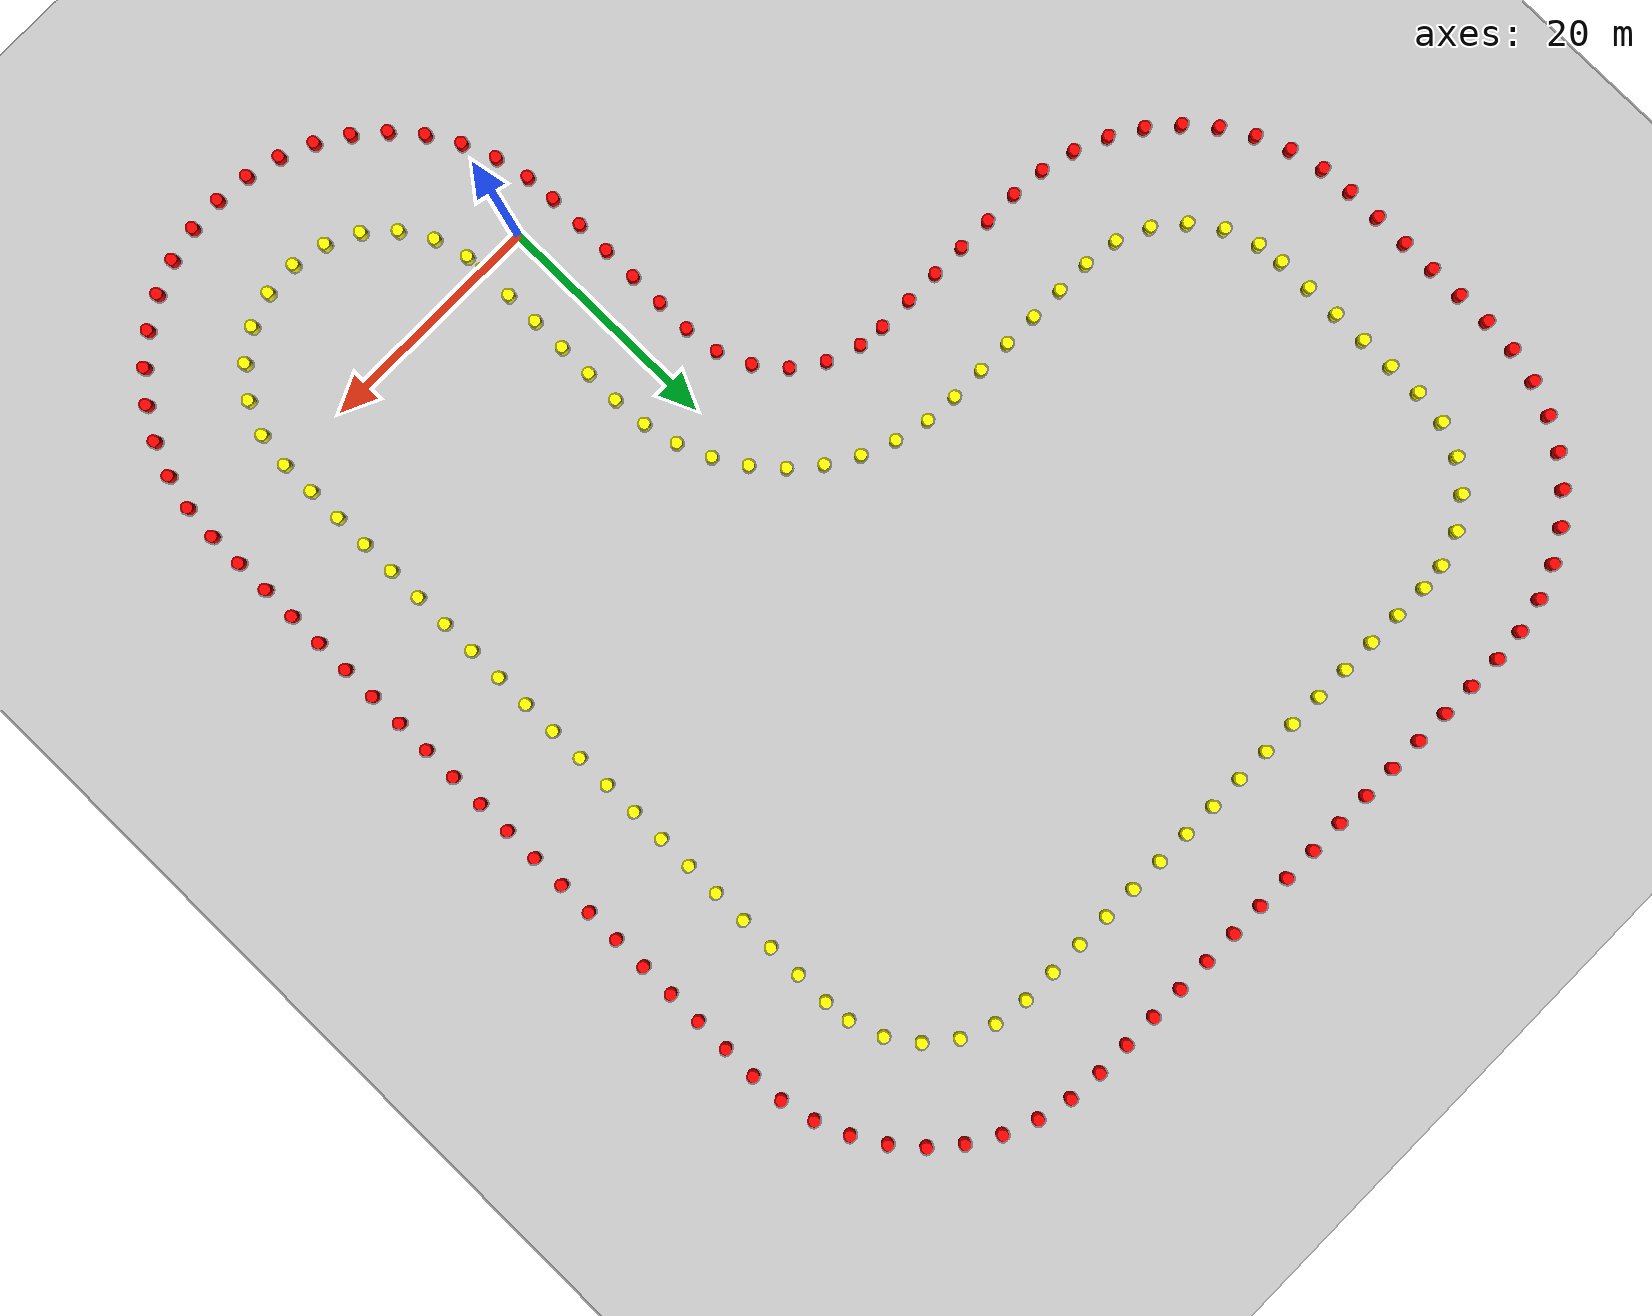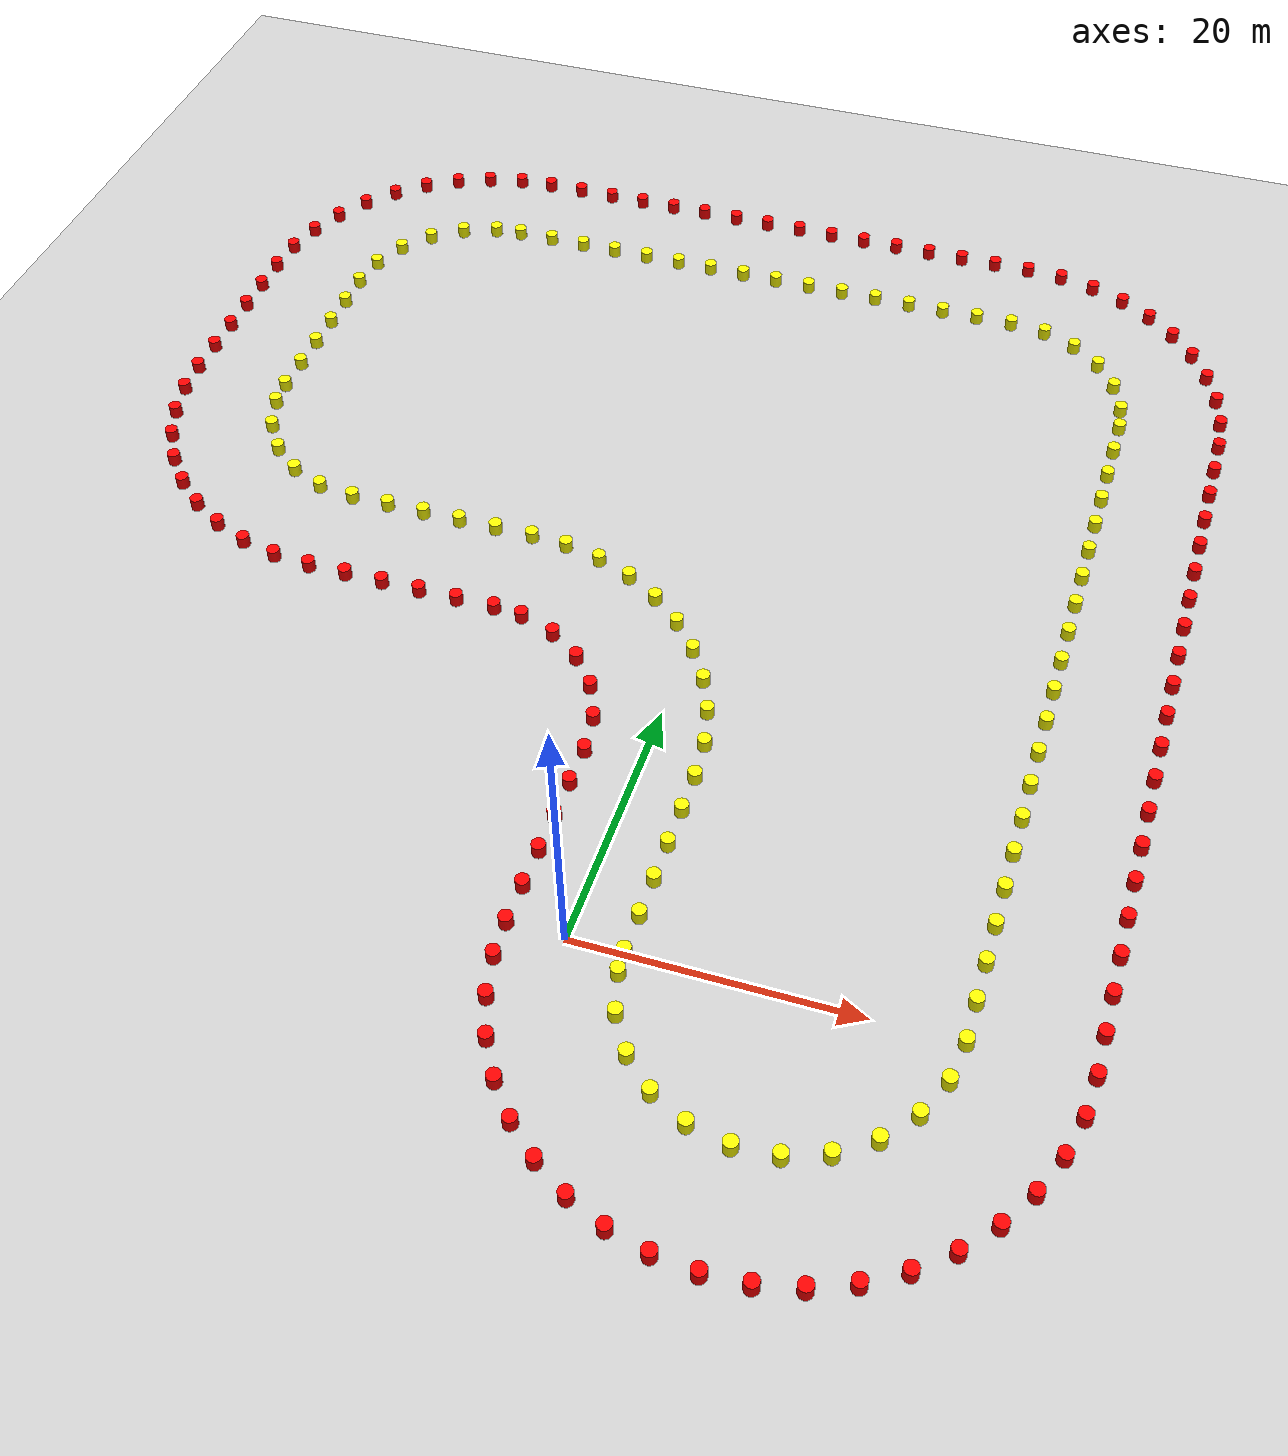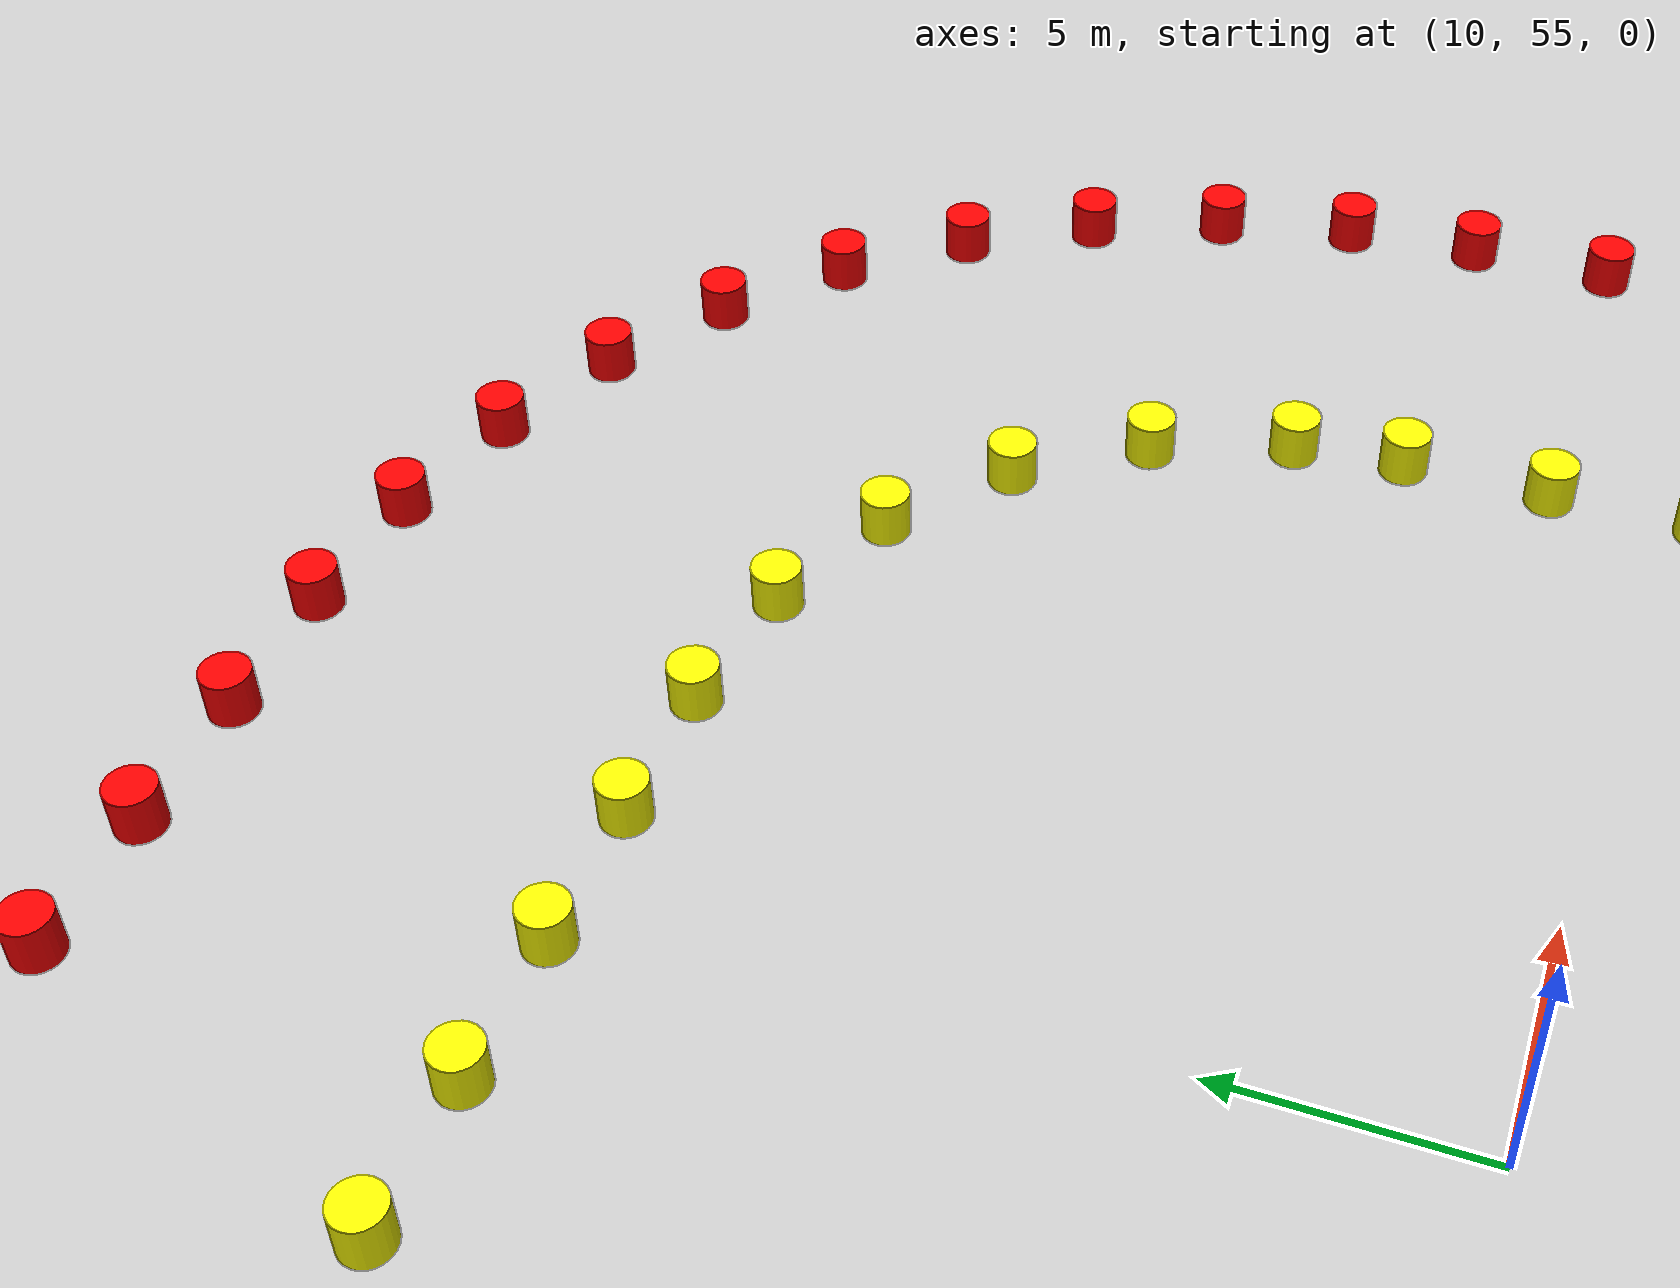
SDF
<sdf version='1.9'>
  <world name='empty'>
    <physics name='1ms' type='ignored'>
      <max_step_size>0.02</max_step_size>
      <real_time_factor>1</real_time_factor>
      <real_time_update_rate>100</real_time_update_rate>
    </physics>
    <plugin name='gz::sim::systems::Physics' filename='ignition-gazebo-physics-system'/>
    <plugin name='gz::sim::systems::UserCommands' filename='ignition-gazebo-user-commands-system'/>
    <plugin name='gz::sim::systems::SceneBroadcaster' filename='ignition-gazebo-scene-broadcaster-system'/>
    <plugin name='gz::sim::systems::Contact' filename='ignition-gazebo-contact-system'/>
    <gravity>0 0 -9.8</gravity>
    <magnetic_field>6e-06 2.3e-05 -4.2e-05</magnetic_field>
    <atmosphere type='adiabatic'/>
    <scene>
      <ambient>1 1 1 1</ambient>
      <background>1 1 1 1</background>
      <shadows>false</shadows>
    </scene>
    <model name='ground_plane'>
      <static>true</static>
      <link name='link'>
        <collision name='collision'>
          <geometry>
            <plane>
              <normal>0 0 1</normal>
              <size>1000 1000</size>
            </plane>
          </geometry>
          <surface>
            <friction>
              <ode/>
            </friction>
            <bounce/>
            <contact/>
          </surface>
        </collision>
        <visual name='visual'>
          <geometry>
            <plane>
              <normal>0 0 1</normal>
              <size>1000 1000</size>
            </plane>
          </geometry>
          <material>
            <ambient>0.8 0.8 0.8 1</ambient>
            <diffuse>0.8 0.8 0.8 1</diffuse>
            <specular>0.8 0.8 0.8 1</specular>
          </material>
        </visual>
        <pose>0 0 0 0 -0 0</pose>
        <inertial>
          <pose>0 0 0 0 -0 0</pose>
          <mass>1</mass>
          <inertia>
            <ixx>1</ixx>
            <ixy>0</ixy>
            <ixz>0</ixz>
            <iyy>1</iyy>
            <iyz>0</iyz>
            <izz>1</izz>
          </inertia>
        </inertial>
        <enable_wind>false</enable_wind>
      </link>
      <pose>0 0 0 0 -0 0</pose>
      <self_collide>false</self_collide>
    </model>
    <light name='sun' type='directional'>
      <pose>0 0 10 0 -0 0</pose>
      <cast_shadows>true</cast_shadows>
      <intensity>1</intensity>
      <direction>-0.5 0.1 -0.9</direction>
      <diffuse>0.8 0.8 0.8 1</diffuse>
      <specular>0.2 0.2 0.2 1</specular>
      <attenuation>
        <range>1000</range>
        <linear>0.01</linear>
        <constant>0.90000000000000002</constant>
        <quadratic>0.001</quadratic>
      </attenuation>
      <spot>
        <inner_angle>0</inner_angle>
        <outer_angle>0</outer_angle>
        <falloff>0</falloff>
      </spot>
    </light>

    <model name='red_cone_0'>
       <pose>-4.0 0.0 0.5 0 -0 0</pose>
       <link name='cylinder_link'>
         <inertial>
           <inertia>
             <ixx>0.14580000000000001</ixx>
             <ixy>0</ixy>
             <ixz>0</ixz>
             <iyy>0.14580000000000001</iyy>
             <iyz>0</iyz>
             <izz>0.125</izz>
           </inertia>
           <mass>1</mass>
           <pose>0 0 0 0 -0 0</pose>
         </inertial>
         <collision name='cylinder_collision'>
           <geometry>
             <cylinder>
               <radius>0.5</radius>
               <length>1</length>
             </cylinder>
           </geometry>
           <surface>
             <friction>
               <ode/>
             </friction>
             <bounce/>
             <contact/>
           </surface>
         </collision>
         <visual name='cylinder_visual'>
           <geometry>
             <cylinder>
               <radius>0.5</radius>
               <length>1</length>
             </cylinder>
           </geometry>
           <material>
             <ambient>1 0 0 1</ambient>
             <diffuse>1 0 0 1</diffuse>
             <specular>1 1 1 1</specular>
           </material>
         </visual>
         <pose>0 0 0 0 -0 0</pose>
         <enable_wind>false</enable_wind>
       </link>
       <static>false</static>
       <self_collide>false</self_collide>
     </model>

    <model name='red_cone_1'>
       <pose>-4.0 3.0 0.5 0 -0 0</pose>
       <link name='cylinder_link'>
         <inertial>
           <inertia>
             <ixx>0.14580000000000001</ixx>
             <ixy>0</ixy>
             <ixz>0</ixz>
             <iyy>0.14580000000000001</iyy>
             <iyz>0</iyz>
             <izz>0.125</izz>
           </inertia>
           <mass>1</mass>
           <pose>0 0 0 0 -0 0</pose>
         </inertial>
         <collision name='cylinder_collision'>
           <geometry>
             <cylinder>
               <radius>0.5</radius>
               <length>1</length>
             </cylinder>
           </geometry>
           <surface>
             <friction>
               <ode/>
             </friction>
             <bounce/>
             <contact/>
           </surface>
         </collision>
         <visual name='cylinder_visual'>
           <geometry>
             <cylinder>
               <radius>0.5</radius>
               <length>1</length>
             </cylinder>
           </geometry>
           <material>
             <ambient>1 0 0 1</ambient>
             <diffuse>1 0 0 1</diffuse>
             <specular>1 1 1 1</specular>
           </material>
         </visual>
         <pose>0 0 0 0 -0 0</pose>
         <enable_wind>false</enable_wind>
       </link>
       <static>false</static>
       <self_collide>false</self_collide>
     </model>

    <model name='red_cone_2'>
       <pose>-4.0 6.0 0.5 0 -0 0</pose>
       <link name='cylinder_link'>
         <inertial>
           <inertia>
             <ixx>0.14580000000000001</ixx>
             <ixy>0</ixy>
             <ixz>0</ixz>
             <iyy>0.14580000000000001</iyy>
             <iyz>0</iyz>
             <izz>0.125</izz>
           </inertia>
           <mass>1</mass>
           <pose>0 0 0 0 -0 0</pose>
         </inertial>
         <collision name='cylinder_collision'>
           <geometry>
             <cylinder>
               <radius>0.5</radius>
               <length>1</length>
             </cylinder>
           </geometry>
           <surface>
             <friction>
               <ode/>
             </friction>
             <bounce/>
             <contact/>
           </surface>
         </collision>
         <visual name='cylinder_visual'>
           <geometry>
             <cylinder>
               <radius>0.5</radius>
               <length>1</length>
             </cylinder>
           </geometry>
           <material>
             <ambient>1 0 0 1</ambient>
             <diffuse>1 0 0 1</diffuse>
             <specular>1 1 1 1</specular>
           </material>
         </visual>
         <pose>0 0 0 0 -0 0</pose>
         <enable_wind>false</enable_wind>
       </link>
       <static>false</static>
       <self_collide>false</self_collide>
     </model>

    <model name='red_cone_3'>
       <pose>-4.0 9.0 0.5 0 -0 0</pose>
       <link name='cylinder_link'>
         <inertial>
           <inertia>
             <ixx>0.14580000000000001</ixx>
             <ixy>0</ixy>
             <ixz>0</ixz>
             <iyy>0.14580000000000001</iyy>
             <iyz>0</iyz>
             <izz>0.125</izz>
           </inertia>
           <mass>1</mass>
           <pose>0 0 0 0 -0 0</pose>
         </inertial>
         <collision name='cylinder_collision'>
           <geometry>
             <cylinder>
               <radius>0.5</radius>
               <length>1</length>
             </cylinder>
           </geometry>
           <surface>
             <friction>
               <ode/>
             </friction>
             <bounce/>
             <contact/>
           </surface>
         </collision>
         <visual name='cylinder_visual'>
           <geometry>
             <cylinder>
               <radius>0.5</radius>
               <length>1</length>
             </cylinder>
           </geometry>
           <material>
             <ambient>1 0 0 1</ambient>
             <diffuse>1 0 0 1</diffuse>
             <specular>1 1 1 1</specular>
           </material>
         </visual>
         <pose>0 0 0 0 -0 0</pose>
         <enable_wind>false</enable_wind>
       </link>
       <static>false</static>
       <self_collide>false</self_collide>
     </model>

    <model name='red_cone_4'>
       <pose>-4.0 12.0 0.5 0 -0 0</pose>
       <link name='cylinder_link'>
         <inertial>
           <inertia>
             <ixx>0.14580000000000001</ixx>
             <ixy>0</ixy>
             <ixz>0</ixz>
             <iyy>0.14580000000000001</iyy>
             <iyz>0</iyz>
             <izz>0.125</izz>
           </inertia>
           <mass>1</mass>
           <pose>0 0 0 0 -0 0</pose>
         </inertial>
         <collision name='cylinder_collision'>
           <geometry>
             <cylinder>
               <radius>0.5</radius>
               <length>1</length>
             </cylinder>
           </geometry>
           <surface>
             <friction>
               <ode/>
             </friction>
             <bounce/>
             <contact/>
           </surface>
         </collision>
         <visual name='cylinder_visual'>
           <geometry>
             <cylinder>
               <radius>0.5</radius>
               <length>1</length>
             </cylinder>
           </geometry>
           <material>
             <ambient>1 0 0 1</ambient>
             <diffuse>1 0 0 1</diffuse>
             <specular>1 1 1 1</specular>
           </material>
         </visual>
         <pose>0 0 0 0 -0 0</pose>
         <enable_wind>false</enable_wind>
       </link>
       <static>false</static>
       <self_collide>false</self_collide>
     </model>

    <model name='red_cone_5'>
       <pose>-4.0 15.0 0.5 0 -0 0</pose>
       <link name='cylinder_link'>
         <inertial>
           <inertia>
             <ixx>0.14580000000000001</ixx>
             <ixy>0</ixy>
             <ixz>0</ixz>
             <iyy>0.14580000000000001</iyy>
             <iyz>0</iyz>
             <izz>0.125</izz>
           </inertia>
           <mass>1</mass>
           <pose>0 0 0 0 -0 0</pose>
         </inertial>
         <collision name='cylinder_collision'>
           <geometry>
             <cylinder>
               <radius>0.5</radius>
               <length>1</length>
             </cylinder>
           </geometry>
           <surface>
             <friction>
               <ode/>
             </friction>
             <bounce/>
             <contact/>
           </surface>
         </collision>
         <visual name='cylinder_visual'>
           <geometry>
             <cylinder>
               <radius>0.5</radius>
               <length>1</length>
             </cylinder>
           </geometry>
           <material>
             <ambient>1 0 0 1</ambient>
             <diffuse>1 0 0 1</diffuse>
             <specular>1 1 1 1</specular>
           </material>
         </visual>
         <pose>0 0 0 0 -0 0</pose>
         <enable_wind>false</enable_wind>
       </link>
       <static>false</static>
       <self_collide>false</self_collide>
     </model>

    <model name='red_cone_6'>
       <pose>-4.0 15.0 0.5 0 -0 0</pose>
       <link name='cylinder_link'>
         <inertial>
           <inertia>
             <ixx>0.14580000000000001</ixx>
             <ixy>0</ixy>
             <ixz>0</ixz>
             <iyy>0.14580000000000001</iyy>
             <iyz>0</iyz>
             <izz>0.125</izz>
           </inertia>
           <mass>1</mass>
           <pose>0 0 0 0 -0 0</pose>
         </inertial>
         <collision name='cylinder_collision'>
           <geometry>
             <cylinder>
               <radius>0.5</radius>
               <length>1</length>
             </cylinder>
           </geometry>
           <surface>
             <friction>
               <ode/>
             </friction>
             <bounce/>
             <contact/>
           </surface>
         </collision>
         <visual name='cylinder_visual'>
           <geometry>
             <cylinder>
               <radius>0.5</radius>
               <length>1</length>
             </cylinder>
           </geometry>
           <material>
             <ambient>1 0 0 1</ambient>
             <diffuse>1 0 0 1</diffuse>
             <specular>1 1 1 1</specular>
           </material>
         </visual>
         <pose>0 0 0 0 -0 0</pose>
         <enable_wind>false</enable_wind>
       </link>
       <static>false</static>
       <self_collide>false</self_collide>
     </model>

    <model name='red_cone_7'>
       <pose>-4.406561500122885 17.962947982891585 0.5 0 -0 0</pose>
       <link name='cylinder_link'>
         <inertial>
           <inertia>
             <ixx>0.14580000000000001</ixx>
             <ixy>0</ixy>
             <ixz>0</ixz>
             <iyy>0.14580000000000001</iyy>
             <iyz>0</iyz>
             <izz>0.125</izz>
           </inertia>
           <mass>1</mass>
           <pose>0 0 0 0 -0 0</pose>
         </inertial>
         <collision name='cylinder_collision'>
           <geometry>
             <cylinder>
               <radius>0.5</radius>
               <length>1</length>
             </cylinder>
           </geometry>
           <surface>
             <friction>
               <ode/>
             </friction>
             <bounce/>
             <contact/>
           </surface>
         </collision>
         <visual name='cylinder_visual'>
           <geometry>
             <cylinder>
               <radius>0.5</radius>
               <length>1</length>
             </cylinder>
           </geometry>
           <material>
             <ambient>1 0 0 1</ambient>
             <diffuse>1 0 0 1</diffuse>
             <specular>1 1 1 1</specular>
           </material>
         </visual>
         <pose>0 0 0 0 -0 0</pose>
         <enable_wind>false</enable_wind>
       </link>
       <static>false</static>
       <self_collide>false</self_collide>
     </model>

    <model name='red_cone_8'>
       <pose>-5.5961928635129645 20.7068740427449 0.5 0 -0 0</pose>
       <link name='cylinder_link'>
         <inertial>
           <inertia>
             <ixx>0.14580000000000001</ixx>
             <ixy>0</ixy>
             <ixz>0</ixz>
             <iyy>0.14580000000000001</iyy>
             <iyz>0</iyz>
             <izz>0.125</izz>
           </inertia>
           <mass>1</mass>
           <pose>0 0 0 0 -0 0</pose>
         </inertial>
         <collision name='cylinder_collision'>
           <geometry>
             <cylinder>
               <radius>0.5</radius>
               <length>1</length>
             </cylinder>
           </geometry>
           <surface>
             <friction>
               <ode/>
             </friction>
             <bounce/>
             <contact/>
           </surface>
         </collision>
         <visual name='cylinder_visual'>
           <geometry>
             <cylinder>
               <radius>0.5</radius>
               <length>1</length>
             </cylinder>
           </geometry>
           <material>
             <ambient>1 0 0 1</ambient>
             <diffuse>1 0 0 1</diffuse>
             <specular>1 1 1 1</specular>
           </material>
         </visual>
         <pose>0 0 0 0 -0 0</pose>
         <enable_wind>false</enable_wind>
       </link>
       <static>false</static>
       <self_collide>false</self_collide>
     </model>

    <model name='red_cone_9'>
       <pose>-7.480956215316949 23.02894641681081 0.5 0 -0 0</pose>
       <link name='cylinder_link'>
         <inertial>
           <inertia>
             <ixx>0.14580000000000001</ixx>
             <ixy>0</ixy>
             <ixz>0</ixz>
             <iyy>0.14580000000000001</iyy>
             <iyz>0</iyz>
             <izz>0.125</izz>
           </inertia>
           <mass>1</mass>
           <pose>0 0 0 0 -0 0</pose>
         </inertial>
         <collision name='cylinder_collision'>
           <geometry>
             <cylinder>
               <radius>0.5</radius>
               <length>1</length>
             </cylinder>
           </geometry>
           <surface>
             <friction>
               <ode/>
             </friction>
             <bounce/>
             <contact/>
           </surface>
         </collision>
         <visual name='cylinder_visual'>
           <geometry>
             <cylinder>
               <radius>0.5</radius>
               <length>1</length>
             </cylinder>
           </geometry>
           <material>
             <ambient>1 0 0 1</ambient>
             <diffuse>1 0 0 1</diffuse>
             <specular>1 1 1 1</specular>
           </material>
         </visual>
         <pose>0 0 0 0 -0 0</pose>
         <enable_wind>false</enable_wind>
       </link>
       <static>false</static>
       <self_collide>false</self_collide>
     </model>

    <model name='red_cone_10'>
       <pose>-9.921529334501002 24.757516881854016 0.5 0 -0 0</pose>
       <link name='cylinder_link'>
         <inertial>
           <inertia>
             <ixx>0.14580000000000001</ixx>
             <ixy>0</ixy>
             <ixz>0</ixz>
             <iyy>0.14580000000000001</iyy>
             <iyz>0</iyz>
             <izz>0.125</izz>
           </inertia>
           <mass>1</mass>
           <pose>0 0 0 0 -0 0</pose>
         </inertial>
         <collision name='cylinder_collision'>
           <geometry>
             <cylinder>
               <radius>0.5</radius>
               <length>1</length>
             </cylinder>
           </geometry>
           <surface>
             <friction>
               <ode/>
             </friction>
             <bounce/>
             <contact/>
           </surface>
         </collision>
         <visual name='cylinder_visual'>
           <geometry>
             <cylinder>
               <radius>0.5</radius>
               <length>1</length>
             </cylinder>
           </geometry>
           <material>
             <ambient>1 0 0 1</ambient>
             <diffuse>1 0 0 1</diffuse>
             <specular>1 1 1 1</specular>
           </material>
         </visual>
         <pose>0 0 0 0 -0 0</pose>
         <enable_wind>false</enable_wind>
       </link>
       <static>false</static>
       <self_collide>false</self_collide>
     </model>

    <model name='red_cone_11'>
       <pose>-12.737504390429667 25.7648090376316 0.5 0 -0 0</pose>
       <link name='cylinder_link'>
         <inertial>
           <inertia>
             <ixx>0.14580000000000001</ixx>
             <ixy>0</ixy>
             <ixz>0</ixz>
             <iyy>0.14580000000000001</iyy>
             <iyz>0</iyz>
             <izz>0.125</izz>
           </inertia>
           <mass>1</mass>
           <pose>0 0 0 0 -0 0</pose>
         </inertial>
         <collision name='cylinder_collision'>
           <geometry>
             <cylinder>
               <radius>0.5</radius>
               <length>1</length>
             </cylinder>
           </geometry>
           <surface>
             <friction>
               <ode/>
             </friction>
             <bounce/>
             <contact/>
           </surface>
         </collision>
         <visual name='cylinder_visual'>
           <geometry>
             <cylinder>
               <radius>0.5</radius>
               <length>1</length>
             </cylinder>
           </geometry>
           <material>
             <ambient>1 0 0 1</ambient>
             <diffuse>1 0 0 1</diffuse>
             <specular>1 1 1 1</specular>
           </material>
         </visual>
         <pose>0 0 0 0 -0 0</pose>
         <enable_wind>false</enable_wind>
       </link>
       <static>false</static>
       <self_collide>false</self_collide>
     </model>

    <model name='red_cone_12'>
       <pose>-15.0 26.0 0.5 0 -0 0</pose>
       <link name='cylinder_link'>
         <inertial>
           <inertia>
             <ixx>0.14580000000000001</ixx>
             <ixy>0</ixy>
             <ixz>0</ixz>
             <iyy>0.14580000000000001</iyy>
             <iyz>0</iyz>
             <izz>0.125</izz>
           </inertia>
           <mass>1</mass>
           <pose>0 0 0 0 -0 0</pose>
         </inertial>
         <collision name='cylinder_collision'>
           <geometry>
             <cylinder>
               <radius>0.5</radius>
               <length>1</length>
             </cylinder>
           </geometry>
           <surface>
             <friction>
               <ode/>
             </friction>
             <bounce/>
             <contact/>
           </surface>
         </collision>
         <visual name='cylinder_visual'>
           <geometry>
             <cylinder>
               <radius>0.5</radius>
               <length>1</length>
             </cylinder>
           </geometry>
           <material>
             <ambient>1 0 0 1</ambient>
             <diffuse>1 0 0 1</diffuse>
             <specular>1 1 1 1</specular>
           </material>
         </visual>
         <pose>0 0 0 0 -0 0</pose>
         <enable_wind>false</enable_wind>
       </link>
       <static>false</static>
       <self_collide>false</self_collide>
     </model>

    <model name='red_cone_13'>
       <pose>-18.0 26.0 0.5 0 -0 0</pose>
       <link name='cylinder_link'>
         <inertial>
           <inertia>
             <ixx>0.14580000000000001</ixx>
             <ixy>0</ixy>
             <ixz>0</ixz>
             <iyy>0.14580000000000001</iyy>
             <iyz>0</iyz>
             <izz>0.125</izz>
           </inertia>
           <mass>1</mass>
           <pose>0 0 0 0 -0 0</pose>
         </inertial>
         <collision name='cylinder_collision'>
           <geometry>
             <cylinder>
               <radius>0.5</radius>
               <length>1</length>
             </cylinder>
           </geometry>
           <surface>
             <friction>
               <ode/>
             </friction>
             <bounce/>
             <contact/>
           </surface>
         </collision>
         <visual name='cylinder_visual'>
           <geometry>
             <cylinder>
               <radius>0.5</radius>
               <length>1</length>
             </cylinder>
           </geometry>
           <material>
             <ambient>1 0 0 1</ambient>
             <diffuse>1 0 0 1</diffuse>
             <specular>1 1 1 1</specular>
           </material>
         </visual>
         <pose>0 0 0 0 -0 0</pose>
         <enable_wind>false</enable_wind>
       </link>
       <static>false</static>
       <self_collide>false</self_collide>
     </model>

    <model name='red_cone_14'>
       <pose>-21.0 26.0 0.5 0 -0 0</pose>
       <link name='cylinder_link'>
         <inertial>
           <inertia>
             <ixx>0.14580000000000001</ixx>
             <ixy>0</ixy>
             <ixz>0</ixz>
             <iyy>0.14580000000000001</iyy>
             <iyz>0</iyz>
             <izz>0.125</izz>
           </inertia>
           <mass>1</mass>
           <pose>0 0 0 0 -0 0</pose>
         </inertial>
         <collision name='cylinder_collision'>
           <geometry>
             <cylinder>
               <radius>0.5</radius>
               <length>1</length>
             </cylinder>
           </geometry>
           <surface>
             <friction>
               <ode/>
             </friction>
             <bounce/>
             <contact/>
           </surface>
         </collision>
         <visual name='cylinder_visual'>
           <geometry>
             <cylinder>
               <radius>0.5</radius>
               <length>1</length>
             </cylinder>
           </geometry>
           <material>
             <ambient>1 0 0 1</ambient>
             <diffuse>1 0 0 1</diffuse>
             <specular>1 1 1 1</specular>
           </material>
         </visual>
         <pose>0 0 0 0 -0 0</pose>
         <enable_wind>false</enable_wind>
       </link>
       <static>false</static>
       <self_collide>false</self_collide>
     </model>

    <model name='red_cone_15'>
       <pose>-24.0 26.0 0.5 0 -0 0</pose>
       <link name='cylinder_link'>
         <inertial>
           <inertia>
             <ixx>0.14580000000000001</ixx>
             <ixy>0</ixy>
             <ixz>0</ixz>
             <iyy>0.14580000000000001</iyy>
             <iyz>0</iyz>
             <izz>0.125</izz>
           </inertia>
           <mass>1</mass>
           <pose>0 0 0 0 -0 0</pose>
         </inertial>
         <collision name='cylinder_collision'>
           <geometry>
             <cylinder>
               <radius>0.5</radius>
               <length>1</length>
             </cylinder>
           </geometry>
           <surface>
             <friction>
               <ode/>
             </friction>
             <bounce/>
             <contact/>
           </surface>
         </collision>
         <visual name='cylinder_visual'>
           <geometry>
             <cylinder>
               <radius>0.5</radius>
               <length>1</length>
             </cylinder>
           </geometry>
           <material>
             <ambient>1 0 0 1</ambient>
             <diffuse>1 0 0 1</diffuse>
             <specular>1 1 1 1</specular>
           </material>
         </visual>
         <pose>0 0 0 0 -0 0</pose>
         <enable_wind>false</enable_wind>
       </link>
       <static>false</static>
       <self_collide>false</self_collide>
     </model>

    <model name='red_cone_16'>
       <pose>-27.0 26.0 0.5 0 -0 0</pose>
       <link name='cylinder_link'>
         <inertial>
           <inertia>
             <ixx>0.14580000000000001</ixx>
             <ixy>0</ixy>
             <ixz>0</ixz>
             <iyy>0.14580000000000001</iyy>
             <iyz>0</iyz>
             <izz>0.125</izz>
           </inertia>
           <mass>1</mass>
           <pose>0 0 0 0 -0 0</pose>
         </inertial>
         <collision name='cylinder_collision'>
           <geometry>
             <cylinder>
               <radius>0.5</radius>
               <length>1</length>
             </cylinder>
           </geometry>
           <surface>
             <friction>
               <ode/>
             </friction>
             <bounce/>
             <contact/>
           </surface>
         </collision>
         <visual name='cylinder_visual'>
           <geometry>
             <cylinder>
               <radius>0.5</radius>
               <length>1</length>
             </cylinder>
           </geometry>
           <material>
             <ambient>1 0 0 1</ambient>
             <diffuse>1 0 0 1</diffuse>
             <specular>1 1 1 1</specular>
           </material>
         </visual>
         <pose>0 0 0 0 -0 0</pose>
         <enable_wind>false</enable_wind>
       </link>
       <static>false</static>
       <self_collide>false</self_collide>
     </model>

    <model name='red_cone_17'>
       <pose>-30.0 26.0 0.5 0 -0 0</pose>
       <link name='cylinder_link'>
         <inertial>
           <inertia>
             <ixx>0.14580000000000001</ixx>
             <ixy>0</ixy>
             <ixz>0</ixz>
             <iyy>0.14580000000000001</iyy>
             <iyz>0</iyz>
             <izz>0.125</izz>
           </inertia>
           <mass>1</mass>
           <pose>0 0 0 0 -0 0</pose>
         </inertial>
         <collision name='cylinder_collision'>
           <geometry>
             <cylinder>
               <radius>0.5</radius>
               <length>1</length>
             </cylinder>
           </geometry>
           <surface>
             <friction>
               <ode/>
             </friction>
             <bounce/>
             <contact/>
           </surface>
         </collision>
         <visual name='cylinder_visual'>
           <geometry>
             <cylinder>
               <radius>0.5</radius>
               <length>1</length>
             </cylinder>
           </geometry>
           <material>
             <ambient>1 0 0 1</ambient>
             <diffuse>1 0 0 1</diffuse>
             <specular>1 1 1 1</specular>
           </material>
         </visual>
         <pose>0 0 0 0 -0 0</pose>
         <enable_wind>false</enable_wind>
       </link>
       <static>false</static>
       <self_collide>false</self_collide>
     </model>

    <model name='red_cone_18'>
       <pose>-29.999999999999996 26.0 0.5 0 -0 0</pose>
       <link name='cylinder_link'>
         <inertial>
           <inertia>
             <ixx>0.14580000000000001</ixx>
             <ixy>0</ixy>
             <ixz>0</ixz>
             <iyy>0.14580000000000001</iyy>
             <iyz>0</iyz>
             <izz>0.125</izz>
           </inertia>
           <mass>1</mass>
           <pose>0 0 0 0 -0 0</pose>
         </inertial>
         <collision name='cylinder_collision'>
           <geometry>
             <cylinder>
               <radius>0.5</radius>
               <length>1</length>
             </cylinder>
           </geometry>
           <surface>
             <friction>
               <ode/>
             </friction>
             <bounce/>
             <contact/>
           </surface>
         </collision>
         <visual name='cylinder_visual'>
           <geometry>
             <cylinder>
               <radius>0.5</radius>
               <length>1</length>
             </cylinder>
           </geometry>
           <material>
             <ambient>1 0 0 1</ambient>
             <diffuse>1 0 0 1</diffuse>
             <specular>1 1 1 1</specular>
           </material>
         </visual>
         <pose>0 0 0 0 -0 0</pose>
         <enable_wind>false</enable_wind>
       </link>
       <static>false</static>
       <self_collide>false</self_collide>
     </model>

    <model name='red_cone_19'>
       <pose>-32.98755015537325 26.23635045975519 0.5 0 -0 0</pose>
       <link name='cylinder_link'>
         <inertial>
           <inertia>
             <ixx>0.14580000000000001</ixx>
             <ixy>0</ixy>
             <ixz>0</ixz>
             <iyy>0.14580000000000001</iyy>
             <iyz>0</iyz>
             <izz>0.125</izz>
           </inertia>
           <mass>1</mass>
           <pose>0 0 0 0 -0 0</pose>
         </inertial>
         <collision name='cylinder_collision'>
           <geometry>
             <cylinder>
               <radius>0.5</radius>
               <length>1</length>
             </cylinder>
           </geometry>
           <surface>
             <friction>
               <ode/>
             </friction>
             <bounce/>
             <contact/>
           </surface>
         </collision>
         <visual name='cylinder_visual'>
           <geometry>
             <cylinder>
               <radius>0.5</radius>
               <length>1</length>
             </cylinder>
           </geometry>
           <material>
             <ambient>1 0 0 1</ambient>
             <diffuse>1 0 0 1</diffuse>
             <specular>1 1 1 1</specular>
           </material>
         </visual>
         <pose>0 0 0 0 -0 0</pose>
         <enable_wind>false</enable_wind>
       </link>
       <static>false</static>
       <self_collide>false</self_collide>
     </model>

    <model name='red_cone_20'>
       <pose>-35.90077306308712 26.939521676933765 0.5 0 -0 0</pose>
       <link name='cylinder_link'>
         <inertial>
           <inertia>
             <ixx>0.14580000000000001</ixx>
             <ixy>0</ixy>
             <ixz>0</ixz>
             <iyy>0.14580000000000001</iyy>
             <iyz>0</iyz>
             <izz>0.125</izz>
           </inertia>
           <mass>1</mass>
           <pose>0 0 0 0 -0 0</pose>
         </inertial>
         <collision name='cylinder_collision'>
           <geometry>
             <cylinder>
               <radius>0.5</radius>
               <length>1</length>
             </cylinder>
           </geometry>
           <surface>
             <friction>
               <ode/>
             </friction>
             <bounce/>
             <contact/>
           </surface>
         </collision>
         <visual name='cylinder_visual'>
           <geometry>
             <cylinder>
               <radius>0.5</radius>
               <length>1</length>
             </cylinder>
           </geometry>
           <material>
             <ambient>1 0 0 1</ambient>
             <diffuse>1 0 0 1</diffuse>
             <specular>1 1 1 1</specular>
           </material>
         </visual>
         <pose>0 0 0 0 -0 0</pose>
         <enable_wind>false</enable_wind>
       </link>
       <static>false</static>
       <self_collide>false</self_collide>
     </model>

    <model name='red_cone_21'>
       <pose>-38.66719066276187 28.092019457802376 0.5 0 -0 0</pose>
       <link name='cylinder_link'>
         <inertial>
           <inertia>
             <ixx>0.14580000000000001</ixx>
             <ixy>0</ixy>
             <ixz>0</ixz>
             <iyy>0.14580000000000001</iyy>
             <iyz>0</iyz>
             <izz>0.125</izz>
           </inertia>
           <mass>1</mass>
           <pose>0 0 0 0 -0 0</pose>
         </inertial>
         <collision name='cylinder_collision'>
           <geometry>
             <cylinder>
               <radius>0.5</radius>
               <length>1</length>
             </cylinder>
           </geometry>
           <surface>
             <friction>
               <ode/>
             </friction>
             <bounce/>
             <contact/>
           </surface>
         </collision>
         <visual name='cylinder_visual'>
           <geometry>
             <cylinder>
               <radius>0.5</radius>
               <length>1</length>
             </cylinder>
           </geometry>
           <material>
             <ambient>1 0 0 1</ambient>
             <diffuse>1 0 0 1</diffuse>
             <specular>1 1 1 1</specular>
           </material>
         </visual>
         <pose>0 0 0 0 -0 0</pose>
         <enable_wind>false</enable_wind>
       </link>
       <static>false</static>
       <self_collide>false</self_collide>
     </model>

    <model name='red_cone_22'>
       <pose>-41.21797726265454 29.665170814953118 0.5 0 -0 0</pose>
       <link name='cylinder_link'>
         <inertial>
           <inertia>
             <ixx>0.14580000000000001</ixx>
             <ixy>0</ixy>
             <ixz>0</ixz>
             <iyy>0.14580000000000001</iyy>
             <iyz>0</iyz>
             <izz>0.125</izz>
           </inertia>
           <mass>1</mass>
           <pose>0 0 0 0 -0 0</pose>
         </inertial>
         <collision name='cylinder_collision'>
           <geometry>
             <cylinder>
               <radius>0.5</radius>
               <length>1</length>
             </cylinder>
           </geometry>
           <surface>
             <friction>
               <ode/>
             </friction>
             <bounce/>
             <contact/>
           </surface>
         </collision>
         <visual name='cylinder_visual'>
           <geometry>
             <cylinder>
               <radius>0.5</radius>
               <length>1</length>
             </cylinder>
           </geometry>
           <material>
             <ambient>1 0 0 1</ambient>
             <diffuse>1 0 0 1</diffuse>
             <specular>1 1 1 1</specular>
           </material>
         </visual>
         <pose>0 0 0 0 -0 0</pose>
         <enable_wind>false</enable_wind>
       </link>
       <static>false</static>
       <self_collide>false</self_collide>
     </model>

    <model name='red_cone_23'>
       <pose>-43.489671853752306 31.61983732243577 0.5 0 -0 0</pose>
       <link name='cylinder_link'>
         <inertial>
           <inertia>
             <ixx>0.14580000000000001</ixx>
             <ixy>0</ixy>
             <ixz>0</ixz>
             <iyy>0.14580000000000001</iyy>
             <iyz>0</iyz>
             <izz>0.125</izz>
           </inertia>
           <mass>1</mass>
           <pose>0 0 0 0 -0 0</pose>
         </inertial>
         <collision name='cylinder_collision'>
           <geometry>
             <cylinder>
               <radius>0.5</radius>
               <length>1</length>
             </cylinder>
           </geometry>
           <surface>
             <friction>
               <ode/>
             </friction>
             <bounce/>
             <contact/>
           </surface>
         </collision>
         <visual name='cylinder_visual'>
           <geometry>
             <cylinder>
               <radius>0.5</radius>
               <length>1</length>
             </cylinder>
           </geometry>
           <material>
             <ambient>1 0 0 1</ambient>
             <diffuse>1 0 0 1</diffuse>
             <specular>1 1 1 1</specular>
           </material>
         </visual>
         <pose>0 0 0 0 -0 0</pose>
         <enable_wind>false</enable_wind>
       </link>
       <static>false</static>
       <self_collide>false</self_collide>
     </model>

    <model name='red_cone_24'>
       <pose>-45.425756955946795 33.90738884049121 0.5 0 -0 0</pose>
       <link name='cylinder_link'>
         <inertial>
           <inertia>
             <ixx>0.14580000000000001</ixx>
             <ixy>0</ixy>
             <ixz>0</ixz>
             <iyy>0.14580000000000001</iyy>
             <iyz>0</iyz>
             <izz>0.125</izz>
           </inertia>
           <mass>1</mass>
           <pose>0 0 0 0 -0 0</pose>
         </inertial>
         <collision name='cylinder_collision'>
           <geometry>
             <cylinder>
               <radius>0.5</radius>
               <length>1</length>
             </cylinder>
           </geometry>
           <surface>
             <friction>
               <ode/>
             </friction>
             <bounce/>
             <contact/>
           </surface>
         </collision>
         <visual name='cylinder_visual'>
           <geometry>
             <cylinder>
               <radius>0.5</radius>
               <length>1</length>
             </cylinder>
           </geometry>
           <material>
             <ambient>1 0 0 1</ambient>
             <diffuse>1 0 0 1</diffuse>
             <specular>1 1 1 1</specular>
           </material>
         </visual>
         <pose>0 0 0 0 -0 0</pose>
         <enable_wind>false</enable_wind>
       </link>
       <static>false</static>
       <self_collide>false</self_collide>
     </model>

    <model name='red_cone_25'>
       <pose>-46.97806471618236 36.4709133845925 0.5 0 -0 0</pose>
       <link name='cylinder_link'>
         <inertial>
           <inertia>
             <ixx>0.14580000000000001</ixx>
             <ixy>0</ixy>
             <ixz>0</ixz>
             <iyy>0.14580000000000001</iyy>
             <iyz>0</iyz>
             <izz>0.125</izz>
           </inertia>
           <mass>1</mass>
           <pose>0 0 0 0 -0 0</pose>
         </inertial>
         <collision name='cylinder_collision'>
           <geometry>
             <cylinder>
               <radius>0.5</radius>
               <length>1</length>
             </cylinder>
           </geometry>
           <surface>
             <friction>
               <ode/>
             </friction>
             <bounce/>
             <contact/>
           </surface>
         </collision>
         <visual name='cylinder_visual'>
           <geometry>
             <cylinder>
               <radius>0.5</radius>
               <length>1</length>
             </cylinder>
           </geometry>
           <material>
             <ambient>1 0 0 1</ambient>
             <diffuse>1 0 0 1</diffuse>
             <specular>1 1 1 1</specular>
           </material>
         </visual>
         <pose>0 0 0 0 -0 0</pose>
         <enable_wind>false</enable_wind>
       </link>
       <static>false</static>
       <self_collide>false</self_collide>
     </model>

    <model name='red_cone_26'>
       <pose>-48.10797527626812 39.24663303846677 0.5 0 -0 0</pose>
       <link name='cylinder_link'>
         <inertial>
           <inertia>
             <ixx>0.14580000000000001</ixx>
             <ixy>0</ixy>
             <ixz>0</ixz>
             <iyy>0.14580000000000001</iyy>
             <iyz>0</iyz>
             <izz>0.125</izz>
           </inertia>
           <mass>1</mass>
           <pose>0 0 0 0 -0 0</pose>
         </inertial>
         <collision name='cylinder_collision'>
           <geometry>
             <cylinder>
               <radius>0.5</radius>
               <length>1</length>
             </cylinder>
           </geometry>
           <surface>
             <friction>
               <ode/>
             </friction>
             <bounce/>
             <contact/>
           </surface>
         </collision>
         <visual name='cylinder_visual'>
           <geometry>
             <cylinder>
               <radius>0.5</radius>
               <length>1</length>
             </cylinder>
           </geometry>
           <material>
             <ambient>1 0 0 1</ambient>
             <diffuse>1 0 0 1</diffuse>
             <specular>1 1 1 1</specular>
           </material>
         </visual>
         <pose>0 0 0 0 -0 0</pose>
         <enable_wind>false</enable_wind>
       </link>
       <static>false</static>
       <self_collide>false</self_collide>
     </model>

    <model name='red_cone_27'>
       <pose>-48.78737759616635 42.165490684604066 0.5 0 -0 0</pose>
       <link name='cylinder_link'>
         <inertial>
           <inertia>
             <ixx>0.14580000000000001</ixx>
             <ixy>0</ixy>
             <ixz>0</ixz>
             <iyy>0.14580000000000001</iyy>
             <iyz>0</iyz>
             <izz>0.125</izz>
           </inertia>
           <mass>1</mass>
           <pose>0 0 0 0 -0 0</pose>
         </inertial>
         <collision name='cylinder_collision'>
           <geometry>
             <cylinder>
               <radius>0.5</radius>
               <length>1</length>
             </cylinder>
           </geometry>
           <surface>
             <friction>
               <ode/>
             </friction>
             <bounce/>
             <contact/>
           </surface>
         </collision>
         <visual name='cylinder_visual'>
           <geometry>
             <cylinder>
               <radius>0.5</radius>
               <length>1</length>
             </cylinder>
           </geometry>
           <material>
             <ambient>1 0 0 1</ambient>
             <diffuse>1 0 0 1</diffuse>
             <specular>1 1 1 1</specular>
           </material>
         </visual>
         <pose>0 0 0 0 -0 0</pose>
         <enable_wind>false</enable_wind>
       </link>
       <static>false</static>
       <self_collide>false</self_collide>
     </model>

    <model name='red_cone_28'>
       <pose>-49.0 45.0 0.5 0 -0 0</pose>
       <link name='cylinder_link'>
         <inertial>
           <inertia>
             <ixx>0.14580000000000001</ixx>
             <ixy>0</ixy>
             <ixz>0</ixz>
             <iyy>0.14580000000000001</iyy>
             <iyz>0</iyz>
             <izz>0.125</izz>
           </inertia>
           <mass>1</mass>
           <pose>0 0 0 0 -0 0</pose>
         </inertial>
         <collision name='cylinder_collision'>
           <geometry>
             <cylinder>
               <radius>0.5</radius>
               <length>1</length>
             </cylinder>
           </geometry>
           <surface>
             <friction>
               <ode/>
             </friction>
             <bounce/>
             <contact/>
           </surface>
         </collision>
         <visual name='cylinder_visual'>
           <geometry>
             <cylinder>
               <radius>0.5</radius>
               <length>1</length>
             </cylinder>
           </geometry>
           <material>
             <ambient>1 0 0 1</ambient>
             <diffuse>1 0 0 1</diffuse>
             <specular>1 1 1 1</specular>
           </material>
         </visual>
         <pose>0 0 0 0 -0 0</pose>
         <enable_wind>false</enable_wind>
       </link>
       <static>false</static>
       <self_collide>false</self_collide>
     </model>

    <model name='red_cone_29'>
       <pose>-49.0 48.0 0.5 0 -0 0</pose>
       <link name='cylinder_link'>
         <inertial>
           <inertia>
             <ixx>0.14580000000000001</ixx>
             <ixy>0</ixy>
             <ixz>0</ixz>
             <iyy>0.14580000000000001</iyy>
             <iyz>0</iyz>
             <izz>0.125</izz>
           </inertia>
           <mass>1</mass>
           <pose>0 0 0 0 -0 0</pose>
         </inertial>
         <collision name='cylinder_collision'>
           <geometry>
             <cylinder>
               <radius>0.5</radius>
               <length>1</length>
             </cylinder>
           </geometry>
           <surface>
             <friction>
               <ode/>
             </friction>
             <bounce/>
             <contact/>
           </surface>
         </collision>
         <visual name='cylinder_visual'>
           <geometry>
             <cylinder>
               <radius>0.5</radius>
               <length>1</length>
             </cylinder>
           </geometry>
           <material>
             <ambient>1 0 0 1</ambient>
             <diffuse>1 0 0 1</diffuse>
             <specular>1 1 1 1</specular>
           </material>
         </visual>
         <pose>0 0 0 0 -0 0</pose>
         <enable_wind>false</enable_wind>
       </link>
       <static>false</static>
       <self_collide>false</self_collide>
     </model>

    <model name='red_cone_30'>
       <pose>-49.0 51.0 0.5 0 -0 0</pose>
       <link name='cylinder_link'>
         <inertial>
           <inertia>
             <ixx>0.14580000000000001</ixx>
             <ixy>0</ixy>
             <ixz>0</ixz>
             <iyy>0.14580000000000001</iyy>
             <iyz>0</iyz>
             <izz>0.125</izz>
           </inertia>
           <mass>1</mass>
           <pose>0 0 0 0 -0 0</pose>
         </inertial>
         <collision name='cylinder_collision'>
           <geometry>
             <cylinder>
               <radius>0.5</radius>
               <length>1</length>
             </cylinder>
           </geometry>
           <surface>
             <friction>
               <ode/>
             </friction>
             <bounce/>
             <contact/>
           </surface>
         </collision>
         <visual name='cylinder_visual'>
           <geometry>
             <cylinder>
               <radius>0.5</radius>
               <length>1</length>
             </cylinder>
           </geometry>
           <material>
             <ambient>1 0 0 1</ambient>
             <diffuse>1 0 0 1</diffuse>
             <specular>1 1 1 1</specular>
           </material>
         </visual>
         <pose>0 0 0 0 -0 0</pose>
         <enable_wind>false</enable_wind>
       </link>
       <static>false</static>
       <self_collide>false</self_collide>
     </model>

    <model name='red_cone_31'>
       <pose>-49.0 54.0 0.5 0 -0 0</pose>
       <link name='cylinder_link'>
         <inertial>
           <inertia>
             <ixx>0.14580000000000001</ixx>
             <ixy>0</ixy>
             <ixz>0</ixz>
             <iyy>0.14580000000000001</iyy>
             <iyz>0</iyz>
             <izz>0.125</izz>
           </inertia>
           <mass>1</mass>
           <pose>0 0 0 0 -0 0</pose>
         </inertial>
         <collision name='cylinder_collision'>
           <geometry>
             <cylinder>
               <radius>0.5</radius>
               <length>1</length>
             </cylinder>
           </geometry>
           <surface>
             <friction>
               <ode/>
             </friction>
             <bounce/>
             <contact/>
           </surface>
         </collision>
         <visual name='cylinder_visual'>
           <geometry>
             <cylinder>
               <radius>0.5</radius>
               <length>1</length>
             </cylinder>
           </geometry>
           <material>
             <ambient>1 0 0 1</ambient>
             <diffuse>1 0 0 1</diffuse>
             <specular>1 1 1 1</specular>
           </material>
         </visual>
         <pose>0 0 0 0 -0 0</pose>
         <enable_wind>false</enable_wind>
       </link>
       <static>false</static>
       <self_collide>false</self_collide>
     </model>

    <model name='red_cone_32'>
       <pose>-49.0 57.0 0.5 0 -0 0</pose>
       <link name='cylinder_link'>
         <inertial>
           <inertia>
             <ixx>0.14580000000000001</ixx>
             <ixy>0</ixy>
             <ixz>0</ixz>
             <iyy>0.14580000000000001</iyy>
             <iyz>0</iyz>
             <izz>0.125</izz>
           </inertia>
           <mass>1</mass>
           <pose>0 0 0 0 -0 0</pose>
         </inertial>
         <collision name='cylinder_collision'>
           <geometry>
             <cylinder>
               <radius>0.5</radius>
               <length>1</length>
             </cylinder>
           </geometry>
           <surface>
             <friction>
               <ode/>
             </friction>
             <bounce/>
             <contact/>
           </surface>
         </collision>
         <visual name='cylinder_visual'>
           <geometry>
             <cylinder>
               <radius>0.5</radius>
               <length>1</length>
             </cylinder>
           </geometry>
           <material>
             <ambient>1 0 0 1</ambient>
             <diffuse>1 0 0 1</diffuse>
             <specular>1 1 1 1</specular>
           </material>
         </visual>
         <pose>0 0 0 0 -0 0</pose>
         <enable_wind>false</enable_wind>
       </link>
       <static>false</static>
       <self_collide>false</self_collide>
     </model>

    <model name='red_cone_33'>
       <pose>-49.0 60.0 0.5 0 -0 0</pose>
       <link name='cylinder_link'>
         <inertial>
           <inertia>
             <ixx>0.14580000000000001</ixx>
             <ixy>0</ixy>
             <ixz>0</ixz>
             <iyy>0.14580000000000001</iyy>
             <iyz>0</iyz>
             <izz>0.125</izz>
           </inertia>
           <mass>1</mass>
           <pose>0 0 0 0 -0 0</pose>
         </inertial>
         <collision name='cylinder_collision'>
           <geometry>
             <cylinder>
               <radius>0.5</radius>
               <length>1</length>
             </cylinder>
           </geometry>
           <surface>
             <friction>
               <ode/>
             </friction>
             <bounce/>
             <contact/>
           </surface>
         </collision>
         <visual name='cylinder_visual'>
           <geometry>
             <cylinder>
               <radius>0.5</radius>
               <length>1</length>
             </cylinder>
           </geometry>
           <material>
             <ambient>1 0 0 1</ambient>
             <diffuse>1 0 0 1</diffuse>
             <specular>1 1 1 1</specular>
           </material>
         </visual>
         <pose>0 0 0 0 -0 0</pose>
         <enable_wind>false</enable_wind>
       </link>
       <static>false</static>
       <self_collide>false</self_collide>
     </model>

    <model name='red_cone_34'>
       <pose>-49.0 60.0 0.5 0 -0 0</pose>
       <link name='cylinder_link'>
         <inertial>
           <inertia>
             <ixx>0.14580000000000001</ixx>
             <ixy>0</ixy>
             <ixz>0</ixz>
             <iyy>0.14580000000000001</iyy>
             <iyz>0</iyz>
             <izz>0.125</izz>
           </inertia>
           <mass>1</mass>
           <pose>0 0 0 0 -0 0</pose>
         </inertial>
         <collision name='cylinder_collision'>
           <geometry>
             <cylinder>
               <radius>0.5</radius>
               <length>1</length>
             </cylinder>
           </geometry>
           <surface>
             <friction>
               <ode/>
             </friction>
             <bounce/>
             <contact/>
           </surface>
         </collision>
         <visual name='cylinder_visual'>
           <geometry>
             <cylinder>
               <radius>0.5</radius>
               <length>1</length>
             </cylinder>
           </geometry>
           <material>
             <ambient>1 0 0 1</ambient>
             <diffuse>1 0 0 1</diffuse>
             <specular>1 1 1 1</specular>
           </material>
         </visual>
         <pose>0 0 0 0 -0 0</pose>
         <enable_wind>false</enable_wind>
       </link>
       <static>false</static>
       <self_collide>false</self_collide>
     </model>

    <model name='red_cone_35'>
       <pose>-48.76364954024481 62.987550155373256 0.5 0 -0 0</pose>
       <link name='cylinder_link'>
         <inertial>
           <inertia>
             <ixx>0.14580000000000001</ixx>
             <ixy>0</ixy>
             <ixz>0</ixz>
             <iyy>0.14580000000000001</iyy>
             <iyz>0</iyz>
             <izz>0.125</izz>
           </inertia>
           <mass>1</mass>
           <pose>0 0 0 0 -0 0</pose>
         </inertial>
         <collision name='cylinder_collision'>
           <geometry>
             <cylinder>
               <radius>0.5</radius>
               <length>1</length>
             </cylinder>
           </geometry>
           <surface>
             <friction>
               <ode/>
             </friction>
             <bounce/>
             <contact/>
           </surface>
         </collision>
         <visual name='cylinder_visual'>
           <geometry>
             <cylinder>
               <radius>0.5</radius>
               <length>1</length>
             </cylinder>
           </geometry>
           <material>
             <ambient>1 0 0 1</ambient>
             <diffuse>1 0 0 1</diffuse>
             <specular>1 1 1 1</specular>
           </material>
         </visual>
         <pose>0 0 0 0 -0 0</pose>
         <enable_wind>false</enable_wind>
       </link>
       <static>false</static>
       <self_collide>false</self_collide>
     </model>

    <model name='red_cone_36'>
       <pose>-48.060478323066235 65.90077306308713 0.5 0 -0 0</pose>
       <link name='cylinder_link'>
         <inertial>
           <inertia>
             <ixx>0.14580000000000001</ixx>
             <ixy>0</ixy>
             <ixz>0</ixz>
             <iyy>0.14580000000000001</iyy>
             <iyz>0</iyz>
             <izz>0.125</izz>
           </inertia>
           <mass>1</mass>
           <pose>0 0 0 0 -0 0</pose>
         </inertial>
         <collision name='cylinder_collision'>
           <geometry>
             <cylinder>
               <radius>0.5</radius>
               <length>1</length>
             </cylinder>
           </geometry>
           <surface>
             <friction>
               <ode/>
             </friction>
             <bounce/>
             <contact/>
           </surface>
         </collision>
         <visual name='cylinder_visual'>
           <geometry>
             <cylinder>
               <radius>0.5</radius>
               <length>1</length>
             </cylinder>
           </geometry>
           <material>
             <ambient>1 0 0 1</ambient>
             <diffuse>1 0 0 1</diffuse>
             <specular>1 1 1 1</specular>
           </material>
         </visual>
         <pose>0 0 0 0 -0 0</pose>
         <enable_wind>false</enable_wind>
       </link>
       <static>false</static>
       <self_collide>false</self_collide>
     </model>

    <model name='red_cone_37'>
       <pose>-46.90798054219762 68.66719066276187 0.5 0 -0 0</pose>
       <link name='cylinder_link'>
         <inertial>
           <inertia>
             <ixx>0.14580000000000001</ixx>
             <ixy>0</ixy>
             <ixz>0</ixz>
             <iyy>0.14580000000000001</iyy>
             <iyz>0</iyz>
             <izz>0.125</izz>
           </inertia>
           <mass>1</mass>
           <pose>0 0 0 0 -0 0</pose>
         </inertial>
         <collision name='cylinder_collision'>
           <geometry>
             <cylinder>
               <radius>0.5</radius>
               <length>1</length>
             </cylinder>
           </geometry>
           <surface>
             <friction>
               <ode/>
             </friction>
             <bounce/>
             <contact/>
           </surface>
         </collision>
         <visual name='cylinder_visual'>
           <geometry>
             <cylinder>
               <radius>0.5</radius>
               <length>1</length>
             </cylinder>
           </geometry>
           <material>
             <ambient>1 0 0 1</ambient>
             <diffuse>1 0 0 1</diffuse>
             <specular>1 1 1 1</specular>
           </material>
         </visual>
         <pose>0 0 0 0 -0 0</pose>
         <enable_wind>false</enable_wind>
       </link>
       <static>false</static>
       <self_collide>false</self_collide>
     </model>

    <model name='red_cone_38'>
       <pose>-45.334829185046885 71.21797726265454 0.5 0 -0 0</pose>
       <link name='cylinder_link'>
         <inertial>
           <inertia>
             <ixx>0.14580000000000001</ixx>
             <ixy>0</ixy>
             <ixz>0</ixz>
             <iyy>0.14580000000000001</iyy>
             <iyz>0</iyz>
             <izz>0.125</izz>
           </inertia>
           <mass>1</mass>
           <pose>0 0 0 0 -0 0</pose>
         </inertial>
         <collision name='cylinder_collision'>
           <geometry>
             <cylinder>
               <radius>0.5</radius>
               <length>1</length>
             </cylinder>
           </geometry>
           <surface>
             <friction>
               <ode/>
             </friction>
             <bounce/>
             <contact/>
           </surface>
         </collision>
         <visual name='cylinder_visual'>
           <geometry>
             <cylinder>
               <radius>0.5</radius>
               <length>1</length>
             </cylinder>
           </geometry>
           <material>
             <ambient>1 0 0 1</ambient>
             <diffuse>1 0 0 1</diffuse>
             <specular>1 1 1 1</specular>
           </material>
         </visual>
         <pose>0 0 0 0 -0 0</pose>
         <enable_wind>false</enable_wind>
       </link>
       <static>false</static>
       <self_collide>false</self_collide>
     </model>

    <model name='red_cone_39'>
       <pose>-43.38016267756423 73.4896718537523 0.5 0 -0 0</pose>
       <link name='cylinder_link'>
         <inertial>
           <inertia>
             <ixx>0.14580000000000001</ixx>
             <ixy>0</ixy>
             <ixz>0</ixz>
             <iyy>0.14580000000000001</iyy>
             <iyz>0</iyz>
             <izz>0.125</izz>
           </inertia>
           <mass>1</mass>
           <pose>0 0 0 0 -0 0</pose>
         </inertial>
         <collision name='cylinder_collision'>
           <geometry>
             <cylinder>
               <radius>0.5</radius>
               <length>1</length>
             </cylinder>
           </geometry>
           <surface>
             <friction>
               <ode/>
             </friction>
             <bounce/>
             <contact/>
           </surface>
         </collision>
         <visual name='cylinder_visual'>
           <geometry>
             <cylinder>
               <radius>0.5</radius>
               <length>1</length>
             </cylinder>
           </geometry>
           <material>
             <ambient>1 0 0 1</ambient>
             <diffuse>1 0 0 1</diffuse>
             <specular>1 1 1 1</specular>
           </material>
         </visual>
         <pose>0 0 0 0 -0 0</pose>
         <enable_wind>false</enable_wind>
       </link>
       <static>false</static>
       <self_collide>false</self_collide>
     </model>

    <model name='red_cone_40'>
       <pose>-41.092611159508785 75.42575695594681 0.5 0 -0 0</pose>
       <link name='cylinder_link'>
         <inertial>
           <inertia>
             <ixx>0.14580000000000001</ixx>
             <ixy>0</ixy>
             <ixz>0</ixz>
             <iyy>0.14580000000000001</iyy>
             <iyz>0</iyz>
             <izz>0.125</izz>
           </inertia>
           <mass>1</mass>
           <pose>0 0 0 0 -0 0</pose>
         </inertial>
         <collision name='cylinder_collision'>
           <geometry>
             <cylinder>
               <radius>0.5</radius>
               <length>1</length>
             </cylinder>
           </geometry>
           <surface>
             <friction>
               <ode/>
             </friction>
             <bounce/>
             <contact/>
           </surface>
         </collision>
         <visual name='cylinder_visual'>
           <geometry>
             <cylinder>
               <radius>0.5</radius>
               <length>1</length>
             </cylinder>
           </geometry>
           <material>
             <ambient>1 0 0 1</ambient>
             <diffuse>1 0 0 1</diffuse>
             <specular>1 1 1 1</specular>
           </material>
         </visual>
         <pose>0 0 0 0 -0 0</pose>
         <enable_wind>false</enable_wind>
       </link>
       <static>false</static>
       <self_collide>false</self_collide>
     </model>

    <model name='red_cone_41'>
       <pose>-38.5290866154075 76.97806471618236 0.5 0 -0 0</pose>
       <link name='cylinder_link'>
         <inertial>
           <inertia>
             <ixx>0.14580000000000001</ixx>
             <ixy>0</ixy>
             <ixz>0</ixz>
             <iyy>0.14580000000000001</iyy>
             <iyz>0</iyz>
             <izz>0.125</izz>
           </inertia>
           <mass>1</mass>
           <pose>0 0 0 0 -0 0</pose>
         </inertial>
         <collision name='cylinder_collision'>
           <geometry>
             <cylinder>
               <radius>0.5</radius>
               <length>1</length>
             </cylinder>
           </geometry>
           <surface>
             <friction>
               <ode/>
             </friction>
             <bounce/>
             <contact/>
           </surface>
         </collision>
         <visual name='cylinder_visual'>
           <geometry>
             <cylinder>
               <radius>0.5</radius>
               <length>1</length>
             </cylinder>
           </geometry>
           <material>
             <ambient>1 0 0 1</ambient>
             <diffuse>1 0 0 1</diffuse>
             <specular>1 1 1 1</specular>
           </material>
         </visual>
         <pose>0 0 0 0 -0 0</pose>
         <enable_wind>false</enable_wind>
       </link>
       <static>false</static>
       <self_collide>false</self_collide>
     </model>

    <model name='red_cone_42'>
       <pose>-35.753366961533224 78.10797527626814 0.5 0 -0 0</pose>
       <link name='cylinder_link'>
         <inertial>
           <inertia>
             <ixx>0.14580000000000001</ixx>
             <ixy>0</ixy>
             <ixz>0</ixz>
             <iyy>0.14580000000000001</iyy>
             <iyz>0</iyz>
             <izz>0.125</izz>
           </inertia>
           <mass>1</mass>
           <pose>0 0 0 0 -0 0</pose>
         </inertial>
         <collision name='cylinder_collision'>
           <geometry>
             <cylinder>
               <radius>0.5</radius>
               <length>1</length>
             </cylinder>
           </geometry>
           <surface>
             <friction>
               <ode/>
             </friction>
             <bounce/>
             <contact/>
           </surface>
         </collision>
         <visual name='cylinder_visual'>
           <geometry>
             <cylinder>
               <radius>0.5</radius>
               <length>1</length>
             </cylinder>
           </geometry>
           <material>
             <ambient>1 0 0 1</ambient>
             <diffuse>1 0 0 1</diffuse>
             <specular>1 1 1 1</specular>
           </material>
         </visual>
         <pose>0 0 0 0 -0 0</pose>
         <enable_wind>false</enable_wind>
       </link>
       <static>false</static>
       <self_collide>false</self_collide>
     </model>

    <model name='red_cone_43'>
       <pose>-32.83450931539595 78.78737759616635 0.5 0 -0 0</pose>
       <link name='cylinder_link'>
         <inertial>
           <inertia>
             <ixx>0.14580000000000001</ixx>
             <ixy>0</ixy>
             <ixz>0</ixz>
             <iyy>0.14580000000000001</iyy>
             <iyz>0</iyz>
             <izz>0.125</izz>
           </inertia>
           <mass>1</mass>
           <pose>0 0 0 0 -0 0</pose>
         </inertial>
         <collision name='cylinder_collision'>
           <geometry>
             <cylinder>
               <radius>0.5</radius>
               <length>1</length>
             </cylinder>
           </geometry>
           <surface>
             <friction>
               <ode/>
             </friction>
             <bounce/>
             <contact/>
           </surface>
         </collision>
         <visual name='cylinder_visual'>
           <geometry>
             <cylinder>
               <radius>0.5</radius>
               <length>1</length>
             </cylinder>
           </geometry>
           <material>
             <ambient>1 0 0 1</ambient>
             <diffuse>1 0 0 1</diffuse>
             <specular>1 1 1 1</specular>
           </material>
         </visual>
         <pose>0 0 0 0 -0 0</pose>
         <enable_wind>false</enable_wind>
       </link>
       <static>false</static>
       <self_collide>false</self_collide>
     </model>

    <model name='red_cone_44'>
       <pose>-30.000000000000004 79.0 0.5 0 -0 0</pose>
       <link name='cylinder_link'>
         <inertial>
           <inertia>
             <ixx>0.14580000000000001</ixx>
             <ixy>0</ixy>
             <ixz>0</ixz>
             <iyy>0.14580000000000001</iyy>
             <iyz>0</iyz>
             <izz>0.125</izz>
           </inertia>
           <mass>1</mass>
           <pose>0 0 0 0 -0 0</pose>
         </inertial>
         <collision name='cylinder_collision'>
           <geometry>
             <cylinder>
               <radius>0.5</radius>
               <length>1</length>
             </cylinder>
           </geometry>
           <surface>
             <friction>
               <ode/>
             </friction>
             <bounce/>
             <contact/>
           </surface>
         </collision>
         <visual name='cylinder_visual'>
           <geometry>
             <cylinder>
               <radius>0.5</radius>
               <length>1</length>
             </cylinder>
           </geometry>
           <material>
             <ambient>1 0 0 1</ambient>
             <diffuse>1 0 0 1</diffuse>
             <specular>1 1 1 1</specular>
           </material>
         </visual>
         <pose>0 0 0 0 -0 0</pose>
         <enable_wind>false</enable_wind>
       </link>
       <static>false</static>
       <self_collide>false</self_collide>
     </model>

    <model name='red_cone_45'>
       <pose>-27.000000000000004 79.0 0.5 0 -0 0</pose>
       <link name='cylinder_link'>
         <inertial>
           <inertia>
             <ixx>0.14580000000000001</ixx>
             <ixy>0</ixy>
             <ixz>0</ixz>
             <iyy>0.14580000000000001</iyy>
             <iyz>0</iyz>
             <izz>0.125</izz>
           </inertia>
           <mass>1</mass>
           <pose>0 0 0 0 -0 0</pose>
         </inertial>
         <collision name='cylinder_collision'>
           <geometry>
             <cylinder>
               <radius>0.5</radius>
               <length>1</length>
             </cylinder>
           </geometry>
           <surface>
             <friction>
               <ode/>
             </friction>
             <bounce/>
             <contact/>
           </surface>
         </collision>
         <visual name='cylinder_visual'>
           <geometry>
             <cylinder>
               <radius>0.5</radius>
               <length>1</length>
             </cylinder>
           </geometry>
           <material>
             <ambient>1 0 0 1</ambient>
             <diffuse>1 0 0 1</diffuse>
             <specular>1 1 1 1</specular>
           </material>
         </visual>
         <pose>0 0 0 0 -0 0</pose>
         <enable_wind>false</enable_wind>
       </link>
       <static>false</static>
       <self_collide>false</self_collide>
     </model>

    <model name='red_cone_46'>
       <pose>-24.000000000000004 79.0 0.5 0 -0 0</pose>
       <link name='cylinder_link'>
         <inertial>
           <inertia>
             <ixx>0.14580000000000001</ixx>
             <ixy>0</ixy>
             <ixz>0</ixz>
             <iyy>0.14580000000000001</iyy>
             <iyz>0</iyz>
             <izz>0.125</izz>
           </inertia>
           <mass>1</mass>
           <pose>0 0 0 0 -0 0</pose>
         </inertial>
         <collision name='cylinder_collision'>
           <geometry>
             <cylinder>
               <radius>0.5</radius>
               <length>1</length>
             </cylinder>
           </geometry>
           <surface>
             <friction>
               <ode/>
             </friction>
             <bounce/>
             <contact/>
           </surface>
         </collision>
         <visual name='cylinder_visual'>
           <geometry>
             <cylinder>
               <radius>0.5</radius>
               <length>1</length>
             </cylinder>
           </geometry>
           <material>
             <ambient>1 0 0 1</ambient>
             <diffuse>1 0 0 1</diffuse>
             <specular>1 1 1 1</specular>
           </material>
         </visual>
         <pose>0 0 0 0 -0 0</pose>
         <enable_wind>false</enable_wind>
       </link>
       <static>false</static>
       <self_collide>false</self_collide>
     </model>

    <model name='red_cone_47'>
       <pose>-21.000000000000004 79.0 0.5 0 -0 0</pose>
       <link name='cylinder_link'>
         <inertial>
           <inertia>
             <ixx>0.14580000000000001</ixx>
             <ixy>0</ixy>
             <ixz>0</ixz>
             <iyy>0.14580000000000001</iyy>
             <iyz>0</iyz>
             <izz>0.125</izz>
           </inertia>
           <mass>1</mass>
           <pose>0 0 0 0 -0 0</pose>
         </inertial>
         <collision name='cylinder_collision'>
           <geometry>
             <cylinder>
               <radius>0.5</radius>
               <length>1</length>
             </cylinder>
           </geometry>
           <surface>
             <friction>
               <ode/>
             </friction>
             <bounce/>
             <contact/>
           </surface>
         </collision>
         <visual name='cylinder_visual'>
           <geometry>
             <cylinder>
               <radius>0.5</radius>
               <length>1</length>
             </cylinder>
           </geometry>
           <material>
             <ambient>1 0 0 1</ambient>
             <diffuse>1 0 0 1</diffuse>
             <specular>1 1 1 1</specular>
           </material>
         </visual>
         <pose>0 0 0 0 -0 0</pose>
         <enable_wind>false</enable_wind>
       </link>
       <static>false</static>
       <self_collide>false</self_collide>
     </model>

    <model name='red_cone_48'>
       <pose>-18.000000000000004 79.0 0.5 0 -0 0</pose>
       <link name='cylinder_link'>
         <inertial>
           <inertia>
             <ixx>0.14580000000000001</ixx>
             <ixy>0</ixy>
             <ixz>0</ixz>
             <iyy>0.14580000000000001</iyy>
             <iyz>0</iyz>
             <izz>0.125</izz>
           </inertia>
           <mass>1</mass>
           <pose>0 0 0 0 -0 0</pose>
         </inertial>
         <collision name='cylinder_collision'>
           <geometry>
             <cylinder>
               <radius>0.5</radius>
               <length>1</length>
             </cylinder>
           </geometry>
           <surface>
             <friction>
               <ode/>
             </friction>
             <bounce/>
             <contact/>
           </surface>
         </collision>
         <visual name='cylinder_visual'>
           <geometry>
             <cylinder>
               <radius>0.5</radius>
               <length>1</length>
             </cylinder>
           </geometry>
           <material>
             <ambient>1 0 0 1</ambient>
             <diffuse>1 0 0 1</diffuse>
             <specular>1 1 1 1</specular>
           </material>
         </visual>
         <pose>0 0 0 0 -0 0</pose>
         <enable_wind>false</enable_wind>
       </link>
       <static>false</static>
       <self_collide>false</self_collide>
     </model>

    <model name='red_cone_49'>
       <pose>-15.000000000000004 79.0 0.5 0 -0 0</pose>
       <link name='cylinder_link'>
         <inertial>
           <inertia>
             <ixx>0.14580000000000001</ixx>
             <ixy>0</ixy>
             <ixz>0</ixz>
             <iyy>0.14580000000000001</iyy>
             <iyz>0</iyz>
             <izz>0.125</izz>
           </inertia>
           <mass>1</mass>
           <pose>0 0 0 0 -0 0</pose>
         </inertial>
         <collision name='cylinder_collision'>
           <geometry>
             <cylinder>
               <radius>0.5</radius>
               <length>1</length>
             </cylinder>
           </geometry>
           <surface>
             <friction>
               <ode/>
             </friction>
             <bounce/>
             <contact/>
           </surface>
         </collision>
         <visual name='cylinder_visual'>
           <geometry>
             <cylinder>
               <radius>0.5</radius>
               <length>1</length>
             </cylinder>
           </geometry>
           <material>
             <ambient>1 0 0 1</ambient>
             <diffuse>1 0 0 1</diffuse>
             <specular>1 1 1 1</specular>
           </material>
         </visual>
         <pose>0 0 0 0 -0 0</pose>
         <enable_wind>false</enable_wind>
       </link>
       <static>false</static>
       <self_collide>false</self_collide>
     </model>

    <model name='red_cone_50'>
       <pose>-12.000000000000004 79.0 0.5 0 -0 0</pose>
       <link name='cylinder_link'>
         <inertial>
           <inertia>
             <ixx>0.14580000000000001</ixx>
             <ixy>0</ixy>
             <ixz>0</ixz>
             <iyy>0.14580000000000001</iyy>
             <iyz>0</iyz>
             <izz>0.125</izz>
           </inertia>
           <mass>1</mass>
           <pose>0 0 0 0 -0 0</pose>
         </inertial>
         <collision name='cylinder_collision'>
           <geometry>
             <cylinder>
               <radius>0.5</radius>
               <length>1</length>
             </cylinder>
           </geometry>
           <surface>
             <friction>
               <ode/>
             </friction>
             <bounce/>
             <contact/>
           </surface>
         </collision>
         <visual name='cylinder_visual'>
           <geometry>
             <cylinder>
               <radius>0.5</radius>
               <length>1</length>
             </cylinder>
           </geometry>
           <material>
             <ambient>1 0 0 1</ambient>
             <diffuse>1 0 0 1</diffuse>
             <specular>1 1 1 1</specular>
           </material>
         </visual>
         <pose>0 0 0 0 -0 0</pose>
         <enable_wind>false</enable_wind>
       </link>
       <static>false</static>
       <self_collide>false</self_collide>
     </model>

    <model name='red_cone_51'>
       <pose>-9.000000000000004 79.0 0.5 0 -0 0</pose>
       <link name='cylinder_link'>
         <inertial>
           <inertia>
             <ixx>0.14580000000000001</ixx>
             <ixy>0</ixy>
             <ixz>0</ixz>
             <iyy>0.14580000000000001</iyy>
             <iyz>0</iyz>
             <izz>0.125</izz>
           </inertia>
           <mass>1</mass>
           <pose>0 0 0 0 -0 0</pose>
         </inertial>
         <collision name='cylinder_collision'>
           <geometry>
             <cylinder>
               <radius>0.5</radius>
               <length>1</length>
             </cylinder>
           </geometry>
           <surface>
             <friction>
               <ode/>
             </friction>
             <bounce/>
             <contact/>
           </surface>
         </collision>
         <visual name='cylinder_visual'>
           <geometry>
             <cylinder>
               <radius>0.5</radius>
               <length>1</length>
             </cylinder>
           </geometry>
           <material>
             <ambient>1 0 0 1</ambient>
             <diffuse>1 0 0 1</diffuse>
             <specular>1 1 1 1</specular>
           </material>
         </visual>
         <pose>0 0 0 0 -0 0</pose>
         <enable_wind>false</enable_wind>
       </link>
       <static>false</static>
       <self_collide>false</self_collide>
     </model>

    <model name='red_cone_52'>
       <pose>-6.0000000000000036 79.0 0.5 0 -0 0</pose>
       <link name='cylinder_link'>
         <inertial>
           <inertia>
             <ixx>0.14580000000000001</ixx>
             <ixy>0</ixy>
             <ixz>0</ixz>
             <iyy>0.14580000000000001</iyy>
             <iyz>0</iyz>
             <izz>0.125</izz>
           </inertia>
           <mass>1</mass>
           <pose>0 0 0 0 -0 0</pose>
         </inertial>
         <collision name='cylinder_collision'>
           <geometry>
             <cylinder>
               <radius>0.5</radius>
               <length>1</length>
             </cylinder>
           </geometry>
           <surface>
             <friction>
               <ode/>
             </friction>
             <bounce/>
             <contact/>
           </surface>
         </collision>
         <visual name='cylinder_visual'>
           <geometry>
             <cylinder>
               <radius>0.5</radius>
               <length>1</length>
             </cylinder>
           </geometry>
           <material>
             <ambient>1 0 0 1</ambient>
             <diffuse>1 0 0 1</diffuse>
             <specular>1 1 1 1</specular>
           </material>
         </visual>
         <pose>0 0 0 0 -0 0</pose>
         <enable_wind>false</enable_wind>
       </link>
       <static>false</static>
       <self_collide>false</self_collide>
     </model>

    <model name='red_cone_53'>
       <pose>-3.0000000000000036 79.0 0.5 0 -0 0</pose>
       <link name='cylinder_link'>
         <inertial>
           <inertia>
             <ixx>0.14580000000000001</ixx>
             <ixy>0</ixy>
             <ixz>0</ixz>
             <iyy>0.14580000000000001</iyy>
             <iyz>0</iyz>
             <izz>0.125</izz>
           </inertia>
           <mass>1</mass>
           <pose>0 0 0 0 -0 0</pose>
         </inertial>
         <collision name='cylinder_collision'>
           <geometry>
             <cylinder>
               <radius>0.5</radius>
               <length>1</length>
             </cylinder>
           </geometry>
           <surface>
             <friction>
               <ode/>
             </friction>
             <bounce/>
             <contact/>
           </surface>
         </collision>
         <visual name='cylinder_visual'>
           <geometry>
             <cylinder>
               <radius>0.5</radius>
               <length>1</length>
             </cylinder>
           </geometry>
           <material>
             <ambient>1 0 0 1</ambient>
             <diffuse>1 0 0 1</diffuse>
             <specular>1 1 1 1</specular>
           </material>
         </visual>
         <pose>0 0 0 0 -0 0</pose>
         <enable_wind>false</enable_wind>
       </link>
       <static>false</static>
       <self_collide>false</self_collide>
     </model>

    <model name='red_cone_54'>
       <pose>-3.552713678800501e-15 79.0 0.5 0 -0 0</pose>
       <link name='cylinder_link'>
         <inertial>
           <inertia>
             <ixx>0.14580000000000001</ixx>
             <ixy>0</ixy>
             <ixz>0</ixz>
             <iyy>0.14580000000000001</iyy>
             <iyz>0</iyz>
             <izz>0.125</izz>
           </inertia>
           <mass>1</mass>
           <pose>0 0 0 0 -0 0</pose>
         </inertial>
         <collision name='cylinder_collision'>
           <geometry>
             <cylinder>
               <radius>0.5</radius>
               <length>1</length>
             </cylinder>
           </geometry>
           <surface>
             <friction>
               <ode/>
             </friction>
             <bounce/>
             <contact/>
           </surface>
         </collision>
         <visual name='cylinder_visual'>
           <geometry>
             <cylinder>
               <radius>0.5</radius>
               <length>1</length>
             </cylinder>
           </geometry>
           <material>
             <ambient>1 0 0 1</ambient>
             <diffuse>1 0 0 1</diffuse>
             <specular>1 1 1 1</specular>
           </material>
         </visual>
         <pose>0 0 0 0 -0 0</pose>
         <enable_wind>false</enable_wind>
       </link>
       <static>false</static>
       <self_collide>false</self_collide>
     </model>

    <model name='red_cone_55'>
       <pose>2.9999999999999964 79.0 0.5 0 -0 0</pose>
       <link name='cylinder_link'>
         <inertial>
           <inertia>
             <ixx>0.14580000000000001</ixx>
             <ixy>0</ixy>
             <ixz>0</ixz>
             <iyy>0.14580000000000001</iyy>
             <iyz>0</iyz>
             <izz>0.125</izz>
           </inertia>
           <mass>1</mass>
           <pose>0 0 0 0 -0 0</pose>
         </inertial>
         <collision name='cylinder_collision'>
           <geometry>
             <cylinder>
               <radius>0.5</radius>
               <length>1</length>
             </cylinder>
           </geometry>
           <surface>
             <friction>
               <ode/>
             </friction>
             <bounce/>
             <contact/>
           </surface>
         </collision>
         <visual name='cylinder_visual'>
           <geometry>
             <cylinder>
               <radius>0.5</radius>
               <length>1</length>
             </cylinder>
           </geometry>
           <material>
             <ambient>1 0 0 1</ambient>
             <diffuse>1 0 0 1</diffuse>
             <specular>1 1 1 1</specular>
           </material>
         </visual>
         <pose>0 0 0 0 -0 0</pose>
         <enable_wind>false</enable_wind>
       </link>
       <static>false</static>
       <self_collide>false</self_collide>
     </model>

    <model name='red_cone_56'>
       <pose>5.9999999999999964 79.0 0.5 0 -0 0</pose>
       <link name='cylinder_link'>
         <inertial>
           <inertia>
             <ixx>0.14580000000000001</ixx>
             <ixy>0</ixy>
             <ixz>0</ixz>
             <iyy>0.14580000000000001</iyy>
             <iyz>0</iyz>
             <izz>0.125</izz>
           </inertia>
           <mass>1</mass>
           <pose>0 0 0 0 -0 0</pose>
         </inertial>
         <collision name='cylinder_collision'>
           <geometry>
             <cylinder>
               <radius>0.5</radius>
               <length>1</length>
             </cylinder>
           </geometry>
           <surface>
             <friction>
               <ode/>
             </friction>
             <bounce/>
             <contact/>
           </surface>
         </collision>
         <visual name='cylinder_visual'>
           <geometry>
             <cylinder>
               <radius>0.5</radius>
               <length>1</length>
             </cylinder>
           </geometry>
           <material>
             <ambient>1 0 0 1</ambient>
             <diffuse>1 0 0 1</diffuse>
             <specular>1 1 1 1</specular>
           </material>
         </visual>
         <pose>0 0 0 0 -0 0</pose>
         <enable_wind>false</enable_wind>
       </link>
       <static>false</static>
       <self_collide>false</self_collide>
     </model>

    <model name='red_cone_57'>
       <pose>8.999999999999996 79.0 0.5 0 -0 0</pose>
       <link name='cylinder_link'>
         <inertial>
           <inertia>
             <ixx>0.14580000000000001</ixx>
             <ixy>0</ixy>
             <ixz>0</ixz>
             <iyy>0.14580000000000001</iyy>
             <iyz>0</iyz>
             <izz>0.125</izz>
           </inertia>
           <mass>1</mass>
           <pose>0 0 0 0 -0 0</pose>
         </inertial>
         <collision name='cylinder_collision'>
           <geometry>
             <cylinder>
               <radius>0.5</radius>
               <length>1</length>
             </cylinder>
           </geometry>
           <surface>
             <friction>
               <ode/>
             </friction>
             <bounce/>
             <contact/>
           </surface>
         </collision>
         <visual name='cylinder_visual'>
           <geometry>
             <cylinder>
               <radius>0.5</radius>
               <length>1</length>
             </cylinder>
           </geometry>
           <material>
             <ambient>1 0 0 1</ambient>
             <diffuse>1 0 0 1</diffuse>
             <specular>1 1 1 1</specular>
           </material>
         </visual>
         <pose>0 0 0 0 -0 0</pose>
         <enable_wind>false</enable_wind>
       </link>
       <static>false</static>
       <self_collide>false</self_collide>
     </model>

    <model name='red_cone_58'>
       <pose>11.999999999999996 79.0 0.5 0 -0 0</pose>
       <link name='cylinder_link'>
         <inertial>
           <inertia>
             <ixx>0.14580000000000001</ixx>
             <ixy>0</ixy>
             <ixz>0</ixz>
             <iyy>0.14580000000000001</iyy>
             <iyz>0</iyz>
             <izz>0.125</izz>
           </inertia>
           <mass>1</mass>
           <pose>0 0 0 0 -0 0</pose>
         </inertial>
         <collision name='cylinder_collision'>
           <geometry>
             <cylinder>
               <radius>0.5</radius>
               <length>1</length>
             </cylinder>
           </geometry>
           <surface>
             <friction>
               <ode/>
             </friction>
             <bounce/>
             <contact/>
           </surface>
         </collision>
         <visual name='cylinder_visual'>
           <geometry>
             <cylinder>
               <radius>0.5</radius>
               <length>1</length>
             </cylinder>
           </geometry>
           <material>
             <ambient>1 0 0 1</ambient>
             <diffuse>1 0 0 1</diffuse>
             <specular>1 1 1 1</specular>
           </material>
         </visual>
         <pose>0 0 0 0 -0 0</pose>
         <enable_wind>false</enable_wind>
       </link>
       <static>false</static>
       <self_collide>false</self_collide>
     </model>

    <model name='red_cone_59'>
       <pose>14.999999999999996 79.0 0.5 0 -0 0</pose>
       <link name='cylinder_link'>
         <inertial>
           <inertia>
             <ixx>0.14580000000000001</ixx>
             <ixy>0</ixy>
             <ixz>0</ixz>
             <iyy>0.14580000000000001</iyy>
             <iyz>0</iyz>
             <izz>0.125</izz>
           </inertia>
           <mass>1</mass>
           <pose>0 0 0 0 -0 0</pose>
         </inertial>
         <collision name='cylinder_collision'>
           <geometry>
             <cylinder>
               <radius>0.5</radius>
               <length>1</length>
             </cylinder>
           </geometry>
           <surface>
             <friction>
               <ode/>
             </friction>
             <bounce/>
             <contact/>
           </surface>
         </collision>
         <visual name='cylinder_visual'>
           <geometry>
             <cylinder>
               <radius>0.5</radius>
               <length>1</length>
             </cylinder>
           </geometry>
           <material>
             <ambient>1 0 0 1</ambient>
             <diffuse>1 0 0 1</diffuse>
             <specular>1 1 1 1</specular>
           </material>
         </visual>
         <pose>0 0 0 0 -0 0</pose>
         <enable_wind>false</enable_wind>
       </link>
       <static>false</static>
       <self_collide>false</self_collide>
     </model>

    <model name='red_cone_60'>
       <pose>14.999999999999993 79.0 0.5 0 -0 0</pose>
       <link name='cylinder_link'>
         <inertial>
           <inertia>
             <ixx>0.14580000000000001</ixx>
             <ixy>0</ixy>
             <ixz>0</ixz>
             <iyy>0.14580000000000001</iyy>
             <iyz>0</iyz>
             <izz>0.125</izz>
           </inertia>
           <mass>1</mass>
           <pose>0 0 0 0 -0 0</pose>
         </inertial>
         <collision name='cylinder_collision'>
           <geometry>
             <cylinder>
               <radius>0.5</radius>
               <length>1</length>
             </cylinder>
           </geometry>
           <surface>
             <friction>
               <ode/>
             </friction>
             <bounce/>
             <contact/>
           </surface>
         </collision>
         <visual name='cylinder_visual'>
           <geometry>
             <cylinder>
               <radius>0.5</radius>
               <length>1</length>
             </cylinder>
           </geometry>
           <material>
             <ambient>1 0 0 1</ambient>
             <diffuse>1 0 0 1</diffuse>
             <specular>1 1 1 1</specular>
           </material>
         </visual>
         <pose>0 0 0 0 -0 0</pose>
         <enable_wind>false</enable_wind>
       </link>
       <static>false</static>
       <self_collide>false</self_collide>
     </model>

    <model name='red_cone_61'>
       <pose>17.98755015537325 78.76364954024481 0.5 0 -0 0</pose>
       <link name='cylinder_link'>
         <inertial>
           <inertia>
             <ixx>0.14580000000000001</ixx>
             <ixy>0</ixy>
             <ixz>0</ixz>
             <iyy>0.14580000000000001</iyy>
             <iyz>0</iyz>
             <izz>0.125</izz>
           </inertia>
           <mass>1</mass>
           <pose>0 0 0 0 -0 0</pose>
         </inertial>
         <collision name='cylinder_collision'>
           <geometry>
             <cylinder>
               <radius>0.5</radius>
               <length>1</length>
             </cylinder>
           </geometry>
           <surface>
             <friction>
               <ode/>
             </friction>
             <bounce/>
             <contact/>
           </surface>
         </collision>
         <visual name='cylinder_visual'>
           <geometry>
             <cylinder>
               <radius>0.5</radius>
               <length>1</length>
             </cylinder>
           </geometry>
           <material>
             <ambient>1 0 0 1</ambient>
             <diffuse>1 0 0 1</diffuse>
             <specular>1 1 1 1</specular>
           </material>
         </visual>
         <pose>0 0 0 0 -0 0</pose>
         <enable_wind>false</enable_wind>
       </link>
       <static>false</static>
       <self_collide>false</self_collide>
     </model>

    <model name='red_cone_62'>
       <pose>20.90077306308712 78.06047832306623 0.5 0 -0 0</pose>
       <link name='cylinder_link'>
         <inertial>
           <inertia>
             <ixx>0.14580000000000001</ixx>
             <ixy>0</ixy>
             <ixz>0</ixz>
             <iyy>0.14580000000000001</iyy>
             <iyz>0</iyz>
             <izz>0.125</izz>
           </inertia>
           <mass>1</mass>
           <pose>0 0 0 0 -0 0</pose>
         </inertial>
         <collision name='cylinder_collision'>
           <geometry>
             <cylinder>
               <radius>0.5</radius>
               <length>1</length>
             </cylinder>
           </geometry>
           <surface>
             <friction>
               <ode/>
             </friction>
             <bounce/>
             <contact/>
           </surface>
         </collision>
         <visual name='cylinder_visual'>
           <geometry>
             <cylinder>
               <radius>0.5</radius>
               <length>1</length>
             </cylinder>
           </geometry>
           <material>
             <ambient>1 0 0 1</ambient>
             <diffuse>1 0 0 1</diffuse>
             <specular>1 1 1 1</specular>
           </material>
         </visual>
         <pose>0 0 0 0 -0 0</pose>
         <enable_wind>false</enable_wind>
       </link>
       <static>false</static>
       <self_collide>false</self_collide>
     </model>

    <model name='red_cone_63'>
       <pose>23.667190662761865 76.90798054219762 0.5 0 -0 0</pose>
       <link name='cylinder_link'>
         <inertial>
           <inertia>
             <ixx>0.14580000000000001</ixx>
             <ixy>0</ixy>
             <ixz>0</ixz>
             <iyy>0.14580000000000001</iyy>
             <iyz>0</iyz>
             <izz>0.125</izz>
           </inertia>
           <mass>1</mass>
           <pose>0 0 0 0 -0 0</pose>
         </inertial>
         <collision name='cylinder_collision'>
           <geometry>
             <cylinder>
               <radius>0.5</radius>
               <length>1</length>
             </cylinder>
           </geometry>
           <surface>
             <friction>
               <ode/>
             </friction>
             <bounce/>
             <contact/>
           </surface>
         </collision>
         <visual name='cylinder_visual'>
           <geometry>
             <cylinder>
               <radius>0.5</radius>
               <length>1</length>
             </cylinder>
           </geometry>
           <material>
             <ambient>1 0 0 1</ambient>
             <diffuse>1 0 0 1</diffuse>
             <specular>1 1 1 1</specular>
           </material>
         </visual>
         <pose>0 0 0 0 -0 0</pose>
         <enable_wind>false</enable_wind>
       </link>
       <static>false</static>
       <self_collide>false</self_collide>
     </model>

    <model name='red_cone_64'>
       <pose>26.21797726265454 75.33482918504689 0.5 0 -0 0</pose>
       <link name='cylinder_link'>
         <inertial>
           <inertia>
             <ixx>0.14580000000000001</ixx>
             <ixy>0</ixy>
             <ixz>0</ixz>
             <iyy>0.14580000000000001</iyy>
             <iyz>0</iyz>
             <izz>0.125</izz>
           </inertia>
           <mass>1</mass>
           <pose>0 0 0 0 -0 0</pose>
         </inertial>
         <collision name='cylinder_collision'>
           <geometry>
             <cylinder>
               <radius>0.5</radius>
               <length>1</length>
             </cylinder>
           </geometry>
           <surface>
             <friction>
               <ode/>
             </friction>
             <bounce/>
             <contact/>
           </surface>
         </collision>
         <visual name='cylinder_visual'>
           <geometry>
             <cylinder>
               <radius>0.5</radius>
               <length>1</length>
             </cylinder>
           </geometry>
           <material>
             <ambient>1 0 0 1</ambient>
             <diffuse>1 0 0 1</diffuse>
             <specular>1 1 1 1</specular>
           </material>
         </visual>
         <pose>0 0 0 0 -0 0</pose>
         <enable_wind>false</enable_wind>
       </link>
       <static>false</static>
       <self_collide>false</self_collide>
     </model>

    <model name='red_cone_65'>
       <pose>28.489671853752302 73.38016267756423 0.5 0 -0 0</pose>
       <link name='cylinder_link'>
         <inertial>
           <inertia>
             <ixx>0.14580000000000001</ixx>
             <ixy>0</ixy>
             <ixz>0</ixz>
             <iyy>0.14580000000000001</iyy>
             <iyz>0</iyz>
             <izz>0.125</izz>
           </inertia>
           <mass>1</mass>
           <pose>0 0 0 0 -0 0</pose>
         </inertial>
         <collision name='cylinder_collision'>
           <geometry>
             <cylinder>
               <radius>0.5</radius>
               <length>1</length>
             </cylinder>
           </geometry>
           <surface>
             <friction>
               <ode/>
             </friction>
             <bounce/>
             <contact/>
           </surface>
         </collision>
         <visual name='cylinder_visual'>
           <geometry>
             <cylinder>
               <radius>0.5</radius>
               <length>1</length>
             </cylinder>
           </geometry>
           <material>
             <ambient>1 0 0 1</ambient>
             <diffuse>1 0 0 1</diffuse>
             <specular>1 1 1 1</specular>
           </material>
         </visual>
         <pose>0 0 0 0 -0 0</pose>
         <enable_wind>false</enable_wind>
       </link>
       <static>false</static>
       <self_collide>false</self_collide>
     </model>

    <model name='red_cone_66'>
       <pose>30.4257569559468 71.09261115950879 0.5 0 -0 0</pose>
       <link name='cylinder_link'>
         <inertial>
           <inertia>
             <ixx>0.14580000000000001</ixx>
             <ixy>0</ixy>
             <ixz>0</ixz>
             <iyy>0.14580000000000001</iyy>
             <iyz>0</iyz>
             <izz>0.125</izz>
           </inertia>
           <mass>1</mass>
           <pose>0 0 0 0 -0 0</pose>
         </inertial>
         <collision name='cylinder_collision'>
           <geometry>
             <cylinder>
               <radius>0.5</radius>
               <length>1</length>
             </cylinder>
           </geometry>
           <surface>
             <friction>
               <ode/>
             </friction>
             <bounce/>
             <contact/>
           </surface>
         </collision>
         <visual name='cylinder_visual'>
           <geometry>
             <cylinder>
               <radius>0.5</radius>
               <length>1</length>
             </cylinder>
           </geometry>
           <material>
             <ambient>1 0 0 1</ambient>
             <diffuse>1 0 0 1</diffuse>
             <specular>1 1 1 1</specular>
           </material>
         </visual>
         <pose>0 0 0 0 -0 0</pose>
         <enable_wind>false</enable_wind>
       </link>
       <static>false</static>
       <self_collide>false</self_collide>
     </model>

    <model name='red_cone_67'>
       <pose>31.978064716182363 68.52908661540751 0.5 0 -0 0</pose>
       <link name='cylinder_link'>
         <inertial>
           <inertia>
             <ixx>0.14580000000000001</ixx>
             <ixy>0</ixy>
             <ixz>0</ixz>
             <iyy>0.14580000000000001</iyy>
             <iyz>0</iyz>
             <izz>0.125</izz>
           </inertia>
           <mass>1</mass>
           <pose>0 0 0 0 -0 0</pose>
         </inertial>
         <collision name='cylinder_collision'>
           <geometry>
             <cylinder>
               <radius>0.5</radius>
               <length>1</length>
             </cylinder>
           </geometry>
           <surface>
             <friction>
               <ode/>
             </friction>
             <bounce/>
             <contact/>
           </surface>
         </collision>
         <visual name='cylinder_visual'>
           <geometry>
             <cylinder>
               <radius>0.5</radius>
               <length>1</length>
             </cylinder>
           </geometry>
           <material>
             <ambient>1 0 0 1</ambient>
             <diffuse>1 0 0 1</diffuse>
             <specular>1 1 1 1</specular>
           </material>
         </visual>
         <pose>0 0 0 0 -0 0</pose>
         <enable_wind>false</enable_wind>
       </link>
       <static>false</static>
       <self_collide>false</self_collide>
     </model>

    <model name='red_cone_68'>
       <pose>33.10797527626813 65.75336696153323 0.5 0 -0 0</pose>
       <link name='cylinder_link'>
         <inertial>
           <inertia>
             <ixx>0.14580000000000001</ixx>
             <ixy>0</ixy>
             <ixz>0</ixz>
             <iyy>0.14580000000000001</iyy>
             <iyz>0</iyz>
             <izz>0.125</izz>
           </inertia>
           <mass>1</mass>
           <pose>0 0 0 0 -0 0</pose>
         </inertial>
         <collision name='cylinder_collision'>
           <geometry>
             <cylinder>
               <radius>0.5</radius>
               <length>1</length>
             </cylinder>
           </geometry>
           <surface>
             <friction>
               <ode/>
             </friction>
             <bounce/>
             <contact/>
           </surface>
         </collision>
         <visual name='cylinder_visual'>
           <geometry>
             <cylinder>
               <radius>0.5</radius>
               <length>1</length>
             </cylinder>
           </geometry>
           <material>
             <ambient>1 0 0 1</ambient>
             <diffuse>1 0 0 1</diffuse>
             <specular>1 1 1 1</specular>
           </material>
         </visual>
         <pose>0 0 0 0 -0 0</pose>
         <enable_wind>false</enable_wind>
       </link>
       <static>false</static>
       <self_collide>false</self_collide>
     </model>

    <model name='red_cone_69'>
       <pose>33.78737759616635 62.83450931539595 0.5 0 -0 0</pose>
       <link name='cylinder_link'>
         <inertial>
           <inertia>
             <ixx>0.14580000000000001</ixx>
             <ixy>0</ixy>
             <ixz>0</ixz>
             <iyy>0.14580000000000001</iyy>
             <iyz>0</iyz>
             <izz>0.125</izz>
           </inertia>
           <mass>1</mass>
           <pose>0 0 0 0 -0 0</pose>
         </inertial>
         <collision name='cylinder_collision'>
           <geometry>
             <cylinder>
               <radius>0.5</radius>
               <length>1</length>
             </cylinder>
           </geometry>
           <surface>
             <friction>
               <ode/>
             </friction>
             <bounce/>
             <contact/>
           </surface>
         </collision>
         <visual name='cylinder_visual'>
           <geometry>
             <cylinder>
               <radius>0.5</radius>
               <length>1</length>
             </cylinder>
           </geometry>
           <material>
             <ambient>1 0 0 1</ambient>
             <diffuse>1 0 0 1</diffuse>
             <specular>1 1 1 1</specular>
           </material>
         </visual>
         <pose>0 0 0 0 -0 0</pose>
         <enable_wind>false</enable_wind>
       </link>
       <static>false</static>
       <self_collide>false</self_collide>
     </model>

    <model name='red_cone_70'>
       <pose>34.0 60.00000000000001 0.5 0 -0 0</pose>
       <link name='cylinder_link'>
         <inertial>
           <inertia>
             <ixx>0.14580000000000001</ixx>
             <ixy>0</ixy>
             <ixz>0</ixz>
             <iyy>0.14580000000000001</iyy>
             <iyz>0</iyz>
             <izz>0.125</izz>
           </inertia>
           <mass>1</mass>
           <pose>0 0 0 0 -0 0</pose>
         </inertial>
         <collision name='cylinder_collision'>
           <geometry>
             <cylinder>
               <radius>0.5</radius>
               <length>1</length>
             </cylinder>
           </geometry>
           <surface>
             <friction>
               <ode/>
             </friction>
             <bounce/>
             <contact/>
           </surface>
         </collision>
         <visual name='cylinder_visual'>
           <geometry>
             <cylinder>
               <radius>0.5</radius>
               <length>1</length>
             </cylinder>
           </geometry>
           <material>
             <ambient>1 0 0 1</ambient>
             <diffuse>1 0 0 1</diffuse>
             <specular>1 1 1 1</specular>
           </material>
         </visual>
         <pose>0 0 0 0 -0 0</pose>
         <enable_wind>false</enable_wind>
       </link>
       <static>false</static>
       <self_collide>false</self_collide>
     </model>

    <model name='red_cone_71'>
       <pose>34.0 57.00000000000001 0.5 0 -0 0</pose>
       <link name='cylinder_link'>
         <inertial>
           <inertia>
             <ixx>0.14580000000000001</ixx>
             <ixy>0</ixy>
             <ixz>0</ixz>
             <iyy>0.14580000000000001</iyy>
             <iyz>0</iyz>
             <izz>0.125</izz>
           </inertia>
           <mass>1</mass>
           <pose>0 0 0 0 -0 0</pose>
         </inertial>
         <collision name='cylinder_collision'>
           <geometry>
             <cylinder>
               <radius>0.5</radius>
               <length>1</length>
             </cylinder>
           </geometry>
           <surface>
             <friction>
               <ode/>
             </friction>
             <bounce/>
             <contact/>
           </surface>
         </collision>
         <visual name='cylinder_visual'>
           <geometry>
             <cylinder>
               <radius>0.5</radius>
               <length>1</length>
             </cylinder>
           </geometry>
           <material>
             <ambient>1 0 0 1</ambient>
             <diffuse>1 0 0 1</diffuse>
             <specular>1 1 1 1</specular>
           </material>
         </visual>
         <pose>0 0 0 0 -0 0</pose>
         <enable_wind>false</enable_wind>
       </link>
       <static>false</static>
       <self_collide>false</self_collide>
     </model>

    <model name='red_cone_72'>
       <pose>34.0 54.00000000000001 0.5 0 -0 0</pose>
       <link name='cylinder_link'>
         <inertial>
           <inertia>
             <ixx>0.14580000000000001</ixx>
             <ixy>0</ixy>
             <ixz>0</ixz>
             <iyy>0.14580000000000001</iyy>
             <iyz>0</iyz>
             <izz>0.125</izz>
           </inertia>
           <mass>1</mass>
           <pose>0 0 0 0 -0 0</pose>
         </inertial>
         <collision name='cylinder_collision'>
           <geometry>
             <cylinder>
               <radius>0.5</radius>
               <length>1</length>
             </cylinder>
           </geometry>
           <surface>
             <friction>
               <ode/>
             </friction>
             <bounce/>
             <contact/>
           </surface>
         </collision>
         <visual name='cylinder_visual'>
           <geometry>
             <cylinder>
               <radius>0.5</radius>
               <length>1</length>
             </cylinder>
           </geometry>
           <material>
             <ambient>1 0 0 1</ambient>
             <diffuse>1 0 0 1</diffuse>
             <specular>1 1 1 1</specular>
           </material>
         </visual>
         <pose>0 0 0 0 -0 0</pose>
         <enable_wind>false</enable_wind>
       </link>
       <static>false</static>
       <self_collide>false</self_collide>
     </model>

    <model name='red_cone_73'>
       <pose>34.0 51.00000000000001 0.5 0 -0 0</pose>
       <link name='cylinder_link'>
         <inertial>
           <inertia>
             <ixx>0.14580000000000001</ixx>
             <ixy>0</ixy>
             <ixz>0</ixz>
             <iyy>0.14580000000000001</iyy>
             <iyz>0</iyz>
             <izz>0.125</izz>
           </inertia>
           <mass>1</mass>
           <pose>0 0 0 0 -0 0</pose>
         </inertial>
         <collision name='cylinder_collision'>
           <geometry>
             <cylinder>
               <radius>0.5</radius>
               <length>1</length>
             </cylinder>
           </geometry>
           <surface>
             <friction>
               <ode/>
             </friction>
             <bounce/>
             <contact/>
           </surface>
         </collision>
         <visual name='cylinder_visual'>
           <geometry>
             <cylinder>
               <radius>0.5</radius>
               <length>1</length>
             </cylinder>
           </geometry>
           <material>
             <ambient>1 0 0 1</ambient>
             <diffuse>1 0 0 1</diffuse>
             <specular>1 1 1 1</specular>
           </material>
         </visual>
         <pose>0 0 0 0 -0 0</pose>
         <enable_wind>false</enable_wind>
       </link>
       <static>false</static>
       <self_collide>false</self_collide>
     </model>

    <model name='red_cone_74'>
       <pose>34.0 48.00000000000001 0.5 0 -0 0</pose>
       <link name='cylinder_link'>
         <inertial>
           <inertia>
             <ixx>0.14580000000000001</ixx>
             <ixy>0</ixy>
             <ixz>0</ixz>
             <iyy>0.14580000000000001</iyy>
             <iyz>0</iyz>
             <izz>0.125</izz>
           </inertia>
           <mass>1</mass>
           <pose>0 0 0 0 -0 0</pose>
         </inertial>
         <collision name='cylinder_collision'>
           <geometry>
             <cylinder>
               <radius>0.5</radius>
               <length>1</length>
             </cylinder>
           </geometry>
           <surface>
             <friction>
               <ode/>
             </friction>
             <bounce/>
             <contact/>
           </surface>
         </collision>
         <visual name='cylinder_visual'>
           <geometry>
             <cylinder>
               <radius>0.5</radius>
               <length>1</length>
             </cylinder>
           </geometry>
           <material>
             <ambient>1 0 0 1</ambient>
             <diffuse>1 0 0 1</diffuse>
             <specular>1 1 1 1</specular>
           </material>
         </visual>
         <pose>0 0 0 0 -0 0</pose>
         <enable_wind>false</enable_wind>
       </link>
       <static>false</static>
       <self_collide>false</self_collide>
     </model>

    <model name='red_cone_75'>
       <pose>34.0 45.00000000000001 0.5 0 -0 0</pose>
       <link name='cylinder_link'>
         <inertial>
           <inertia>
             <ixx>0.14580000000000001</ixx>
             <ixy>0</ixy>
             <ixz>0</ixz>
             <iyy>0.14580000000000001</iyy>
             <iyz>0</iyz>
             <izz>0.125</izz>
           </inertia>
           <mass>1</mass>
           <pose>0 0 0 0 -0 0</pose>
         </inertial>
         <collision name='cylinder_collision'>
           <geometry>
             <cylinder>
               <radius>0.5</radius>
               <length>1</length>
             </cylinder>
           </geometry>
           <surface>
             <friction>
               <ode/>
             </friction>
             <bounce/>
             <contact/>
           </surface>
         </collision>
         <visual name='cylinder_visual'>
           <geometry>
             <cylinder>
               <radius>0.5</radius>
               <length>1</length>
             </cylinder>
           </geometry>
           <material>
             <ambient>1 0 0 1</ambient>
             <diffuse>1 0 0 1</diffuse>
             <specular>1 1 1 1</specular>
           </material>
         </visual>
         <pose>0 0 0 0 -0 0</pose>
         <enable_wind>false</enable_wind>
       </link>
       <static>false</static>
       <self_collide>false</self_collide>
     </model>

    <model name='red_cone_76'>
       <pose>34.0 42.00000000000001 0.5 0 -0 0</pose>
       <link name='cylinder_link'>
         <inertial>
           <inertia>
             <ixx>0.14580000000000001</ixx>
             <ixy>0</ixy>
             <ixz>0</ixz>
             <iyy>0.14580000000000001</iyy>
             <iyz>0</iyz>
             <izz>0.125</izz>
           </inertia>
           <mass>1</mass>
           <pose>0 0 0 0 -0 0</pose>
         </inertial>
         <collision name='cylinder_collision'>
           <geometry>
             <cylinder>
               <radius>0.5</radius>
               <length>1</length>
             </cylinder>
           </geometry>
           <surface>
             <friction>
               <ode/>
             </friction>
             <bounce/>
             <contact/>
           </surface>
         </collision>
         <visual name='cylinder_visual'>
           <geometry>
             <cylinder>
               <radius>0.5</radius>
               <length>1</length>
             </cylinder>
           </geometry>
           <material>
             <ambient>1 0 0 1</ambient>
             <diffuse>1 0 0 1</diffuse>
             <specular>1 1 1 1</specular>
           </material>
         </visual>
         <pose>0 0 0 0 -0 0</pose>
         <enable_wind>false</enable_wind>
       </link>
       <static>false</static>
       <self_collide>false</self_collide>
     </model>

    <model name='red_cone_77'>
       <pose>34.0 39.00000000000001 0.5 0 -0 0</pose>
       <link name='cylinder_link'>
         <inertial>
           <inertia>
             <ixx>0.14580000000000001</ixx>
             <ixy>0</ixy>
             <ixz>0</ixz>
             <iyy>0.14580000000000001</iyy>
             <iyz>0</iyz>
             <izz>0.125</izz>
           </inertia>
           <mass>1</mass>
           <pose>0 0 0 0 -0 0</pose>
         </inertial>
         <collision name='cylinder_collision'>
           <geometry>
             <cylinder>
               <radius>0.5</radius>
               <length>1</length>
             </cylinder>
           </geometry>
           <surface>
             <friction>
               <ode/>
             </friction>
             <bounce/>
             <contact/>
           </surface>
         </collision>
         <visual name='cylinder_visual'>
           <geometry>
             <cylinder>
               <radius>0.5</radius>
               <length>1</length>
             </cylinder>
           </geometry>
           <material>
             <ambient>1 0 0 1</ambient>
             <diffuse>1 0 0 1</diffuse>
             <specular>1 1 1 1</specular>
           </material>
         </visual>
         <pose>0 0 0 0 -0 0</pose>
         <enable_wind>false</enable_wind>
       </link>
       <static>false</static>
       <self_collide>false</self_collide>
     </model>

    <model name='red_cone_78'>
       <pose>34.0 36.00000000000001 0.5 0 -0 0</pose>
       <link name='cylinder_link'>
         <inertial>
           <inertia>
             <ixx>0.14580000000000001</ixx>
             <ixy>0</ixy>
             <ixz>0</ixz>
             <iyy>0.14580000000000001</iyy>
             <iyz>0</iyz>
             <izz>0.125</izz>
           </inertia>
           <mass>1</mass>
           <pose>0 0 0 0 -0 0</pose>
         </inertial>
         <collision name='cylinder_collision'>
           <geometry>
             <cylinder>
               <radius>0.5</radius>
               <length>1</length>
             </cylinder>
           </geometry>
           <surface>
             <friction>
               <ode/>
             </friction>
             <bounce/>
             <contact/>
           </surface>
         </collision>
         <visual name='cylinder_visual'>
           <geometry>
             <cylinder>
               <radius>0.5</radius>
               <length>1</length>
             </cylinder>
           </geometry>
           <material>
             <ambient>1 0 0 1</ambient>
             <diffuse>1 0 0 1</diffuse>
             <specular>1 1 1 1</specular>
           </material>
         </visual>
         <pose>0 0 0 0 -0 0</pose>
         <enable_wind>false</enable_wind>
       </link>
       <static>false</static>
       <self_collide>false</self_collide>
     </model>

    <model name='red_cone_79'>
       <pose>34.0 33.00000000000001 0.5 0 -0 0</pose>
       <link name='cylinder_link'>
         <inertial>
           <inertia>
             <ixx>0.14580000000000001</ixx>
             <ixy>0</ixy>
             <ixz>0</ixz>
             <iyy>0.14580000000000001</iyy>
             <iyz>0</iyz>
             <izz>0.125</izz>
           </inertia>
           <mass>1</mass>
           <pose>0 0 0 0 -0 0</pose>
         </inertial>
         <collision name='cylinder_collision'>
           <geometry>
             <cylinder>
               <radius>0.5</radius>
               <length>1</length>
             </cylinder>
           </geometry>
           <surface>
             <friction>
               <ode/>
             </friction>
             <bounce/>
             <contact/>
           </surface>
         </collision>
         <visual name='cylinder_visual'>
           <geometry>
             <cylinder>
               <radius>0.5</radius>
               <length>1</length>
             </cylinder>
           </geometry>
           <material>
             <ambient>1 0 0 1</ambient>
             <diffuse>1 0 0 1</diffuse>
             <specular>1 1 1 1</specular>
           </material>
         </visual>
         <pose>0 0 0 0 -0 0</pose>
         <enable_wind>false</enable_wind>
       </link>
       <static>false</static>
       <self_collide>false</self_collide>
     </model>

    <model name='red_cone_80'>
       <pose>34.00000000000001 30.000000000000007 0.5 0 -0 0</pose>
       <link name='cylinder_link'>
         <inertial>
           <inertia>
             <ixx>0.14580000000000001</ixx>
             <ixy>0</ixy>
             <ixz>0</ixz>
             <iyy>0.14580000000000001</iyy>
             <iyz>0</iyz>
             <izz>0.125</izz>
           </inertia>
           <mass>1</mass>
           <pose>0 0 0 0 -0 0</pose>
         </inertial>
         <collision name='cylinder_collision'>
           <geometry>
             <cylinder>
               <radius>0.5</radius>
               <length>1</length>
             </cylinder>
           </geometry>
           <surface>
             <friction>
               <ode/>
             </friction>
             <bounce/>
             <contact/>
           </surface>
         </collision>
         <visual name='cylinder_visual'>
           <geometry>
             <cylinder>
               <radius>0.5</radius>
               <length>1</length>
             </cylinder>
           </geometry>
           <material>
             <ambient>1 0 0 1</ambient>
             <diffuse>1 0 0 1</diffuse>
             <specular>1 1 1 1</specular>
           </material>
         </visual>
         <pose>0 0 0 0 -0 0</pose>
         <enable_wind>false</enable_wind>
       </link>
       <static>false</static>
       <self_collide>false</self_collide>
     </model>

    <model name='red_cone_81'>
       <pose>34.00000000000001 27.000000000000007 0.5 0 -0 0</pose>
       <link name='cylinder_link'>
         <inertial>
           <inertia>
             <ixx>0.14580000000000001</ixx>
             <ixy>0</ixy>
             <ixz>0</ixz>
             <iyy>0.14580000000000001</iyy>
             <iyz>0</iyz>
             <izz>0.125</izz>
           </inertia>
           <mass>1</mass>
           <pose>0 0 0 0 -0 0</pose>
         </inertial>
         <collision name='cylinder_collision'>
           <geometry>
             <cylinder>
               <radius>0.5</radius>
               <length>1</length>
             </cylinder>
           </geometry>
           <surface>
             <friction>
               <ode/>
             </friction>
             <bounce/>
             <contact/>
           </surface>
         </collision>
         <visual name='cylinder_visual'>
           <geometry>
             <cylinder>
               <radius>0.5</radius>
               <length>1</length>
             </cylinder>
           </geometry>
           <material>
             <ambient>1 0 0 1</ambient>
             <diffuse>1 0 0 1</diffuse>
             <specular>1 1 1 1</specular>
           </material>
         </visual>
         <pose>0 0 0 0 -0 0</pose>
         <enable_wind>false</enable_wind>
       </link>
       <static>false</static>
       <self_collide>false</self_collide>
     </model>

    <model name='red_cone_82'>
       <pose>34.00000000000001 24.000000000000007 0.5 0 -0 0</pose>
       <link name='cylinder_link'>
         <inertial>
           <inertia>
             <ixx>0.14580000000000001</ixx>
             <ixy>0</ixy>
             <ixz>0</ixz>
             <iyy>0.14580000000000001</iyy>
             <iyz>0</iyz>
             <izz>0.125</izz>
           </inertia>
           <mass>1</mass>
           <pose>0 0 0 0 -0 0</pose>
         </inertial>
         <collision name='cylinder_collision'>
           <geometry>
             <cylinder>
               <radius>0.5</radius>
               <length>1</length>
             </cylinder>
           </geometry>
           <surface>
             <friction>
               <ode/>
             </friction>
             <bounce/>
             <contact/>
           </surface>
         </collision>
         <visual name='cylinder_visual'>
           <geometry>
             <cylinder>
               <radius>0.5</radius>
               <length>1</length>
             </cylinder>
           </geometry>
           <material>
             <ambient>1 0 0 1</ambient>
             <diffuse>1 0 0 1</diffuse>
             <specular>1 1 1 1</specular>
           </material>
         </visual>
         <pose>0 0 0 0 -0 0</pose>
         <enable_wind>false</enable_wind>
       </link>
       <static>false</static>
       <self_collide>false</self_collide>
     </model>

    <model name='red_cone_83'>
       <pose>34.00000000000001 21.000000000000007 0.5 0 -0 0</pose>
       <link name='cylinder_link'>
         <inertial>
           <inertia>
             <ixx>0.14580000000000001</ixx>
             <ixy>0</ixy>
             <ixz>0</ixz>
             <iyy>0.14580000000000001</iyy>
             <iyz>0</iyz>
             <izz>0.125</izz>
           </inertia>
           <mass>1</mass>
           <pose>0 0 0 0 -0 0</pose>
         </inertial>
         <collision name='cylinder_collision'>
           <geometry>
             <cylinder>
               <radius>0.5</radius>
               <length>1</length>
             </cylinder>
           </geometry>
           <surface>
             <friction>
               <ode/>
             </friction>
             <bounce/>
             <contact/>
           </surface>
         </collision>
         <visual name='cylinder_visual'>
           <geometry>
             <cylinder>
               <radius>0.5</radius>
               <length>1</length>
             </cylinder>
           </geometry>
           <material>
             <ambient>1 0 0 1</ambient>
             <diffuse>1 0 0 1</diffuse>
             <specular>1 1 1 1</specular>
           </material>
         </visual>
         <pose>0 0 0 0 -0 0</pose>
         <enable_wind>false</enable_wind>
       </link>
       <static>false</static>
       <self_collide>false</self_collide>
     </model>

    <model name='red_cone_84'>
       <pose>34.00000000000001 18.000000000000007 0.5 0 -0 0</pose>
       <link name='cylinder_link'>
         <inertial>
           <inertia>
             <ixx>0.14580000000000001</ixx>
             <ixy>0</ixy>
             <ixz>0</ixz>
             <iyy>0.14580000000000001</iyy>
             <iyz>0</iyz>
             <izz>0.125</izz>
           </inertia>
           <mass>1</mass>
           <pose>0 0 0 0 -0 0</pose>
         </inertial>
         <collision name='cylinder_collision'>
           <geometry>
             <cylinder>
               <radius>0.5</radius>
               <length>1</length>
             </cylinder>
           </geometry>
           <surface>
             <friction>
               <ode/>
             </friction>
             <bounce/>
             <contact/>
           </surface>
         </collision>
         <visual name='cylinder_visual'>
           <geometry>
             <cylinder>
               <radius>0.5</radius>
               <length>1</length>
             </cylinder>
           </geometry>
           <material>
             <ambient>1 0 0 1</ambient>
             <diffuse>1 0 0 1</diffuse>
             <specular>1 1 1 1</specular>
           </material>
         </visual>
         <pose>0 0 0 0 -0 0</pose>
         <enable_wind>false</enable_wind>
       </link>
       <static>false</static>
       <self_collide>false</self_collide>
     </model>

    <model name='red_cone_85'>
       <pose>34.00000000000001 15.000000000000007 0.5 0 -0 0</pose>
       <link name='cylinder_link'>
         <inertial>
           <inertia>
             <ixx>0.14580000000000001</ixx>
             <ixy>0</ixy>
             <ixz>0</ixz>
             <iyy>0.14580000000000001</iyy>
             <iyz>0</iyz>
             <izz>0.125</izz>
           </inertia>
           <mass>1</mass>
           <pose>0 0 0 0 -0 0</pose>
         </inertial>
         <collision name='cylinder_collision'>
           <geometry>
             <cylinder>
               <radius>0.5</radius>
               <length>1</length>
             </cylinder>
           </geometry>
           <surface>
             <friction>
               <ode/>
             </friction>
             <bounce/>
             <contact/>
           </surface>
         </collision>
         <visual name='cylinder_visual'>
           <geometry>
             <cylinder>
               <radius>0.5</radius>
               <length>1</length>
             </cylinder>
           </geometry>
           <material>
             <ambient>1 0 0 1</ambient>
             <diffuse>1 0 0 1</diffuse>
             <specular>1 1 1 1</specular>
           </material>
         </visual>
         <pose>0 0 0 0 -0 0</pose>
         <enable_wind>false</enable_wind>
       </link>
       <static>false</static>
       <self_collide>false</self_collide>
     </model>

    <model name='red_cone_86'>
       <pose>34.00000000000001 12.000000000000007 0.5 0 -0 0</pose>
       <link name='cylinder_link'>
         <inertial>
           <inertia>
             <ixx>0.14580000000000001</ixx>
             <ixy>0</ixy>
             <ixz>0</ixz>
             <iyy>0.14580000000000001</iyy>
             <iyz>0</iyz>
             <izz>0.125</izz>
           </inertia>
           <mass>1</mass>
           <pose>0 0 0 0 -0 0</pose>
         </inertial>
         <collision name='cylinder_collision'>
           <geometry>
             <cylinder>
               <radius>0.5</radius>
               <length>1</length>
             </cylinder>
           </geometry>
           <surface>
             <friction>
               <ode/>
             </friction>
             <bounce/>
             <contact/>
           </surface>
         </collision>
         <visual name='cylinder_visual'>
           <geometry>
             <cylinder>
               <radius>0.5</radius>
               <length>1</length>
             </cylinder>
           </geometry>
           <material>
             <ambient>1 0 0 1</ambient>
             <diffuse>1 0 0 1</diffuse>
             <specular>1 1 1 1</specular>
           </material>
         </visual>
         <pose>0 0 0 0 -0 0</pose>
         <enable_wind>false</enable_wind>
       </link>
       <static>false</static>
       <self_collide>false</self_collide>
     </model>

    <model name='red_cone_87'>
       <pose>34.00000000000001 9.000000000000007 0.5 0 -0 0</pose>
       <link name='cylinder_link'>
         <inertial>
           <inertia>
             <ixx>0.14580000000000001</ixx>
             <ixy>0</ixy>
             <ixz>0</ixz>
             <iyy>0.14580000000000001</iyy>
             <iyz>0</iyz>
             <izz>0.125</izz>
           </inertia>
           <mass>1</mass>
           <pose>0 0 0 0 -0 0</pose>
         </inertial>
         <collision name='cylinder_collision'>
           <geometry>
             <cylinder>
               <radius>0.5</radius>
               <length>1</length>
             </cylinder>
           </geometry>
           <surface>
             <friction>
               <ode/>
             </friction>
             <bounce/>
             <contact/>
           </surface>
         </collision>
         <visual name='cylinder_visual'>
           <geometry>
             <cylinder>
               <radius>0.5</radius>
               <length>1</length>
             </cylinder>
           </geometry>
           <material>
             <ambient>1 0 0 1</ambient>
             <diffuse>1 0 0 1</diffuse>
             <specular>1 1 1 1</specular>
           </material>
         </visual>
         <pose>0 0 0 0 -0 0</pose>
         <enable_wind>false</enable_wind>
       </link>
       <static>false</static>
       <self_collide>false</self_collide>
     </model>

    <model name='red_cone_88'>
       <pose>34.00000000000001 6.000000000000007 0.5 0 -0 0</pose>
       <link name='cylinder_link'>
         <inertial>
           <inertia>
             <ixx>0.14580000000000001</ixx>
             <ixy>0</ixy>
             <ixz>0</ixz>
             <iyy>0.14580000000000001</iyy>
             <iyz>0</iyz>
             <izz>0.125</izz>
           </inertia>
           <mass>1</mass>
           <pose>0 0 0 0 -0 0</pose>
         </inertial>
         <collision name='cylinder_collision'>
           <geometry>
             <cylinder>
               <radius>0.5</radius>
               <length>1</length>
             </cylinder>
           </geometry>
           <surface>
             <friction>
               <ode/>
             </friction>
             <bounce/>
             <contact/>
           </surface>
         </collision>
         <visual name='cylinder_visual'>
           <geometry>
             <cylinder>
               <radius>0.5</radius>
               <length>1</length>
             </cylinder>
           </geometry>
           <material>
             <ambient>1 0 0 1</ambient>
             <diffuse>1 0 0 1</diffuse>
             <specular>1 1 1 1</specular>
           </material>
         </visual>
         <pose>0 0 0 0 -0 0</pose>
         <enable_wind>false</enable_wind>
       </link>
       <static>false</static>
       <self_collide>false</self_collide>
     </model>

    <model name='red_cone_89'>
       <pose>34.00000000000001 3.000000000000007 0.5 0 -0 0</pose>
       <link name='cylinder_link'>
         <inertial>
           <inertia>
             <ixx>0.14580000000000001</ixx>
             <ixy>0</ixy>
             <ixz>0</ixz>
             <iyy>0.14580000000000001</iyy>
             <iyz>0</iyz>
             <izz>0.125</izz>
           </inertia>
           <mass>1</mass>
           <pose>0 0 0 0 -0 0</pose>
         </inertial>
         <collision name='cylinder_collision'>
           <geometry>
             <cylinder>
               <radius>0.5</radius>
               <length>1</length>
             </cylinder>
           </geometry>
           <surface>
             <friction>
               <ode/>
             </friction>
             <bounce/>
             <contact/>
           </surface>
         </collision>
         <visual name='cylinder_visual'>
           <geometry>
             <cylinder>
               <radius>0.5</radius>
               <length>1</length>
             </cylinder>
           </geometry>
           <material>
             <ambient>1 0 0 1</ambient>
             <diffuse>1 0 0 1</diffuse>
             <specular>1 1 1 1</specular>
           </material>
         </visual>
         <pose>0 0 0 0 -0 0</pose>
         <enable_wind>false</enable_wind>
       </link>
       <static>false</static>
       <self_collide>false</self_collide>
     </model>

    <model name='red_cone_90'>
       <pose>34.00000000000001 7.105427357601002e-15 0.5 0 -0 0</pose>
       <link name='cylinder_link'>
         <inertial>
           <inertia>
             <ixx>0.14580000000000001</ixx>
             <ixy>0</ixy>
             <ixz>0</ixz>
             <iyy>0.14580000000000001</iyy>
             <iyz>0</iyz>
             <izz>0.125</izz>
           </inertia>
           <mass>1</mass>
           <pose>0 0 0 0 -0 0</pose>
         </inertial>
         <collision name='cylinder_collision'>
           <geometry>
             <cylinder>
               <radius>0.5</radius>
               <length>1</length>
             </cylinder>
           </geometry>
           <surface>
             <friction>
               <ode/>
             </friction>
             <bounce/>
             <contact/>
           </surface>
         </collision>
         <visual name='cylinder_visual'>
           <geometry>
             <cylinder>
               <radius>0.5</radius>
               <length>1</length>
             </cylinder>
           </geometry>
           <material>
             <ambient>1 0 0 1</ambient>
             <diffuse>1 0 0 1</diffuse>
             <specular>1 1 1 1</specular>
           </material>
         </visual>
         <pose>0 0 0 0 -0 0</pose>
         <enable_wind>false</enable_wind>
       </link>
       <static>false</static>
       <self_collide>false</self_collide>
     </model>

    <model name='red_cone_91'>
       <pose>34.00000000000001 1.0595670735170958e-14 0.5 0 -0 0</pose>
       <link name='cylinder_link'>
         <inertial>
           <inertia>
             <ixx>0.14580000000000001</ixx>
             <ixy>0</ixy>
             <ixz>0</ixz>
             <iyy>0.14580000000000001</iyy>
             <iyz>0</iyz>
             <izz>0.125</izz>
           </inertia>
           <mass>1</mass>
           <pose>0 0 0 0 -0 0</pose>
         </inertial>
         <collision name='cylinder_collision'>
           <geometry>
             <cylinder>
               <radius>0.5</radius>
               <length>1</length>
             </cylinder>
           </geometry>
           <surface>
             <friction>
               <ode/>
             </friction>
             <bounce/>
             <contact/>
           </surface>
         </collision>
         <visual name='cylinder_visual'>
           <geometry>
             <cylinder>
               <radius>0.5</radius>
               <length>1</length>
             </cylinder>
           </geometry>
           <material>
             <ambient>1 0 0 1</ambient>
             <diffuse>1 0 0 1</diffuse>
             <specular>1 1 1 1</specular>
           </material>
         </visual>
         <pose>0 0 0 0 -0 0</pose>
         <enable_wind>false</enable_wind>
       </link>
       <static>false</static>
       <self_collide>false</self_collide>
     </model>

    <model name='red_cone_92'>
       <pose>33.76364954024481 -2.987550155373245 0.5 0 -0 0</pose>
       <link name='cylinder_link'>
         <inertial>
           <inertia>
             <ixx>0.14580000000000001</ixx>
             <ixy>0</ixy>
             <ixz>0</ixz>
             <iyy>0.14580000000000001</iyy>
             <iyz>0</iyz>
             <izz>0.125</izz>
           </inertia>
           <mass>1</mass>
           <pose>0 0 0 0 -0 0</pose>
         </inertial>
         <collision name='cylinder_collision'>
           <geometry>
             <cylinder>
               <radius>0.5</radius>
               <length>1</length>
             </cylinder>
           </geometry>
           <surface>
             <friction>
               <ode/>
             </friction>
             <bounce/>
             <contact/>
           </surface>
         </collision>
         <visual name='cylinder_visual'>
           <geometry>
             <cylinder>
               <radius>0.5</radius>
               <length>1</length>
             </cylinder>
           </geometry>
           <material>
             <ambient>1 0 0 1</ambient>
             <diffuse>1 0 0 1</diffuse>
             <specular>1 1 1 1</specular>
           </material>
         </visual>
         <pose>0 0 0 0 -0 0</pose>
         <enable_wind>false</enable_wind>
       </link>
       <static>false</static>
       <self_collide>false</self_collide>
     </model>

    <model name='red_cone_93'>
       <pose>33.06047832306625 -5.900773063087115 0.5 0 -0 0</pose>
       <link name='cylinder_link'>
         <inertial>
           <inertia>
             <ixx>0.14580000000000001</ixx>
             <ixy>0</ixy>
             <ixz>0</ixz>
             <iyy>0.14580000000000001</iyy>
             <iyz>0</iyz>
             <izz>0.125</izz>
           </inertia>
           <mass>1</mass>
           <pose>0 0 0 0 -0 0</pose>
         </inertial>
         <collision name='cylinder_collision'>
           <geometry>
             <cylinder>
               <radius>0.5</radius>
               <length>1</length>
             </cylinder>
           </geometry>
           <surface>
             <friction>
               <ode/>
             </friction>
             <bounce/>
             <contact/>
           </surface>
         </collision>
         <visual name='cylinder_visual'>
           <geometry>
             <cylinder>
               <radius>0.5</radius>
               <length>1</length>
             </cylinder>
           </geometry>
           <material>
             <ambient>1 0 0 1</ambient>
             <diffuse>1 0 0 1</diffuse>
             <specular>1 1 1 1</specular>
           </material>
         </visual>
         <pose>0 0 0 0 -0 0</pose>
         <enable_wind>false</enable_wind>
       </link>
       <static>false</static>
       <self_collide>false</self_collide>
     </model>

    <model name='red_cone_94'>
       <pose>31.907980542197635 -8.667190662761861 0.5 0 -0 0</pose>
       <link name='cylinder_link'>
         <inertial>
           <inertia>
             <ixx>0.14580000000000001</ixx>
             <ixy>0</ixy>
             <ixz>0</ixz>
             <iyy>0.14580000000000001</iyy>
             <iyz>0</iyz>
             <izz>0.125</izz>
           </inertia>
           <mass>1</mass>
           <pose>0 0 0 0 -0 0</pose>
         </inertial>
         <collision name='cylinder_collision'>
           <geometry>
             <cylinder>
               <radius>0.5</radius>
               <length>1</length>
             </cylinder>
           </geometry>
           <surface>
             <friction>
               <ode/>
             </friction>
             <bounce/>
             <contact/>
           </surface>
         </collision>
         <visual name='cylinder_visual'>
           <geometry>
             <cylinder>
               <radius>0.5</radius>
               <length>1</length>
             </cylinder>
           </geometry>
           <material>
             <ambient>1 0 0 1</ambient>
             <diffuse>1 0 0 1</diffuse>
             <specular>1 1 1 1</specular>
           </material>
         </visual>
         <pose>0 0 0 0 -0 0</pose>
         <enable_wind>false</enable_wind>
       </link>
       <static>false</static>
       <self_collide>false</self_collide>
     </model>

    <model name='red_cone_95'>
       <pose>30.334829185046893 -11.217977262654538 0.5 0 -0 0</pose>
       <link name='cylinder_link'>
         <inertial>
           <inertia>
             <ixx>0.14580000000000001</ixx>
             <ixy>0</ixy>
             <ixz>0</ixz>
             <iyy>0.14580000000000001</iyy>
             <iyz>0</iyz>
             <izz>0.125</izz>
           </inertia>
           <mass>1</mass>
           <pose>0 0 0 0 -0 0</pose>
         </inertial>
         <collision name='cylinder_collision'>
           <geometry>
             <cylinder>
               <radius>0.5</radius>
               <length>1</length>
             </cylinder>
           </geometry>
           <surface>
             <friction>
               <ode/>
             </friction>
             <bounce/>
             <contact/>
           </surface>
         </collision>
         <visual name='cylinder_visual'>
           <geometry>
             <cylinder>
               <radius>0.5</radius>
               <length>1</length>
             </cylinder>
           </geometry>
           <material>
             <ambient>1 0 0 1</ambient>
             <diffuse>1 0 0 1</diffuse>
             <specular>1 1 1 1</specular>
           </material>
         </visual>
         <pose>0 0 0 0 -0 0</pose>
         <enable_wind>false</enable_wind>
       </link>
       <static>false</static>
       <self_collide>false</self_collide>
     </model>

    <model name='red_cone_96'>
       <pose>28.380162677564243 -13.489671853752297 0.5 0 -0 0</pose>
       <link name='cylinder_link'>
         <inertial>
           <inertia>
             <ixx>0.14580000000000001</ixx>
             <ixy>0</ixy>
             <ixz>0</ixz>
             <iyy>0.14580000000000001</iyy>
             <iyz>0</iyz>
             <izz>0.125</izz>
           </inertia>
           <mass>1</mass>
           <pose>0 0 0 0 -0 0</pose>
         </inertial>
         <collision name='cylinder_collision'>
           <geometry>
             <cylinder>
               <radius>0.5</radius>
               <length>1</length>
             </cylinder>
           </geometry>
           <surface>
             <friction>
               <ode/>
             </friction>
             <bounce/>
             <contact/>
           </surface>
         </collision>
         <visual name='cylinder_visual'>
           <geometry>
             <cylinder>
               <radius>0.5</radius>
               <length>1</length>
             </cylinder>
           </geometry>
           <material>
             <ambient>1 0 0 1</ambient>
             <diffuse>1 0 0 1</diffuse>
             <specular>1 1 1 1</specular>
           </material>
         </visual>
         <pose>0 0 0 0 -0 0</pose>
         <enable_wind>false</enable_wind>
       </link>
       <static>false</static>
       <self_collide>false</self_collide>
     </model>

    <model name='red_cone_97'>
       <pose>26.092611159508795 -15.425756955946795 0.5 0 -0 0</pose>
       <link name='cylinder_link'>
         <inertial>
           <inertia>
             <ixx>0.14580000000000001</ixx>
             <ixy>0</ixy>
             <ixz>0</ixz>
             <iyy>0.14580000000000001</iyy>
             <iyz>0</iyz>
             <izz>0.125</izz>
           </inertia>
           <mass>1</mass>
           <pose>0 0 0 0 -0 0</pose>
         </inertial>
         <collision name='cylinder_collision'>
           <geometry>
             <cylinder>
               <radius>0.5</radius>
               <length>1</length>
             </cylinder>
           </geometry>
           <surface>
             <friction>
               <ode/>
             </friction>
             <bounce/>
             <contact/>
           </surface>
         </collision>
         <visual name='cylinder_visual'>
           <geometry>
             <cylinder>
               <radius>0.5</radius>
               <length>1</length>
             </cylinder>
           </geometry>
           <material>
             <ambient>1 0 0 1</ambient>
             <diffuse>1 0 0 1</diffuse>
             <specular>1 1 1 1</specular>
           </material>
         </visual>
         <pose>0 0 0 0 -0 0</pose>
         <enable_wind>false</enable_wind>
       </link>
       <static>false</static>
       <self_collide>false</self_collide>
     </model>

    <model name='red_cone_98'>
       <pose>23.529086615407508 -16.97806471618236 0.5 0 -0 0</pose>
       <link name='cylinder_link'>
         <inertial>
           <inertia>
             <ixx>0.14580000000000001</ixx>
             <ixy>0</ixy>
             <ixz>0</ixz>
             <iyy>0.14580000000000001</iyy>
             <iyz>0</iyz>
             <izz>0.125</izz>
           </inertia>
           <mass>1</mass>
           <pose>0 0 0 0 -0 0</pose>
         </inertial>
         <collision name='cylinder_collision'>
           <geometry>
             <cylinder>
               <radius>0.5</radius>
               <length>1</length>
             </cylinder>
           </geometry>
           <surface>
             <friction>
               <ode/>
             </friction>
             <bounce/>
             <contact/>
           </surface>
         </collision>
         <visual name='cylinder_visual'>
           <geometry>
             <cylinder>
               <radius>0.5</radius>
               <length>1</length>
             </cylinder>
           </geometry>
           <material>
             <ambient>1 0 0 1</ambient>
             <diffuse>1 0 0 1</diffuse>
             <specular>1 1 1 1</specular>
           </material>
         </visual>
         <pose>0 0 0 0 -0 0</pose>
         <enable_wind>false</enable_wind>
       </link>
       <static>false</static>
       <self_collide>false</self_collide>
     </model>

    <model name='red_cone_99'>
       <pose>20.753366961533235 -18.107975276268125 0.5 0 -0 0</pose>
       <link name='cylinder_link'>
         <inertial>
           <inertia>
             <ixx>0.14580000000000001</ixx>
             <ixy>0</ixy>
             <ixz>0</ixz>
             <iyy>0.14580000000000001</iyy>
             <iyz>0</iyz>
             <izz>0.125</izz>
           </inertia>
           <mass>1</mass>
           <pose>0 0 0 0 -0 0</pose>
         </inertial>
         <collision name='cylinder_collision'>
           <geometry>
             <cylinder>
               <radius>0.5</radius>
               <length>1</length>
             </cylinder>
           </geometry>
           <surface>
             <friction>
               <ode/>
             </friction>
             <bounce/>
             <contact/>
           </surface>
         </collision>
         <visual name='cylinder_visual'>
           <geometry>
             <cylinder>
               <radius>0.5</radius>
               <length>1</length>
             </cylinder>
           </geometry>
           <material>
             <ambient>1 0 0 1</ambient>
             <diffuse>1 0 0 1</diffuse>
             <specular>1 1 1 1</specular>
           </material>
         </visual>
         <pose>0 0 0 0 -0 0</pose>
         <enable_wind>false</enable_wind>
       </link>
       <static>false</static>
       <self_collide>false</self_collide>
     </model>

    <model name='red_cone_100'>
       <pose>17.834509315395955 -18.78737759616635 0.5 0 -0 0</pose>
       <link name='cylinder_link'>
         <inertial>
           <inertia>
             <ixx>0.14580000000000001</ixx>
             <ixy>0</ixy>
             <ixz>0</ixz>
             <iyy>0.14580000000000001</iyy>
             <iyz>0</iyz>
             <izz>0.125</izz>
           </inertia>
           <mass>1</mass>
           <pose>0 0 0 0 -0 0</pose>
         </inertial>
         <collision name='cylinder_collision'>
           <geometry>
             <cylinder>
               <radius>0.5</radius>
               <length>1</length>
             </cylinder>
           </geometry>
           <surface>
             <friction>
               <ode/>
             </friction>
             <bounce/>
             <contact/>
           </surface>
         </collision>
         <visual name='cylinder_visual'>
           <geometry>
             <cylinder>
               <radius>0.5</radius>
               <length>1</length>
             </cylinder>
           </geometry>
           <material>
             <ambient>1 0 0 1</ambient>
             <diffuse>1 0 0 1</diffuse>
             <specular>1 1 1 1</specular>
           </material>
         </visual>
         <pose>0 0 0 0 -0 0</pose>
         <enable_wind>false</enable_wind>
       </link>
       <static>false</static>
       <self_collide>false</self_collide>
     </model>

    <model name='red_cone_101'>
       <pose>14.845131924008728 -18.999368828438445 0.5 0 -0 0</pose>
       <link name='cylinder_link'>
         <inertial>
           <inertia>
             <ixx>0.14580000000000001</ixx>
             <ixy>0</ixy>
             <ixz>0</ixz>
             <iyy>0.14580000000000001</iyy>
             <iyz>0</iyz>
             <izz>0.125</izz>
           </inertia>
           <mass>1</mass>
           <pose>0 0 0 0 -0 0</pose>
         </inertial>
         <collision name='cylinder_collision'>
           <geometry>
             <cylinder>
               <radius>0.5</radius>
               <length>1</length>
             </cylinder>
           </geometry>
           <surface>
             <friction>
               <ode/>
             </friction>
             <bounce/>
             <contact/>
           </surface>
         </collision>
         <visual name='cylinder_visual'>
           <geometry>
             <cylinder>
               <radius>0.5</radius>
               <length>1</length>
             </cylinder>
           </geometry>
           <material>
             <ambient>1 0 0 1</ambient>
             <diffuse>1 0 0 1</diffuse>
             <specular>1 1 1 1</specular>
           </material>
         </visual>
         <pose>0 0 0 0 -0 0</pose>
         <enable_wind>false</enable_wind>
       </link>
       <static>false</static>
       <self_collide>false</self_collide>
     </model>

    <model name='red_cone_102'>
       <pose>11.859607494828051 -18.738674844114765 0.5 0 -0 0</pose>
       <link name='cylinder_link'>
         <inertial>
           <inertia>
             <ixx>0.14580000000000001</ixx>
             <ixy>0</ixy>
             <ixz>0</ixz>
             <iyy>0.14580000000000001</iyy>
             <iyz>0</iyz>
             <izz>0.125</izz>
           </inertia>
           <mass>1</mass>
           <pose>0 0 0 0 -0 0</pose>
         </inertial>
         <collision name='cylinder_collision'>
           <geometry>
             <cylinder>
               <radius>0.5</radius>
               <length>1</length>
             </cylinder>
           </geometry>
           <surface>
             <friction>
               <ode/>
             </friction>
             <bounce/>
             <contact/>
           </surface>
         </collision>
         <visual name='cylinder_visual'>
           <geometry>
             <cylinder>
               <radius>0.5</radius>
               <length>1</length>
             </cylinder>
           </geometry>
           <material>
             <ambient>1 0 0 1</ambient>
             <diffuse>1 0 0 1</diffuse>
             <specular>1 1 1 1</specular>
           </material>
         </visual>
         <pose>0 0 0 0 -0 0</pose>
         <enable_wind>false</enable_wind>
       </link>
       <static>false</static>
       <self_collide>false</self_collide>
     </model>

    <model name='red_cone_103'>
       <pose>8.952212877479885 -18.011781447726914 0.5 0 -0 0</pose>
       <link name='cylinder_link'>
         <inertial>
           <inertia>
             <ixx>0.14580000000000001</ixx>
             <ixy>0</ixy>
             <ixz>0</ixz>
             <iyy>0.14580000000000001</iyy>
             <iyz>0</iyz>
             <izz>0.125</izz>
           </inertia>
           <mass>1</mass>
           <pose>0 0 0 0 -0 0</pose>
         </inertial>
         <collision name='cylinder_collision'>
           <geometry>
             <cylinder>
               <radius>0.5</radius>
               <length>1</length>
             </cylinder>
           </geometry>
           <surface>
             <friction>
               <ode/>
             </friction>
             <bounce/>
             <contact/>
           </surface>
         </collision>
         <visual name='cylinder_visual'>
           <geometry>
             <cylinder>
               <radius>0.5</radius>
               <length>1</length>
             </cylinder>
           </geometry>
           <material>
             <ambient>1 0 0 1</ambient>
             <diffuse>1 0 0 1</diffuse>
             <specular>1 1 1 1</specular>
           </material>
         </visual>
         <pose>0 0 0 0 -0 0</pose>
         <enable_wind>false</enable_wind>
       </link>
       <static>false</static>
       <self_collide>false</self_collide>
     </model>

    <model name='red_cone_104'>
       <pose>6.195281130332713 -16.83677301700431 0.5 0 -0 0</pose>
       <link name='cylinder_link'>
         <inertial>
           <inertia>
             <ixx>0.14580000000000001</ixx>
             <ixy>0</ixy>
             <ixz>0</ixz>
             <iyy>0.14580000000000001</iyy>
             <iyz>0</iyz>
             <izz>0.125</izz>
           </inertia>
           <mass>1</mass>
           <pose>0 0 0 0 -0 0</pose>
         </inertial>
         <collision name='cylinder_collision'>
           <geometry>
             <cylinder>
               <radius>0.5</radius>
               <length>1</length>
             </cylinder>
           </geometry>
           <surface>
             <friction>
               <ode/>
             </friction>
             <bounce/>
             <contact/>
           </surface>
         </collision>
         <visual name='cylinder_visual'>
           <geometry>
             <cylinder>
               <radius>0.5</radius>
               <length>1</length>
             </cylinder>
           </geometry>
           <material>
             <ambient>1 0 0 1</ambient>
             <diffuse>1 0 0 1</diffuse>
             <specular>1 1 1 1</specular>
           </material>
         </visual>
         <pose>0 0 0 0 -0 0</pose>
         <enable_wind>false</enable_wind>
       </link>
       <static>false</static>
       <self_collide>false</self_collide>
     </model>

    <model name='red_cone_105'>
       <pose>3.6574019466445726 -15.242882581717192 0.5 0 -0 0</pose>
       <link name='cylinder_link'>
         <inertial>
           <inertia>
             <ixx>0.14580000000000001</ixx>
             <ixy>0</ixy>
             <ixz>0</ixz>
             <iyy>0.14580000000000001</iyy>
             <iyz>0</iyz>
             <izz>0.125</izz>
           </inertia>
           <mass>1</mass>
           <pose>0 0 0 0 -0 0</pose>
         </inertial>
         <collision name='cylinder_collision'>
           <geometry>
             <cylinder>
               <radius>0.5</radius>
               <length>1</length>
             </cylinder>
           </geometry>
           <surface>
             <friction>
               <ode/>
             </friction>
             <bounce/>
             <contact/>
           </surface>
         </collision>
         <visual name='cylinder_visual'>
           <geometry>
             <cylinder>
               <radius>0.5</radius>
               <length>1</length>
             </cylinder>
           </geometry>
           <material>
             <ambient>1 0 0 1</ambient>
             <diffuse>1 0 0 1</diffuse>
             <specular>1 1 1 1</specular>
           </material>
         </visual>
         <pose>0 0 0 0 -0 0</pose>
         <enable_wind>false</enable_wind>
       </link>
       <static>false</static>
       <self_collide>false</self_collide>
     </model>

    <model name='red_cone_106'>
       <pose>1.4017152118752882 -13.269764535252905 0.5 0 -0 0</pose>
       <link name='cylinder_link'>
         <inertial>
           <inertia>
             <ixx>0.14580000000000001</ixx>
             <ixy>0</ixy>
             <ixz>0</ixz>
             <iyy>0.14580000000000001</iyy>
             <iyz>0</iyz>
             <izz>0.125</izz>
           </inertia>
           <mass>1</mass>
           <pose>0 0 0 0 -0 0</pose>
         </inertial>
         <collision name='cylinder_collision'>
           <geometry>
             <cylinder>
               <radius>0.5</radius>
               <length>1</length>
             </cylinder>
           </geometry>
           <surface>
             <friction>
               <ode/>
             </friction>
             <bounce/>
             <contact/>
           </surface>
         </collision>
         <visual name='cylinder_visual'>
           <geometry>
             <cylinder>
               <radius>0.5</radius>
               <length>1</length>
             </cylinder>
           </geometry>
           <material>
             <ambient>1 0 0 1</ambient>
             <diffuse>1 0 0 1</diffuse>
             <specular>1 1 1 1</specular>
           </material>
         </visual>
         <pose>0 0 0 0 -0 0</pose>
         <enable_wind>false</enable_wind>
       </link>
       <static>false</static>
       <self_collide>false</self_collide>
     </model>

    <model name='red_cone_107'>
       <pose>-0.5156598532566168 -10.966508073130685 0.5 0 -0 0</pose>
       <link name='cylinder_link'>
         <inertial>
           <inertia>
             <ixx>0.14580000000000001</ixx>
             <ixy>0</ixy>
             <ixz>0</ixz>
             <iyy>0.14580000000000001</iyy>
             <iyz>0</iyz>
             <izz>0.125</izz>
           </inertia>
           <mass>1</mass>
           <pose>0 0 0 0 -0 0</pose>
         </inertial>
         <collision name='cylinder_collision'>
           <geometry>
             <cylinder>
               <radius>0.5</radius>
               <length>1</length>
             </cylinder>
           </geometry>
           <surface>
             <friction>
               <ode/>
             </friction>
             <bounce/>
             <contact/>
           </surface>
         </collision>
         <visual name='cylinder_visual'>
           <geometry>
             <cylinder>
               <radius>0.5</radius>
               <length>1</length>
             </cylinder>
           </geometry>
           <material>
             <ambient>1 0 0 1</ambient>
             <diffuse>1 0 0 1</diffuse>
             <specular>1 1 1 1</specular>
           </material>
         </visual>
         <pose>0 0 0 0 -0 0</pose>
         <enable_wind>false</enable_wind>
       </link>
       <static>false</static>
       <self_collide>false</self_collide>
     </model>

    <model name='red_cone_108'>
       <pose>-2.0470208826282565 -8.390415903114445 0.5 0 -0 0</pose>
       <link name='cylinder_link'>
         <inertial>
           <inertia>
             <ixx>0.14580000000000001</ixx>
             <ixy>0</ixy>
             <ixz>0</ixz>
             <iyy>0.14580000000000001</iyy>
             <iyz>0</iyz>
             <izz>0.125</izz>
           </inertia>
           <mass>1</mass>
           <pose>0 0 0 0 -0 0</pose>
         </inertial>
         <collision name='cylinder_collision'>
           <geometry>
             <cylinder>
               <radius>0.5</radius>
               <length>1</length>
             </cylinder>
           </geometry>
           <surface>
             <friction>
               <ode/>
             </friction>
             <bounce/>
             <contact/>
           </surface>
         </collision>
         <visual name='cylinder_visual'>
           <geometry>
             <cylinder>
               <radius>0.5</radius>
               <length>1</length>
             </cylinder>
           </geometry>
           <material>
             <ambient>1 0 0 1</ambient>
             <diffuse>1 0 0 1</diffuse>
             <specular>1 1 1 1</specular>
           </material>
         </visual>
         <pose>0 0 0 0 -0 0</pose>
         <enable_wind>false</enable_wind>
       </link>
       <static>false</static>
       <self_collide>false</self_collide>
     </model>

    <model name='red_cone_109'>
       <pose>-3.154269151677216 -5.6055786113889035 0.5 0 -0 0</pose>
       <link name='cylinder_link'>
         <inertial>
           <inertia>
             <ixx>0.14580000000000001</ixx>
             <ixy>0</ixy>
             <ixz>0</ixz>
             <iyy>0.14580000000000001</iyy>
             <iyz>0</iyz>
             <izz>0.125</izz>
           </inertia>
           <mass>1</mass>
           <pose>0 0 0 0 -0 0</pose>
         </inertial>
         <collision name='cylinder_collision'>
           <geometry>
             <cylinder>
               <radius>0.5</radius>
               <length>1</length>
             </cylinder>
           </geometry>
           <surface>
             <friction>
               <ode/>
             </friction>
             <bounce/>
             <contact/>
           </surface>
         </collision>
         <visual name='cylinder_visual'>
           <geometry>
             <cylinder>
               <radius>0.5</radius>
               <length>1</length>
             </cylinder>
           </geometry>
           <material>
             <ambient>1 0 0 1</ambient>
             <diffuse>1 0 0 1</diffuse>
             <specular>1 1 1 1</specular>
           </material>
         </visual>
         <pose>0 0 0 0 -0 0</pose>
         <enable_wind>false</enable_wind>
       </link>
       <static>false</static>
       <self_collide>false</self_collide>
     </model>

    <model name='red_cone_110'>
       <pose>-3.809857435408457 -2.681280153137476 0.5 0 -0 0</pose>
       <link name='cylinder_link'>
         <inertial>
           <inertia>
             <ixx>0.14580000000000001</ixx>
             <ixy>0</ixy>
             <ixz>0</ixz>
             <iyy>0.14580000000000001</iyy>
             <iyz>0</iyz>
             <izz>0.125</izz>
           </inertia>
           <mass>1</mass>
           <pose>0 0 0 0 -0 0</pose>
         </inertial>
         <collision name='cylinder_collision'>
           <geometry>
             <cylinder>
               <radius>0.5</radius>
               <length>1</length>
             </cylinder>
           </geometry>
           <surface>
             <friction>
               <ode/>
             </friction>
             <bounce/>
             <contact/>
           </surface>
         </collision>
         <visual name='cylinder_visual'>
           <geometry>
             <cylinder>
               <radius>0.5</radius>
               <length>1</length>
             </cylinder>
           </geometry>
           <material>
             <ambient>1 0 0 1</ambient>
             <diffuse>1 0 0 1</diffuse>
             <specular>1 1 1 1</specular>
           </material>
         </visual>
         <pose>0 0 0 0 -0 0</pose>
         <enable_wind>false</enable_wind>
       </link>
       <static>false</static>
       <self_collide>false</self_collide>
     </model>

    <model name='yellow_cone_0'>
       <pose>4.0 0.0 0.5 0 -0 0</pose>
       <link name='cylinder_link'>
         <inertial>
           <inertia>
             <ixx>0.14580000000000001</ixx>
             <ixy>0</ixy>
             <ixz>0</ixz>
             <iyy>0.14580000000000001</iyy>
             <iyz>0</iyz>
             <izz>0.125</izz>
           </inertia>
           <mass>1</mass>
           <pose>0 0 0 0 -0 0</pose>
         </inertial>
         <collision name='cylinder_collision'>
           <geometry>
             <cylinder>
               <radius>0.5</radius>
               <length>1</length>
             </cylinder>
           </geometry>
           <surface>
             <friction>
               <ode/>
             </friction>
             <bounce/>
             <contact/>
           </surface>
         </collision>
         <visual name='cylinder_visual'>
           <geometry>
             <cylinder>
               <radius>0.5</radius>
               <length>1</length>
             </cylinder>
           </geometry>
           <material>
             <ambient>1 1 0 1</ambient>
             <diffuse>1 1 0 1</diffuse>
             <specular>1 1 1 1</specular>
           </material>
         </visual>
         <pose>0 0 0 0 -0 0</pose>
         <enable_wind>false</enable_wind>
       </link>
       <static>false</static>
       <self_collide>false</self_collide>
     </model>

    <model name='yellow_cone_1'>
       <pose>4.0 3.0 0.5 0 -0 0</pose>
       <link name='cylinder_link'>
         <inertial>
           <inertia>
             <ixx>0.14580000000000001</ixx>
             <ixy>0</ixy>
             <ixz>0</ixz>
             <iyy>0.14580000000000001</iyy>
             <iyz>0</iyz>
             <izz>0.125</izz>
           </inertia>
           <mass>1</mass>
           <pose>0 0 0 0 -0 0</pose>
         </inertial>
         <collision name='cylinder_collision'>
           <geometry>
             <cylinder>
               <radius>0.5</radius>
               <length>1</length>
             </cylinder>
           </geometry>
           <surface>
             <friction>
               <ode/>
             </friction>
             <bounce/>
             <contact/>
           </surface>
         </collision>
         <visual name='cylinder_visual'>
           <geometry>
             <cylinder>
               <radius>0.5</radius>
               <length>1</length>
             </cylinder>
           </geometry>
           <material>
             <ambient>1 1 0 1</ambient>
             <diffuse>1 1 0 1</diffuse>
             <specular>1 1 1 1</specular>
           </material>
         </visual>
         <pose>0 0 0 0 -0 0</pose>
         <enable_wind>false</enable_wind>
       </link>
       <static>false</static>
       <self_collide>false</self_collide>
     </model>

    <model name='yellow_cone_2'>
       <pose>4.0 6.0 0.5 0 -0 0</pose>
       <link name='cylinder_link'>
         <inertial>
           <inertia>
             <ixx>0.14580000000000001</ixx>
             <ixy>0</ixy>
             <ixz>0</ixz>
             <iyy>0.14580000000000001</iyy>
             <iyz>0</iyz>
             <izz>0.125</izz>
           </inertia>
           <mass>1</mass>
           <pose>0 0 0 0 -0 0</pose>
         </inertial>
         <collision name='cylinder_collision'>
           <geometry>
             <cylinder>
               <radius>0.5</radius>
               <length>1</length>
             </cylinder>
           </geometry>
           <surface>
             <friction>
               <ode/>
             </friction>
             <bounce/>
             <contact/>
           </surface>
         </collision>
         <visual name='cylinder_visual'>
           <geometry>
             <cylinder>
               <radius>0.5</radius>
               <length>1</length>
             </cylinder>
           </geometry>
           <material>
             <ambient>1 1 0 1</ambient>
             <diffuse>1 1 0 1</diffuse>
             <specular>1 1 1 1</specular>
           </material>
         </visual>
         <pose>0 0 0 0 -0 0</pose>
         <enable_wind>false</enable_wind>
       </link>
       <static>false</static>
       <self_collide>false</self_collide>
     </model>

    <model name='yellow_cone_3'>
       <pose>4.0 9.0 0.5 0 -0 0</pose>
       <link name='cylinder_link'>
         <inertial>
           <inertia>
             <ixx>0.14580000000000001</ixx>
             <ixy>0</ixy>
             <ixz>0</ixz>
             <iyy>0.14580000000000001</iyy>
             <iyz>0</iyz>
             <izz>0.125</izz>
           </inertia>
           <mass>1</mass>
           <pose>0 0 0 0 -0 0</pose>
         </inertial>
         <collision name='cylinder_collision'>
           <geometry>
             <cylinder>
               <radius>0.5</radius>
               <length>1</length>
             </cylinder>
           </geometry>
           <surface>
             <friction>
               <ode/>
             </friction>
             <bounce/>
             <contact/>
           </surface>
         </collision>
         <visual name='cylinder_visual'>
           <geometry>
             <cylinder>
               <radius>0.5</radius>
               <length>1</length>
             </cylinder>
           </geometry>
           <material>
             <ambient>1 1 0 1</ambient>
             <diffuse>1 1 0 1</diffuse>
             <specular>1 1 1 1</specular>
           </material>
         </visual>
         <pose>0 0 0 0 -0 0</pose>
         <enable_wind>false</enable_wind>
       </link>
       <static>false</static>
       <self_collide>false</self_collide>
     </model>

    <model name='yellow_cone_4'>
       <pose>4.0 12.0 0.5 0 -0 0</pose>
       <link name='cylinder_link'>
         <inertial>
           <inertia>
             <ixx>0.14580000000000001</ixx>
             <ixy>0</ixy>
             <ixz>0</ixz>
             <iyy>0.14580000000000001</iyy>
             <iyz>0</iyz>
             <izz>0.125</izz>
           </inertia>
           <mass>1</mass>
           <pose>0 0 0 0 -0 0</pose>
         </inertial>
         <collision name='cylinder_collision'>
           <geometry>
             <cylinder>
               <radius>0.5</radius>
               <length>1</length>
             </cylinder>
           </geometry>
           <surface>
             <friction>
               <ode/>
             </friction>
             <bounce/>
             <contact/>
           </surface>
         </collision>
         <visual name='cylinder_visual'>
           <geometry>
             <cylinder>
               <radius>0.5</radius>
               <length>1</length>
             </cylinder>
           </geometry>
           <material>
             <ambient>1 1 0 1</ambient>
             <diffuse>1 1 0 1</diffuse>
             <specular>1 1 1 1</specular>
           </material>
         </visual>
         <pose>0 0 0 0 -0 0</pose>
         <enable_wind>false</enable_wind>
       </link>
       <static>false</static>
       <self_collide>false</self_collide>
     </model>

    <model name='yellow_cone_5'>
       <pose>4.0 15.0 0.5 0 -0 0</pose>
       <link name='cylinder_link'>
         <inertial>
           <inertia>
             <ixx>0.14580000000000001</ixx>
             <ixy>0</ixy>
             <ixz>0</ixz>
             <iyy>0.14580000000000001</iyy>
             <iyz>0</iyz>
             <izz>0.125</izz>
           </inertia>
           <mass>1</mass>
           <pose>0 0 0 0 -0 0</pose>
         </inertial>
         <collision name='cylinder_collision'>
           <geometry>
             <cylinder>
               <radius>0.5</radius>
               <length>1</length>
             </cylinder>
           </geometry>
           <surface>
             <friction>
               <ode/>
             </friction>
             <bounce/>
             <contact/>
           </surface>
         </collision>
         <visual name='cylinder_visual'>
           <geometry>
             <cylinder>
               <radius>0.5</radius>
               <length>1</length>
             </cylinder>
           </geometry>
           <material>
             <ambient>1 1 0 1</ambient>
             <diffuse>1 1 0 1</diffuse>
             <specular>1 1 1 1</specular>
           </material>
         </visual>
         <pose>0 0 0 0 -0 0</pose>
         <enable_wind>false</enable_wind>
       </link>
       <static>false</static>
       <self_collide>false</self_collide>
     </model>

    <model name='yellow_cone_6'>
       <pose>4.0 15.000000000000002 0.5 0 -0 0</pose>
       <link name='cylinder_link'>
         <inertial>
           <inertia>
             <ixx>0.14580000000000001</ixx>
             <ixy>0</ixy>
             <ixz>0</ixz>
             <iyy>0.14580000000000001</iyy>
             <iyz>0</iyz>
             <izz>0.125</izz>
           </inertia>
           <mass>1</mass>
           <pose>0 0 0 0 -0 0</pose>
         </inertial>
         <collision name='cylinder_collision'>
           <geometry>
             <cylinder>
               <radius>0.5</radius>
               <length>1</length>
             </cylinder>
           </geometry>
           <surface>
             <friction>
               <ode/>
             </friction>
             <bounce/>
             <contact/>
           </surface>
         </collision>
         <visual name='cylinder_visual'>
           <geometry>
             <cylinder>
               <radius>0.5</radius>
               <length>1</length>
             </cylinder>
           </geometry>
           <material>
             <ambient>1 1 0 1</ambient>
             <diffuse>1 1 0 1</diffuse>
             <specular>1 1 1 1</specular>
           </material>
         </visual>
         <pose>0 0 0 0 -0 0</pose>
         <enable_wind>false</enable_wind>
       </link>
       <static>false</static>
       <self_collide>false</self_collide>
     </model>

    <model name='yellow_cone_7'>
       <pose>3.76364954024481 17.987550155373256 0.5 0 -0 0</pose>
       <link name='cylinder_link'>
         <inertial>
           <inertia>
             <ixx>0.14580000000000001</ixx>
             <ixy>0</ixy>
             <ixz>0</ixz>
             <iyy>0.14580000000000001</iyy>
             <iyz>0</iyz>
             <izz>0.125</izz>
           </inertia>
           <mass>1</mass>
           <pose>0 0 0 0 -0 0</pose>
         </inertial>
         <collision name='cylinder_collision'>
           <geometry>
             <cylinder>
               <radius>0.5</radius>
               <length>1</length>
             </cylinder>
           </geometry>
           <surface>
             <friction>
               <ode/>
             </friction>
             <bounce/>
             <contact/>
           </surface>
         </collision>
         <visual name='cylinder_visual'>
           <geometry>
             <cylinder>
               <radius>0.5</radius>
               <length>1</length>
             </cylinder>
           </geometry>
           <material>
             <ambient>1 1 0 1</ambient>
             <diffuse>1 1 0 1</diffuse>
             <specular>1 1 1 1</specular>
           </material>
         </visual>
         <pose>0 0 0 0 -0 0</pose>
         <enable_wind>false</enable_wind>
       </link>
       <static>false</static>
       <self_collide>false</self_collide>
     </model>

    <model name='yellow_cone_8'>
       <pose>3.060478323066235 20.900773063087126 0.5 0 -0 0</pose>
       <link name='cylinder_link'>
         <inertial>
           <inertia>
             <ixx>0.14580000000000001</ixx>
             <ixy>0</ixy>
             <ixz>0</ixz>
             <iyy>0.14580000000000001</iyy>
             <iyz>0</iyz>
             <izz>0.125</izz>
           </inertia>
           <mass>1</mass>
           <pose>0 0 0 0 -0 0</pose>
         </inertial>
         <collision name='cylinder_collision'>
           <geometry>
             <cylinder>
               <radius>0.5</radius>
               <length>1</length>
             </cylinder>
           </geometry>
           <surface>
             <friction>
               <ode/>
             </friction>
             <bounce/>
             <contact/>
           </surface>
         </collision>
         <visual name='cylinder_visual'>
           <geometry>
             <cylinder>
               <radius>0.5</radius>
               <length>1</length>
             </cylinder>
           </geometry>
           <material>
             <ambient>1 1 0 1</ambient>
             <diffuse>1 1 0 1</diffuse>
             <specular>1 1 1 1</specular>
           </material>
         </visual>
         <pose>0 0 0 0 -0 0</pose>
         <enable_wind>false</enable_wind>
       </link>
       <static>false</static>
       <self_collide>false</self_collide>
     </model>

    <model name='yellow_cone_9'>
       <pose>1.907980542197624 23.66719066276187 0.5 0 -0 0</pose>
       <link name='cylinder_link'>
         <inertial>
           <inertia>
             <ixx>0.14580000000000001</ixx>
             <ixy>0</ixy>
             <ixz>0</ixz>
             <iyy>0.14580000000000001</iyy>
             <iyz>0</iyz>
             <izz>0.125</izz>
           </inertia>
           <mass>1</mass>
           <pose>0 0 0 0 -0 0</pose>
         </inertial>
         <collision name='cylinder_collision'>
           <geometry>
             <cylinder>
               <radius>0.5</radius>
               <length>1</length>
             </cylinder>
           </geometry>
           <surface>
             <friction>
               <ode/>
             </friction>
             <bounce/>
             <contact/>
           </surface>
         </collision>
         <visual name='cylinder_visual'>
           <geometry>
             <cylinder>
               <radius>0.5</radius>
               <length>1</length>
             </cylinder>
           </geometry>
           <material>
             <ambient>1 1 0 1</ambient>
             <diffuse>1 1 0 1</diffuse>
             <specular>1 1 1 1</specular>
           </material>
         </visual>
         <pose>0 0 0 0 -0 0</pose>
         <enable_wind>false</enable_wind>
       </link>
       <static>false</static>
       <self_collide>false</self_collide>
     </model>

    <model name='yellow_cone_10'>
       <pose>0.33482918504688364 26.217977262654543 0.5 0 -0 0</pose>
       <link name='cylinder_link'>
         <inertial>
           <inertia>
             <ixx>0.14580000000000001</ixx>
             <ixy>0</ixy>
             <ixz>0</ixz>
             <iyy>0.14580000000000001</iyy>
             <iyz>0</iyz>
             <izz>0.125</izz>
           </inertia>
           <mass>1</mass>
           <pose>0 0 0 0 -0 0</pose>
         </inertial>
         <collision name='cylinder_collision'>
           <geometry>
             <cylinder>
               <radius>0.5</radius>
               <length>1</length>
             </cylinder>
           </geometry>
           <surface>
             <friction>
               <ode/>
             </friction>
             <bounce/>
             <contact/>
           </surface>
         </collision>
         <visual name='cylinder_visual'>
           <geometry>
             <cylinder>
               <radius>0.5</radius>
               <length>1</length>
             </cylinder>
           </geometry>
           <material>
             <ambient>1 1 0 1</ambient>
             <diffuse>1 1 0 1</diffuse>
             <specular>1 1 1 1</specular>
           </material>
         </visual>
         <pose>0 0 0 0 -0 0</pose>
         <enable_wind>false</enable_wind>
       </link>
       <static>false</static>
       <self_collide>false</self_collide>
     </model>

    <model name='yellow_cone_11'>
       <pose>-1.6198373224357656 28.489671853752306 0.5 0 -0 0</pose>
       <link name='cylinder_link'>
         <inertial>
           <inertia>
             <ixx>0.14580000000000001</ixx>
             <ixy>0</ixy>
             <ixz>0</ixz>
             <iyy>0.14580000000000001</iyy>
             <iyz>0</iyz>
             <izz>0.125</izz>
           </inertia>
           <mass>1</mass>
           <pose>0 0 0 0 -0 0</pose>
         </inertial>
         <collision name='cylinder_collision'>
           <geometry>
             <cylinder>
               <radius>0.5</radius>
               <length>1</length>
             </cylinder>
           </geometry>
           <surface>
             <friction>
               <ode/>
             </friction>
             <bounce/>
             <contact/>
           </surface>
         </collision>
         <visual name='cylinder_visual'>
           <geometry>
             <cylinder>
               <radius>0.5</radius>
               <length>1</length>
             </cylinder>
           </geometry>
           <material>
             <ambient>1 1 0 1</ambient>
             <diffuse>1 1 0 1</diffuse>
             <specular>1 1 1 1</specular>
           </material>
         </visual>
         <pose>0 0 0 0 -0 0</pose>
         <enable_wind>false</enable_wind>
       </link>
       <static>false</static>
       <self_collide>false</self_collide>
     </model>

    <model name='yellow_cone_12'>
       <pose>-3.90738884049121 30.425756955946802 0.5 0 -0 0</pose>
       <link name='cylinder_link'>
         <inertial>
           <inertia>
             <ixx>0.14580000000000001</ixx>
             <ixy>0</ixy>
             <ixz>0</ixz>
             <iyy>0.14580000000000001</iyy>
             <iyz>0</iyz>
             <izz>0.125</izz>
           </inertia>
           <mass>1</mass>
           <pose>0 0 0 0 -0 0</pose>
         </inertial>
         <collision name='cylinder_collision'>
           <geometry>
             <cylinder>
               <radius>0.5</radius>
               <length>1</length>
             </cylinder>
           </geometry>
           <surface>
             <friction>
               <ode/>
             </friction>
             <bounce/>
             <contact/>
           </surface>
         </collision>
         <visual name='cylinder_visual'>
           <geometry>
             <cylinder>
               <radius>0.5</radius>
               <length>1</length>
             </cylinder>
           </geometry>
           <material>
             <ambient>1 1 0 1</ambient>
             <diffuse>1 1 0 1</diffuse>
             <specular>1 1 1 1</specular>
           </material>
         </visual>
         <pose>0 0 0 0 -0 0</pose>
         <enable_wind>false</enable_wind>
       </link>
       <static>false</static>
       <self_collide>false</self_collide>
     </model>

    <model name='yellow_cone_13'>
       <pose>-6.470913384592498 31.978064716182367 0.5 0 -0 0</pose>
       <link name='cylinder_link'>
         <inertial>
           <inertia>
             <ixx>0.14580000000000001</ixx>
             <ixy>0</ixy>
             <ixz>0</ixz>
             <iyy>0.14580000000000001</iyy>
             <iyz>0</iyz>
             <izz>0.125</izz>
           </inertia>
           <mass>1</mass>
           <pose>0 0 0 0 -0 0</pose>
         </inertial>
         <collision name='cylinder_collision'>
           <geometry>
             <cylinder>
               <radius>0.5</radius>
               <length>1</length>
             </cylinder>
           </geometry>
           <surface>
             <friction>
               <ode/>
             </friction>
             <bounce/>
             <contact/>
           </surface>
         </collision>
         <visual name='cylinder_visual'>
           <geometry>
             <cylinder>
               <radius>0.5</radius>
               <length>1</length>
             </cylinder>
           </geometry>
           <material>
             <ambient>1 1 0 1</ambient>
             <diffuse>1 1 0 1</diffuse>
             <specular>1 1 1 1</specular>
           </material>
         </visual>
         <pose>0 0 0 0 -0 0</pose>
         <enable_wind>false</enable_wind>
       </link>
       <static>false</static>
       <self_collide>false</self_collide>
     </model>

    <model name='yellow_cone_14'>
       <pose>-9.246633038466769 33.107975276268135 0.5 0 -0 0</pose>
       <link name='cylinder_link'>
         <inertial>
           <inertia>
             <ixx>0.14580000000000001</ixx>
             <ixy>0</ixy>
             <ixz>0</ixz>
             <iyy>0.14580000000000001</iyy>
             <iyz>0</iyz>
             <izz>0.125</izz>
           </inertia>
           <mass>1</mass>
           <pose>0 0 0 0 -0 0</pose>
         </inertial>
         <collision name='cylinder_collision'>
           <geometry>
             <cylinder>
               <radius>0.5</radius>
               <length>1</length>
             </cylinder>
           </geometry>
           <surface>
             <friction>
               <ode/>
             </friction>
             <bounce/>
             <contact/>
           </surface>
         </collision>
         <visual name='cylinder_visual'>
           <geometry>
             <cylinder>
               <radius>0.5</radius>
               <length>1</length>
             </cylinder>
           </geometry>
           <material>
             <ambient>1 1 0 1</ambient>
             <diffuse>1 1 0 1</diffuse>
             <specular>1 1 1 1</specular>
           </material>
         </visual>
         <pose>0 0 0 0 -0 0</pose>
         <enable_wind>false</enable_wind>
       </link>
       <static>false</static>
       <self_collide>false</self_collide>
     </model>

    <model name='yellow_cone_15'>
       <pose>-12.165490684604064 33.78737759616636 0.5 0 -0 0</pose>
       <link name='cylinder_link'>
         <inertial>
           <inertia>
             <ixx>0.14580000000000001</ixx>
             <ixy>0</ixy>
             <ixz>0</ixz>
             <iyy>0.14580000000000001</iyy>
             <iyz>0</iyz>
             <izz>0.125</izz>
           </inertia>
           <mass>1</mass>
           <pose>0 0 0 0 -0 0</pose>
         </inertial>
         <collision name='cylinder_collision'>
           <geometry>
             <cylinder>
               <radius>0.5</radius>
               <length>1</length>
             </cylinder>
           </geometry>
           <surface>
             <friction>
               <ode/>
             </friction>
             <bounce/>
             <contact/>
           </surface>
         </collision>
         <visual name='cylinder_visual'>
           <geometry>
             <cylinder>
               <radius>0.5</radius>
               <length>1</length>
             </cylinder>
           </geometry>
           <material>
             <ambient>1 1 0 1</ambient>
             <diffuse>1 1 0 1</diffuse>
             <specular>1 1 1 1</specular>
           </material>
         </visual>
         <pose>0 0 0 0 -0 0</pose>
         <enable_wind>false</enable_wind>
       </link>
       <static>false</static>
       <self_collide>false</self_collide>
     </model>

    <model name='yellow_cone_16'>
       <pose>-14.999999999999998 34.0 0.5 0 -0 0</pose>
       <link name='cylinder_link'>
         <inertial>
           <inertia>
             <ixx>0.14580000000000001</ixx>
             <ixy>0</ixy>
             <ixz>0</ixz>
             <iyy>0.14580000000000001</iyy>
             <iyz>0</iyz>
             <izz>0.125</izz>
           </inertia>
           <mass>1</mass>
           <pose>0 0 0 0 -0 0</pose>
         </inertial>
         <collision name='cylinder_collision'>
           <geometry>
             <cylinder>
               <radius>0.5</radius>
               <length>1</length>
             </cylinder>
           </geometry>
           <surface>
             <friction>
               <ode/>
             </friction>
             <bounce/>
             <contact/>
           </surface>
         </collision>
         <visual name='cylinder_visual'>
           <geometry>
             <cylinder>
               <radius>0.5</radius>
               <length>1</length>
             </cylinder>
           </geometry>
           <material>
             <ambient>1 1 0 1</ambient>
             <diffuse>1 1 0 1</diffuse>
             <specular>1 1 1 1</specular>
           </material>
         </visual>
         <pose>0 0 0 0 -0 0</pose>
         <enable_wind>false</enable_wind>
       </link>
       <static>false</static>
       <self_collide>false</self_collide>
     </model>

    <model name='yellow_cone_17'>
       <pose>-18.0 34.0 0.5 0 -0 0</pose>
       <link name='cylinder_link'>
         <inertial>
           <inertia>
             <ixx>0.14580000000000001</ixx>
             <ixy>0</ixy>
             <ixz>0</ixz>
             <iyy>0.14580000000000001</iyy>
             <iyz>0</iyz>
             <izz>0.125</izz>
           </inertia>
           <mass>1</mass>
           <pose>0 0 0 0 -0 0</pose>
         </inertial>
         <collision name='cylinder_collision'>
           <geometry>
             <cylinder>
               <radius>0.5</radius>
               <length>1</length>
             </cylinder>
           </geometry>
           <surface>
             <friction>
               <ode/>
             </friction>
             <bounce/>
             <contact/>
           </surface>
         </collision>
         <visual name='cylinder_visual'>
           <geometry>
             <cylinder>
               <radius>0.5</radius>
               <length>1</length>
             </cylinder>
           </geometry>
           <material>
             <ambient>1 1 0 1</ambient>
             <diffuse>1 1 0 1</diffuse>
             <specular>1 1 1 1</specular>
           </material>
         </visual>
         <pose>0 0 0 0 -0 0</pose>
         <enable_wind>false</enable_wind>
       </link>
       <static>false</static>
       <self_collide>false</self_collide>
     </model>

    <model name='yellow_cone_18'>
       <pose>-21.0 34.0 0.5 0 -0 0</pose>
       <link name='cylinder_link'>
         <inertial>
           <inertia>
             <ixx>0.14580000000000001</ixx>
             <ixy>0</ixy>
             <ixz>0</ixz>
             <iyy>0.14580000000000001</iyy>
             <iyz>0</iyz>
             <izz>0.125</izz>
           </inertia>
           <mass>1</mass>
           <pose>0 0 0 0 -0 0</pose>
         </inertial>
         <collision name='cylinder_collision'>
           <geometry>
             <cylinder>
               <radius>0.5</radius>
               <length>1</length>
             </cylinder>
           </geometry>
           <surface>
             <friction>
               <ode/>
             </friction>
             <bounce/>
             <contact/>
           </surface>
         </collision>
         <visual name='cylinder_visual'>
           <geometry>
             <cylinder>
               <radius>0.5</radius>
               <length>1</length>
             </cylinder>
           </geometry>
           <material>
             <ambient>1 1 0 1</ambient>
             <diffuse>1 1 0 1</diffuse>
             <specular>1 1 1 1</specular>
           </material>
         </visual>
         <pose>0 0 0 0 -0 0</pose>
         <enable_wind>false</enable_wind>
       </link>
       <static>false</static>
       <self_collide>false</self_collide>
     </model>

    <model name='yellow_cone_19'>
       <pose>-24.0 34.0 0.5 0 -0 0</pose>
       <link name='cylinder_link'>
         <inertial>
           <inertia>
             <ixx>0.14580000000000001</ixx>
             <ixy>0</ixy>
             <ixz>0</ixz>
             <iyy>0.14580000000000001</iyy>
             <iyz>0</iyz>
             <izz>0.125</izz>
           </inertia>
           <mass>1</mass>
           <pose>0 0 0 0 -0 0</pose>
         </inertial>
         <collision name='cylinder_collision'>
           <geometry>
             <cylinder>
               <radius>0.5</radius>
               <length>1</length>
             </cylinder>
           </geometry>
           <surface>
             <friction>
               <ode/>
             </friction>
             <bounce/>
             <contact/>
           </surface>
         </collision>
         <visual name='cylinder_visual'>
           <geometry>
             <cylinder>
               <radius>0.5</radius>
               <length>1</length>
             </cylinder>
           </geometry>
           <material>
             <ambient>1 1 0 1</ambient>
             <diffuse>1 1 0 1</diffuse>
             <specular>1 1 1 1</specular>
           </material>
         </visual>
         <pose>0 0 0 0 -0 0</pose>
         <enable_wind>false</enable_wind>
       </link>
       <static>false</static>
       <self_collide>false</self_collide>
     </model>

    <model name='yellow_cone_20'>
       <pose>-27.0 34.0 0.5 0 -0 0</pose>
       <link name='cylinder_link'>
         <inertial>
           <inertia>
             <ixx>0.14580000000000001</ixx>
             <ixy>0</ixy>
             <ixz>0</ixz>
             <iyy>0.14580000000000001</iyy>
             <iyz>0</iyz>
             <izz>0.125</izz>
           </inertia>
           <mass>1</mass>
           <pose>0 0 0 0 -0 0</pose>
         </inertial>
         <collision name='cylinder_collision'>
           <geometry>
             <cylinder>
               <radius>0.5</radius>
               <length>1</length>
             </cylinder>
           </geometry>
           <surface>
             <friction>
               <ode/>
             </friction>
             <bounce/>
             <contact/>
           </surface>
         </collision>
         <visual name='cylinder_visual'>
           <geometry>
             <cylinder>
               <radius>0.5</radius>
               <length>1</length>
             </cylinder>
           </geometry>
           <material>
             <ambient>1 1 0 1</ambient>
             <diffuse>1 1 0 1</diffuse>
             <specular>1 1 1 1</specular>
           </material>
         </visual>
         <pose>0 0 0 0 -0 0</pose>
         <enable_wind>false</enable_wind>
       </link>
       <static>false</static>
       <self_collide>false</self_collide>
     </model>

    <model name='yellow_cone_21'>
       <pose>-30.0 34.0 0.5 0 -0 0</pose>
       <link name='cylinder_link'>
         <inertial>
           <inertia>
             <ixx>0.14580000000000001</ixx>
             <ixy>0</ixy>
             <ixz>0</ixz>
             <iyy>0.14580000000000001</iyy>
             <iyz>0</iyz>
             <izz>0.125</izz>
           </inertia>
           <mass>1</mass>
           <pose>0 0 0 0 -0 0</pose>
         </inertial>
         <collision name='cylinder_collision'>
           <geometry>
             <cylinder>
               <radius>0.5</radius>
               <length>1</length>
             </cylinder>
           </geometry>
           <surface>
             <friction>
               <ode/>
             </friction>
             <bounce/>
             <contact/>
           </surface>
         </collision>
         <visual name='cylinder_visual'>
           <geometry>
             <cylinder>
               <radius>0.5</radius>
               <length>1</length>
             </cylinder>
           </geometry>
           <material>
             <ambient>1 1 0 1</ambient>
             <diffuse>1 1 0 1</diffuse>
             <specular>1 1 1 1</specular>
           </material>
         </visual>
         <pose>0 0 0 0 -0 0</pose>
         <enable_wind>false</enable_wind>
       </link>
       <static>false</static>
       <self_collide>false</self_collide>
     </model>

    <model name='yellow_cone_22'>
       <pose>-30.0 34.0 0.5 0 -0 0</pose>
       <link name='cylinder_link'>
         <inertial>
           <inertia>
             <ixx>0.14580000000000001</ixx>
             <ixy>0</ixy>
             <ixz>0</ixz>
             <iyy>0.14580000000000001</iyy>
             <iyz>0</iyz>
             <izz>0.125</izz>
           </inertia>
           <mass>1</mass>
           <pose>0 0 0 0 -0 0</pose>
         </inertial>
         <collision name='cylinder_collision'>
           <geometry>
             <cylinder>
               <radius>0.5</radius>
               <length>1</length>
             </cylinder>
           </geometry>
           <surface>
             <friction>
               <ode/>
             </friction>
             <bounce/>
             <contact/>
           </surface>
         </collision>
         <visual name='cylinder_visual'>
           <geometry>
             <cylinder>
               <radius>0.5</radius>
               <length>1</length>
             </cylinder>
           </geometry>
           <material>
             <ambient>1 1 0 1</ambient>
             <diffuse>1 1 0 1</diffuse>
             <specular>1 1 1 1</specular>
           </material>
         </visual>
         <pose>0 0 0 0 -0 0</pose>
         <enable_wind>false</enable_wind>
       </link>
       <static>false</static>
       <self_collide>false</self_collide>
     </model>

    <model name='yellow_cone_23'>
       <pose>-32.962947982891585 34.40656150012288 0.5 0 -0 0</pose>
       <link name='cylinder_link'>
         <inertial>
           <inertia>
             <ixx>0.14580000000000001</ixx>
             <ixy>0</ixy>
             <ixz>0</ixz>
             <iyy>0.14580000000000001</iyy>
             <iyz>0</iyz>
             <izz>0.125</izz>
           </inertia>
           <mass>1</mass>
           <pose>0 0 0 0 -0 0</pose>
         </inertial>
         <collision name='cylinder_collision'>
           <geometry>
             <cylinder>
               <radius>0.5</radius>
               <length>1</length>
             </cylinder>
           </geometry>
           <surface>
             <friction>
               <ode/>
             </friction>
             <bounce/>
             <contact/>
           </surface>
         </collision>
         <visual name='cylinder_visual'>
           <geometry>
             <cylinder>
               <radius>0.5</radius>
               <length>1</length>
             </cylinder>
           </geometry>
           <material>
             <ambient>1 1 0 1</ambient>
             <diffuse>1 1 0 1</diffuse>
             <specular>1 1 1 1</specular>
           </material>
         </visual>
         <pose>0 0 0 0 -0 0</pose>
         <enable_wind>false</enable_wind>
       </link>
       <static>false</static>
       <self_collide>false</self_collide>
     </model>

    <model name='yellow_cone_24'>
       <pose>-35.7068740427449 35.59619286351297 0.5 0 -0 0</pose>
       <link name='cylinder_link'>
         <inertial>
           <inertia>
             <ixx>0.14580000000000001</ixx>
             <ixy>0</ixy>
             <ixz>0</ixz>
             <iyy>0.14580000000000001</iyy>
             <iyz>0</iyz>
             <izz>0.125</izz>
           </inertia>
           <mass>1</mass>
           <pose>0 0 0 0 -0 0</pose>
         </inertial>
         <collision name='cylinder_collision'>
           <geometry>
             <cylinder>
               <radius>0.5</radius>
               <length>1</length>
             </cylinder>
           </geometry>
           <surface>
             <friction>
               <ode/>
             </friction>
             <bounce/>
             <contact/>
           </surface>
         </collision>
         <visual name='cylinder_visual'>
           <geometry>
             <cylinder>
               <radius>0.5</radius>
               <length>1</length>
             </cylinder>
           </geometry>
           <material>
             <ambient>1 1 0 1</ambient>
             <diffuse>1 1 0 1</diffuse>
             <specular>1 1 1 1</specular>
           </material>
         </visual>
         <pose>0 0 0 0 -0 0</pose>
         <enable_wind>false</enable_wind>
       </link>
       <static>false</static>
       <self_collide>false</self_collide>
     </model>

    <model name='yellow_cone_25'>
       <pose>-38.02894641681081 37.48095621531695 0.5 0 -0 0</pose>
       <link name='cylinder_link'>
         <inertial>
           <inertia>
             <ixx>0.14580000000000001</ixx>
             <ixy>0</ixy>
             <ixz>0</ixz>
             <iyy>0.14580000000000001</iyy>
             <iyz>0</iyz>
             <izz>0.125</izz>
           </inertia>
           <mass>1</mass>
           <pose>0 0 0 0 -0 0</pose>
         </inertial>
         <collision name='cylinder_collision'>
           <geometry>
             <cylinder>
               <radius>0.5</radius>
               <length>1</length>
             </cylinder>
           </geometry>
           <surface>
             <friction>
               <ode/>
             </friction>
             <bounce/>
             <contact/>
           </surface>
         </collision>
         <visual name='cylinder_visual'>
           <geometry>
             <cylinder>
               <radius>0.5</radius>
               <length>1</length>
             </cylinder>
           </geometry>
           <material>
             <ambient>1 1 0 1</ambient>
             <diffuse>1 1 0 1</diffuse>
             <specular>1 1 1 1</specular>
           </material>
         </visual>
         <pose>0 0 0 0 -0 0</pose>
         <enable_wind>false</enable_wind>
       </link>
       <static>false</static>
       <self_collide>false</self_collide>
     </model>

    <model name='yellow_cone_26'>
       <pose>-39.757516881854016 39.921529334501 0.5 0 -0 0</pose>
       <link name='cylinder_link'>
         <inertial>
           <inertia>
             <ixx>0.14580000000000001</ixx>
             <ixy>0</ixy>
             <ixz>0</ixz>
             <iyy>0.14580000000000001</iyy>
             <iyz>0</iyz>
             <izz>0.125</izz>
           </inertia>
           <mass>1</mass>
           <pose>0 0 0 0 -0 0</pose>
         </inertial>
         <collision name='cylinder_collision'>
           <geometry>
             <cylinder>
               <radius>0.5</radius>
               <length>1</length>
             </cylinder>
           </geometry>
           <surface>
             <friction>
               <ode/>
             </friction>
             <bounce/>
             <contact/>
           </surface>
         </collision>
         <visual name='cylinder_visual'>
           <geometry>
             <cylinder>
               <radius>0.5</radius>
               <length>1</length>
             </cylinder>
           </geometry>
           <material>
             <ambient>1 1 0 1</ambient>
             <diffuse>1 1 0 1</diffuse>
             <specular>1 1 1 1</specular>
           </material>
         </visual>
         <pose>0 0 0 0 -0 0</pose>
         <enable_wind>false</enable_wind>
       </link>
       <static>false</static>
       <self_collide>false</self_collide>
     </model>

    <model name='yellow_cone_27'>
       <pose>-40.7648090376316 42.73750439042966 0.5 0 -0 0</pose>
       <link name='cylinder_link'>
         <inertial>
           <inertia>
             <ixx>0.14580000000000001</ixx>
             <ixy>0</ixy>
             <ixz>0</ixz>
             <iyy>0.14580000000000001</iyy>
             <iyz>0</iyz>
             <izz>0.125</izz>
           </inertia>
           <mass>1</mass>
           <pose>0 0 0 0 -0 0</pose>
         </inertial>
         <collision name='cylinder_collision'>
           <geometry>
             <cylinder>
               <radius>0.5</radius>
               <length>1</length>
             </cylinder>
           </geometry>
           <surface>
             <friction>
               <ode/>
             </friction>
             <bounce/>
             <contact/>
           </surface>
         </collision>
         <visual name='cylinder_visual'>
           <geometry>
             <cylinder>
               <radius>0.5</radius>
               <length>1</length>
             </cylinder>
           </geometry>
           <material>
             <ambient>1 1 0 1</ambient>
             <diffuse>1 1 0 1</diffuse>
             <specular>1 1 1 1</specular>
           </material>
         </visual>
         <pose>0 0 0 0 -0 0</pose>
         <enable_wind>false</enable_wind>
       </link>
       <static>false</static>
       <self_collide>false</self_collide>
     </model>

    <model name='yellow_cone_28'>
       <pose>-41.0 45.0 0.5 0 -0 0</pose>
       <link name='cylinder_link'>
         <inertial>
           <inertia>
             <ixx>0.14580000000000001</ixx>
             <ixy>0</ixy>
             <ixz>0</ixz>
             <iyy>0.14580000000000001</iyy>
             <iyz>0</iyz>
             <izz>0.125</izz>
           </inertia>
           <mass>1</mass>
           <pose>0 0 0 0 -0 0</pose>
         </inertial>
         <collision name='cylinder_collision'>
           <geometry>
             <cylinder>
               <radius>0.5</radius>
               <length>1</length>
             </cylinder>
           </geometry>
           <surface>
             <friction>
               <ode/>
             </friction>
             <bounce/>
             <contact/>
           </surface>
         </collision>
         <visual name='cylinder_visual'>
           <geometry>
             <cylinder>
               <radius>0.5</radius>
               <length>1</length>
             </cylinder>
           </geometry>
           <material>
             <ambient>1 1 0 1</ambient>
             <diffuse>1 1 0 1</diffuse>
             <specular>1 1 1 1</specular>
           </material>
         </visual>
         <pose>0 0 0 0 -0 0</pose>
         <enable_wind>false</enable_wind>
       </link>
       <static>false</static>
       <self_collide>false</self_collide>
     </model>

    <model name='yellow_cone_29'>
       <pose>-41.0 48.0 0.5 0 -0 0</pose>
       <link name='cylinder_link'>
         <inertial>
           <inertia>
             <ixx>0.14580000000000001</ixx>
             <ixy>0</ixy>
             <ixz>0</ixz>
             <iyy>0.14580000000000001</iyy>
             <iyz>0</iyz>
             <izz>0.125</izz>
           </inertia>
           <mass>1</mass>
           <pose>0 0 0 0 -0 0</pose>
         </inertial>
         <collision name='cylinder_collision'>
           <geometry>
             <cylinder>
               <radius>0.5</radius>
               <length>1</length>
             </cylinder>
           </geometry>
           <surface>
             <friction>
               <ode/>
             </friction>
             <bounce/>
             <contact/>
           </surface>
         </collision>
         <visual name='cylinder_visual'>
           <geometry>
             <cylinder>
               <radius>0.5</radius>
               <length>1</length>
             </cylinder>
           </geometry>
           <material>
             <ambient>1 1 0 1</ambient>
             <diffuse>1 1 0 1</diffuse>
             <specular>1 1 1 1</specular>
           </material>
         </visual>
         <pose>0 0 0 0 -0 0</pose>
         <enable_wind>false</enable_wind>
       </link>
       <static>false</static>
       <self_collide>false</self_collide>
     </model>

    <model name='yellow_cone_30'>
       <pose>-41.0 51.0 0.5 0 -0 0</pose>
       <link name='cylinder_link'>
         <inertial>
           <inertia>
             <ixx>0.14580000000000001</ixx>
             <ixy>0</ixy>
             <ixz>0</ixz>
             <iyy>0.14580000000000001</iyy>
             <iyz>0</iyz>
             <izz>0.125</izz>
           </inertia>
           <mass>1</mass>
           <pose>0 0 0 0 -0 0</pose>
         </inertial>
         <collision name='cylinder_collision'>
           <geometry>
             <cylinder>
               <radius>0.5</radius>
               <length>1</length>
             </cylinder>
           </geometry>
           <surface>
             <friction>
               <ode/>
             </friction>
             <bounce/>
             <contact/>
           </surface>
         </collision>
         <visual name='cylinder_visual'>
           <geometry>
             <cylinder>
               <radius>0.5</radius>
               <length>1</length>
             </cylinder>
           </geometry>
           <material>
             <ambient>1 1 0 1</ambient>
             <diffuse>1 1 0 1</diffuse>
             <specular>1 1 1 1</specular>
           </material>
         </visual>
         <pose>0 0 0 0 -0 0</pose>
         <enable_wind>false</enable_wind>
       </link>
       <static>false</static>
       <self_collide>false</self_collide>
     </model>

    <model name='yellow_cone_31'>
       <pose>-41.0 54.0 0.5 0 -0 0</pose>
       <link name='cylinder_link'>
         <inertial>
           <inertia>
             <ixx>0.14580000000000001</ixx>
             <ixy>0</ixy>
             <ixz>0</ixz>
             <iyy>0.14580000000000001</iyy>
             <iyz>0</iyz>
             <izz>0.125</izz>
           </inertia>
           <mass>1</mass>
           <pose>0 0 0 0 -0 0</pose>
         </inertial>
         <collision name='cylinder_collision'>
           <geometry>
             <cylinder>
               <radius>0.5</radius>
               <length>1</length>
             </cylinder>
           </geometry>
           <surface>
             <friction>
               <ode/>
             </friction>
             <bounce/>
             <contact/>
           </surface>
         </collision>
         <visual name='cylinder_visual'>
           <geometry>
             <cylinder>
               <radius>0.5</radius>
               <length>1</length>
             </cylinder>
           </geometry>
           <material>
             <ambient>1 1 0 1</ambient>
             <diffuse>1 1 0 1</diffuse>
             <specular>1 1 1 1</specular>
           </material>
         </visual>
         <pose>0 0 0 0 -0 0</pose>
         <enable_wind>false</enable_wind>
       </link>
       <static>false</static>
       <self_collide>false</self_collide>
     </model>

    <model name='yellow_cone_32'>
       <pose>-41.0 57.0 0.5 0 -0 0</pose>
       <link name='cylinder_link'>
         <inertial>
           <inertia>
             <ixx>0.14580000000000001</ixx>
             <ixy>0</ixy>
             <ixz>0</ixz>
             <iyy>0.14580000000000001</iyy>
             <iyz>0</iyz>
             <izz>0.125</izz>
           </inertia>
           <mass>1</mass>
           <pose>0 0 0 0 -0 0</pose>
         </inertial>
         <collision name='cylinder_collision'>
           <geometry>
             <cylinder>
               <radius>0.5</radius>
               <length>1</length>
             </cylinder>
           </geometry>
           <surface>
             <friction>
               <ode/>
             </friction>
             <bounce/>
             <contact/>
           </surface>
         </collision>
         <visual name='cylinder_visual'>
           <geometry>
             <cylinder>
               <radius>0.5</radius>
               <length>1</length>
             </cylinder>
           </geometry>
           <material>
             <ambient>1 1 0 1</ambient>
             <diffuse>1 1 0 1</diffuse>
             <specular>1 1 1 1</specular>
           </material>
         </visual>
         <pose>0 0 0 0 -0 0</pose>
         <enable_wind>false</enable_wind>
       </link>
       <static>false</static>
       <self_collide>false</self_collide>
     </model>

    <model name='yellow_cone_33'>
       <pose>-41.0 60.0 0.5 0 -0 0</pose>
       <link name='cylinder_link'>
         <inertial>
           <inertia>
             <ixx>0.14580000000000001</ixx>
             <ixy>0</ixy>
             <ixz>0</ixz>
             <iyy>0.14580000000000001</iyy>
             <iyz>0</iyz>
             <izz>0.125</izz>
           </inertia>
           <mass>1</mass>
           <pose>0 0 0 0 -0 0</pose>
         </inertial>
         <collision name='cylinder_collision'>
           <geometry>
             <cylinder>
               <radius>0.5</radius>
               <length>1</length>
             </cylinder>
           </geometry>
           <surface>
             <friction>
               <ode/>
             </friction>
             <bounce/>
             <contact/>
           </surface>
         </collision>
         <visual name='cylinder_visual'>
           <geometry>
             <cylinder>
               <radius>0.5</radius>
               <length>1</length>
             </cylinder>
           </geometry>
           <material>
             <ambient>1 1 0 1</ambient>
             <diffuse>1 1 0 1</diffuse>
             <specular>1 1 1 1</specular>
           </material>
         </visual>
         <pose>0 0 0 0 -0 0</pose>
         <enable_wind>false</enable_wind>
       </link>
       <static>false</static>
       <self_collide>false</self_collide>
     </model>

    <model name='yellow_cone_34'>
       <pose>-41.0 60.0 0.5 0 -0 0</pose>
       <link name='cylinder_link'>
         <inertial>
           <inertia>
             <ixx>0.14580000000000001</ixx>
             <ixy>0</ixy>
             <ixz>0</ixz>
             <iyy>0.14580000000000001</iyy>
             <iyz>0</iyz>
             <izz>0.125</izz>
           </inertia>
           <mass>1</mass>
           <pose>0 0 0 0 -0 0</pose>
         </inertial>
         <collision name='cylinder_collision'>
           <geometry>
             <cylinder>
               <radius>0.5</radius>
               <length>1</length>
             </cylinder>
           </geometry>
           <surface>
             <friction>
               <ode/>
             </friction>
             <bounce/>
             <contact/>
           </surface>
         </collision>
         <visual name='cylinder_visual'>
           <geometry>
             <cylinder>
               <radius>0.5</radius>
               <length>1</length>
             </cylinder>
           </geometry>
           <material>
             <ambient>1 1 0 1</ambient>
             <diffuse>1 1 0 1</diffuse>
             <specular>1 1 1 1</specular>
           </material>
         </visual>
         <pose>0 0 0 0 -0 0</pose>
         <enable_wind>false</enable_wind>
       </link>
       <static>false</static>
       <self_collide>false</self_collide>
     </model>

    <model name='yellow_cone_35'>
       <pose>-40.59343849987712 62.96294798289158 0.5 0 -0 0</pose>
       <link name='cylinder_link'>
         <inertial>
           <inertia>
             <ixx>0.14580000000000001</ixx>
             <ixy>0</ixy>
             <ixz>0</ixz>
             <iyy>0.14580000000000001</iyy>
             <iyz>0</iyz>
             <izz>0.125</izz>
           </inertia>
           <mass>1</mass>
           <pose>0 0 0 0 -0 0</pose>
         </inertial>
         <collision name='cylinder_collision'>
           <geometry>
             <cylinder>
               <radius>0.5</radius>
               <length>1</length>
             </cylinder>
           </geometry>
           <surface>
             <friction>
               <ode/>
             </friction>
             <bounce/>
             <contact/>
           </surface>
         </collision>
         <visual name='cylinder_visual'>
           <geometry>
             <cylinder>
               <radius>0.5</radius>
               <length>1</length>
             </cylinder>
           </geometry>
           <material>
             <ambient>1 1 0 1</ambient>
             <diffuse>1 1 0 1</diffuse>
             <specular>1 1 1 1</specular>
           </material>
         </visual>
         <pose>0 0 0 0 -0 0</pose>
         <enable_wind>false</enable_wind>
       </link>
       <static>false</static>
       <self_collide>false</self_collide>
     </model>

    <model name='yellow_cone_36'>
       <pose>-39.40380713648703 65.7068740427449 0.5 0 -0 0</pose>
       <link name='cylinder_link'>
         <inertial>
           <inertia>
             <ixx>0.14580000000000001</ixx>
             <ixy>0</ixy>
             <ixz>0</ixz>
             <iyy>0.14580000000000001</iyy>
             <iyz>0</iyz>
             <izz>0.125</izz>
           </inertia>
           <mass>1</mass>
           <pose>0 0 0 0 -0 0</pose>
         </inertial>
         <collision name='cylinder_collision'>
           <geometry>
             <cylinder>
               <radius>0.5</radius>
               <length>1</length>
             </cylinder>
           </geometry>
           <surface>
             <friction>
               <ode/>
             </friction>
             <bounce/>
             <contact/>
           </surface>
         </collision>
         <visual name='cylinder_visual'>
           <geometry>
             <cylinder>
               <radius>0.5</radius>
               <length>1</length>
             </cylinder>
           </geometry>
           <material>
             <ambient>1 1 0 1</ambient>
             <diffuse>1 1 0 1</diffuse>
             <specular>1 1 1 1</specular>
           </material>
         </visual>
         <pose>0 0 0 0 -0 0</pose>
         <enable_wind>false</enable_wind>
       </link>
       <static>false</static>
       <self_collide>false</self_collide>
     </model>

    <model name='yellow_cone_37'>
       <pose>-37.51904378468305 68.02894641681081 0.5 0 -0 0</pose>
       <link name='cylinder_link'>
         <inertial>
           <inertia>
             <ixx>0.14580000000000001</ixx>
             <ixy>0</ixy>
             <ixz>0</ixz>
             <iyy>0.14580000000000001</iyy>
             <iyz>0</iyz>
             <izz>0.125</izz>
           </inertia>
           <mass>1</mass>
           <pose>0 0 0 0 -0 0</pose>
         </inertial>
         <collision name='cylinder_collision'>
           <geometry>
             <cylinder>
               <radius>0.5</radius>
               <length>1</length>
             </cylinder>
           </geometry>
           <surface>
             <friction>
               <ode/>
             </friction>
             <bounce/>
             <contact/>
           </surface>
         </collision>
         <visual name='cylinder_visual'>
           <geometry>
             <cylinder>
               <radius>0.5</radius>
               <length>1</length>
             </cylinder>
           </geometry>
           <material>
             <ambient>1 1 0 1</ambient>
             <diffuse>1 1 0 1</diffuse>
             <specular>1 1 1 1</specular>
           </material>
         </visual>
         <pose>0 0 0 0 -0 0</pose>
         <enable_wind>false</enable_wind>
       </link>
       <static>false</static>
       <self_collide>false</self_collide>
     </model>

    <model name='yellow_cone_38'>
       <pose>-35.078470665499 69.75751688185402 0.5 0 -0 0</pose>
       <link name='cylinder_link'>
         <inertial>
           <inertia>
             <ixx>0.14580000000000001</ixx>
             <ixy>0</ixy>
             <ixz>0</ixz>
             <iyy>0.14580000000000001</iyy>
             <iyz>0</iyz>
             <izz>0.125</izz>
           </inertia>
           <mass>1</mass>
           <pose>0 0 0 0 -0 0</pose>
         </inertial>
         <collision name='cylinder_collision'>
           <geometry>
             <cylinder>
               <radius>0.5</radius>
               <length>1</length>
             </cylinder>
           </geometry>
           <surface>
             <friction>
               <ode/>
             </friction>
             <bounce/>
             <contact/>
           </surface>
         </collision>
         <visual name='cylinder_visual'>
           <geometry>
             <cylinder>
               <radius>0.5</radius>
               <length>1</length>
             </cylinder>
           </geometry>
           <material>
             <ambient>1 1 0 1</ambient>
             <diffuse>1 1 0 1</diffuse>
             <specular>1 1 1 1</specular>
           </material>
         </visual>
         <pose>0 0 0 0 -0 0</pose>
         <enable_wind>false</enable_wind>
       </link>
       <static>false</static>
       <self_collide>false</self_collide>
     </model>

    <model name='yellow_cone_39'>
       <pose>-32.26249560957034 70.7648090376316 0.5 0 -0 0</pose>
       <link name='cylinder_link'>
         <inertial>
           <inertia>
             <ixx>0.14580000000000001</ixx>
             <ixy>0</ixy>
             <ixz>0</ixz>
             <iyy>0.14580000000000001</iyy>
             <iyz>0</iyz>
             <izz>0.125</izz>
           </inertia>
           <mass>1</mass>
           <pose>0 0 0 0 -0 0</pose>
         </inertial>
         <collision name='cylinder_collision'>
           <geometry>
             <cylinder>
               <radius>0.5</radius>
               <length>1</length>
             </cylinder>
           </geometry>
           <surface>
             <friction>
               <ode/>
             </friction>
             <bounce/>
             <contact/>
           </surface>
         </collision>
         <visual name='cylinder_visual'>
           <geometry>
             <cylinder>
               <radius>0.5</radius>
               <length>1</length>
             </cylinder>
           </geometry>
           <material>
             <ambient>1 1 0 1</ambient>
             <diffuse>1 1 0 1</diffuse>
             <specular>1 1 1 1</specular>
           </material>
         </visual>
         <pose>0 0 0 0 -0 0</pose>
         <enable_wind>false</enable_wind>
       </link>
       <static>false</static>
       <self_collide>false</self_collide>
     </model>

    <model name='yellow_cone_40'>
       <pose>-30.000000000000004 71.0 0.5 0 -0 0</pose>
       <link name='cylinder_link'>
         <inertial>
           <inertia>
             <ixx>0.14580000000000001</ixx>
             <ixy>0</ixy>
             <ixz>0</ixz>
             <iyy>0.14580000000000001</iyy>
             <iyz>0</iyz>
             <izz>0.125</izz>
           </inertia>
           <mass>1</mass>
           <pose>0 0 0 0 -0 0</pose>
         </inertial>
         <collision name='cylinder_collision'>
           <geometry>
             <cylinder>
               <radius>0.5</radius>
               <length>1</length>
             </cylinder>
           </geometry>
           <surface>
             <friction>
               <ode/>
             </friction>
             <bounce/>
             <contact/>
           </surface>
         </collision>
         <visual name='cylinder_visual'>
           <geometry>
             <cylinder>
               <radius>0.5</radius>
               <length>1</length>
             </cylinder>
           </geometry>
           <material>
             <ambient>1 1 0 1</ambient>
             <diffuse>1 1 0 1</diffuse>
             <specular>1 1 1 1</specular>
           </material>
         </visual>
         <pose>0 0 0 0 -0 0</pose>
         <enable_wind>false</enable_wind>
       </link>
       <static>false</static>
       <self_collide>false</self_collide>
     </model>

    <model name='yellow_cone_41'>
       <pose>-27.000000000000004 71.0 0.5 0 -0 0</pose>
       <link name='cylinder_link'>
         <inertial>
           <inertia>
             <ixx>0.14580000000000001</ixx>
             <ixy>0</ixy>
             <ixz>0</ixz>
             <iyy>0.14580000000000001</iyy>
             <iyz>0</iyz>
             <izz>0.125</izz>
           </inertia>
           <mass>1</mass>
           <pose>0 0 0 0 -0 0</pose>
         </inertial>
         <collision name='cylinder_collision'>
           <geometry>
             <cylinder>
               <radius>0.5</radius>
               <length>1</length>
             </cylinder>
           </geometry>
           <surface>
             <friction>
               <ode/>
             </friction>
             <bounce/>
             <contact/>
           </surface>
         </collision>
         <visual name='cylinder_visual'>
           <geometry>
             <cylinder>
               <radius>0.5</radius>
               <length>1</length>
             </cylinder>
           </geometry>
           <material>
             <ambient>1 1 0 1</ambient>
             <diffuse>1 1 0 1</diffuse>
             <specular>1 1 1 1</specular>
           </material>
         </visual>
         <pose>0 0 0 0 -0 0</pose>
         <enable_wind>false</enable_wind>
       </link>
       <static>false</static>
       <self_collide>false</self_collide>
     </model>

    <model name='yellow_cone_42'>
       <pose>-24.000000000000004 71.0 0.5 0 -0 0</pose>
       <link name='cylinder_link'>
         <inertial>
           <inertia>
             <ixx>0.14580000000000001</ixx>
             <ixy>0</ixy>
             <ixz>0</ixz>
             <iyy>0.14580000000000001</iyy>
             <iyz>0</iyz>
             <izz>0.125</izz>
           </inertia>
           <mass>1</mass>
           <pose>0 0 0 0 -0 0</pose>
         </inertial>
         <collision name='cylinder_collision'>
           <geometry>
             <cylinder>
               <radius>0.5</radius>
               <length>1</length>
             </cylinder>
           </geometry>
           <surface>
             <friction>
               <ode/>
             </friction>
             <bounce/>
             <contact/>
           </surface>
         </collision>
         <visual name='cylinder_visual'>
           <geometry>
             <cylinder>
               <radius>0.5</radius>
               <length>1</length>
             </cylinder>
           </geometry>
           <material>
             <ambient>1 1 0 1</ambient>
             <diffuse>1 1 0 1</diffuse>
             <specular>1 1 1 1</specular>
           </material>
         </visual>
         <pose>0 0 0 0 -0 0</pose>
         <enable_wind>false</enable_wind>
       </link>
       <static>false</static>
       <self_collide>false</self_collide>
     </model>

    <model name='yellow_cone_43'>
       <pose>-21.000000000000004 71.0 0.5 0 -0 0</pose>
       <link name='cylinder_link'>
         <inertial>
           <inertia>
             <ixx>0.14580000000000001</ixx>
             <ixy>0</ixy>
             <ixz>0</ixz>
             <iyy>0.14580000000000001</iyy>
             <iyz>0</iyz>
             <izz>0.125</izz>
           </inertia>
           <mass>1</mass>
           <pose>0 0 0 0 -0 0</pose>
         </inertial>
         <collision name='cylinder_collision'>
           <geometry>
             <cylinder>
               <radius>0.5</radius>
               <length>1</length>
             </cylinder>
           </geometry>
           <surface>
             <friction>
               <ode/>
             </friction>
             <bounce/>
             <contact/>
           </surface>
         </collision>
         <visual name='cylinder_visual'>
           <geometry>
             <cylinder>
               <radius>0.5</radius>
               <length>1</length>
             </cylinder>
           </geometry>
           <material>
             <ambient>1 1 0 1</ambient>
             <diffuse>1 1 0 1</diffuse>
             <specular>1 1 1 1</specular>
           </material>
         </visual>
         <pose>0 0 0 0 -0 0</pose>
         <enable_wind>false</enable_wind>
       </link>
       <static>false</static>
       <self_collide>false</self_collide>
     </model>

    <model name='yellow_cone_44'>
       <pose>-18.000000000000004 71.0 0.5 0 -0 0</pose>
       <link name='cylinder_link'>
         <inertial>
           <inertia>
             <ixx>0.14580000000000001</ixx>
             <ixy>0</ixy>
             <ixz>0</ixz>
             <iyy>0.14580000000000001</iyy>
             <iyz>0</iyz>
             <izz>0.125</izz>
           </inertia>
           <mass>1</mass>
           <pose>0 0 0 0 -0 0</pose>
         </inertial>
         <collision name='cylinder_collision'>
           <geometry>
             <cylinder>
               <radius>0.5</radius>
               <length>1</length>
             </cylinder>
           </geometry>
           <surface>
             <friction>
               <ode/>
             </friction>
             <bounce/>
             <contact/>
           </surface>
         </collision>
         <visual name='cylinder_visual'>
           <geometry>
             <cylinder>
               <radius>0.5</radius>
               <length>1</length>
             </cylinder>
           </geometry>
           <material>
             <ambient>1 1 0 1</ambient>
             <diffuse>1 1 0 1</diffuse>
             <specular>1 1 1 1</specular>
           </material>
         </visual>
         <pose>0 0 0 0 -0 0</pose>
         <enable_wind>false</enable_wind>
       </link>
       <static>false</static>
       <self_collide>false</self_collide>
     </model>

    <model name='yellow_cone_45'>
       <pose>-15.000000000000004 71.0 0.5 0 -0 0</pose>
       <link name='cylinder_link'>
         <inertial>
           <inertia>
             <ixx>0.14580000000000001</ixx>
             <ixy>0</ixy>
             <ixz>0</ixz>
             <iyy>0.14580000000000001</iyy>
             <iyz>0</iyz>
             <izz>0.125</izz>
           </inertia>
           <mass>1</mass>
           <pose>0 0 0 0 -0 0</pose>
         </inertial>
         <collision name='cylinder_collision'>
           <geometry>
             <cylinder>
               <radius>0.5</radius>
               <length>1</length>
             </cylinder>
           </geometry>
           <surface>
             <friction>
               <ode/>
             </friction>
             <bounce/>
             <contact/>
           </surface>
         </collision>
         <visual name='cylinder_visual'>
           <geometry>
             <cylinder>
               <radius>0.5</radius>
               <length>1</length>
             </cylinder>
           </geometry>
           <material>
             <ambient>1 1 0 1</ambient>
             <diffuse>1 1 0 1</diffuse>
             <specular>1 1 1 1</specular>
           </material>
         </visual>
         <pose>0 0 0 0 -0 0</pose>
         <enable_wind>false</enable_wind>
       </link>
       <static>false</static>
       <self_collide>false</self_collide>
     </model>

    <model name='yellow_cone_46'>
       <pose>-12.000000000000004 71.0 0.5 0 -0 0</pose>
       <link name='cylinder_link'>
         <inertial>
           <inertia>
             <ixx>0.14580000000000001</ixx>
             <ixy>0</ixy>
             <ixz>0</ixz>
             <iyy>0.14580000000000001</iyy>
             <iyz>0</iyz>
             <izz>0.125</izz>
           </inertia>
           <mass>1</mass>
           <pose>0 0 0 0 -0 0</pose>
         </inertial>
         <collision name='cylinder_collision'>
           <geometry>
             <cylinder>
               <radius>0.5</radius>
               <length>1</length>
             </cylinder>
           </geometry>
           <surface>
             <friction>
               <ode/>
             </friction>
             <bounce/>
             <contact/>
           </surface>
         </collision>
         <visual name='cylinder_visual'>
           <geometry>
             <cylinder>
               <radius>0.5</radius>
               <length>1</length>
             </cylinder>
           </geometry>
           <material>
             <ambient>1 1 0 1</ambient>
             <diffuse>1 1 0 1</diffuse>
             <specular>1 1 1 1</specular>
           </material>
         </visual>
         <pose>0 0 0 0 -0 0</pose>
         <enable_wind>false</enable_wind>
       </link>
       <static>false</static>
       <self_collide>false</self_collide>
     </model>

    <model name='yellow_cone_47'>
       <pose>-9.000000000000004 71.0 0.5 0 -0 0</pose>
       <link name='cylinder_link'>
         <inertial>
           <inertia>
             <ixx>0.14580000000000001</ixx>
             <ixy>0</ixy>
             <ixz>0</ixz>
             <iyy>0.14580000000000001</iyy>
             <iyz>0</iyz>
             <izz>0.125</izz>
           </inertia>
           <mass>1</mass>
           <pose>0 0 0 0 -0 0</pose>
         </inertial>
         <collision name='cylinder_collision'>
           <geometry>
             <cylinder>
               <radius>0.5</radius>
               <length>1</length>
             </cylinder>
           </geometry>
           <surface>
             <friction>
               <ode/>
             </friction>
             <bounce/>
             <contact/>
           </surface>
         </collision>
         <visual name='cylinder_visual'>
           <geometry>
             <cylinder>
               <radius>0.5</radius>
               <length>1</length>
             </cylinder>
           </geometry>
           <material>
             <ambient>1 1 0 1</ambient>
             <diffuse>1 1 0 1</diffuse>
             <specular>1 1 1 1</specular>
           </material>
         </visual>
         <pose>0 0 0 0 -0 0</pose>
         <enable_wind>false</enable_wind>
       </link>
       <static>false</static>
       <self_collide>false</self_collide>
     </model>

    <model name='yellow_cone_48'>
       <pose>-6.0000000000000036 71.0 0.5 0 -0 0</pose>
       <link name='cylinder_link'>
         <inertial>
           <inertia>
             <ixx>0.14580000000000001</ixx>
             <ixy>0</ixy>
             <ixz>0</ixz>
             <iyy>0.14580000000000001</iyy>
             <iyz>0</iyz>
             <izz>0.125</izz>
           </inertia>
           <mass>1</mass>
           <pose>0 0 0 0 -0 0</pose>
         </inertial>
         <collision name='cylinder_collision'>
           <geometry>
             <cylinder>
               <radius>0.5</radius>
               <length>1</length>
             </cylinder>
           </geometry>
           <surface>
             <friction>
               <ode/>
             </friction>
             <bounce/>
             <contact/>
           </surface>
         </collision>
         <visual name='cylinder_visual'>
           <geometry>
             <cylinder>
               <radius>0.5</radius>
               <length>1</length>
             </cylinder>
           </geometry>
           <material>
             <ambient>1 1 0 1</ambient>
             <diffuse>1 1 0 1</diffuse>
             <specular>1 1 1 1</specular>
           </material>
         </visual>
         <pose>0 0 0 0 -0 0</pose>
         <enable_wind>false</enable_wind>
       </link>
       <static>false</static>
       <self_collide>false</self_collide>
     </model>

    <model name='yellow_cone_49'>
       <pose>-3.0000000000000036 71.0 0.5 0 -0 0</pose>
       <link name='cylinder_link'>
         <inertial>
           <inertia>
             <ixx>0.14580000000000001</ixx>
             <ixy>0</ixy>
             <ixz>0</ixz>
             <iyy>0.14580000000000001</iyy>
             <iyz>0</iyz>
             <izz>0.125</izz>
           </inertia>
           <mass>1</mass>
           <pose>0 0 0 0 -0 0</pose>
         </inertial>
         <collision name='cylinder_collision'>
           <geometry>
             <cylinder>
               <radius>0.5</radius>
               <length>1</length>
             </cylinder>
           </geometry>
           <surface>
             <friction>
               <ode/>
             </friction>
             <bounce/>
             <contact/>
           </surface>
         </collision>
         <visual name='cylinder_visual'>
           <geometry>
             <cylinder>
               <radius>0.5</radius>
               <length>1</length>
             </cylinder>
           </geometry>
           <material>
             <ambient>1 1 0 1</ambient>
             <diffuse>1 1 0 1</diffuse>
             <specular>1 1 1 1</specular>
           </material>
         </visual>
         <pose>0 0 0 0 -0 0</pose>
         <enable_wind>false</enable_wind>
       </link>
       <static>false</static>
       <self_collide>false</self_collide>
     </model>

    <model name='yellow_cone_50'>
       <pose>-3.552713678800501e-15 71.0 0.5 0 -0 0</pose>
       <link name='cylinder_link'>
         <inertial>
           <inertia>
             <ixx>0.14580000000000001</ixx>
             <ixy>0</ixy>
             <ixz>0</ixz>
             <iyy>0.14580000000000001</iyy>
             <iyz>0</iyz>
             <izz>0.125</izz>
           </inertia>
           <mass>1</mass>
           <pose>0 0 0 0 -0 0</pose>
         </inertial>
         <collision name='cylinder_collision'>
           <geometry>
             <cylinder>
               <radius>0.5</radius>
               <length>1</length>
             </cylinder>
           </geometry>
           <surface>
             <friction>
               <ode/>
             </friction>
             <bounce/>
             <contact/>
           </surface>
         </collision>
         <visual name='cylinder_visual'>
           <geometry>
             <cylinder>
               <radius>0.5</radius>
               <length>1</length>
             </cylinder>
           </geometry>
           <material>
             <ambient>1 1 0 1</ambient>
             <diffuse>1 1 0 1</diffuse>
             <specular>1 1 1 1</specular>
           </material>
         </visual>
         <pose>0 0 0 0 -0 0</pose>
         <enable_wind>false</enable_wind>
       </link>
       <static>false</static>
       <self_collide>false</self_collide>
     </model>

    <model name='yellow_cone_51'>
       <pose>2.9999999999999964 71.0 0.5 0 -0 0</pose>
       <link name='cylinder_link'>
         <inertial>
           <inertia>
             <ixx>0.14580000000000001</ixx>
             <ixy>0</ixy>
             <ixz>0</ixz>
             <iyy>0.14580000000000001</iyy>
             <iyz>0</iyz>
             <izz>0.125</izz>
           </inertia>
           <mass>1</mass>
           <pose>0 0 0 0 -0 0</pose>
         </inertial>
         <collision name='cylinder_collision'>
           <geometry>
             <cylinder>
               <radius>0.5</radius>
               <length>1</length>
             </cylinder>
           </geometry>
           <surface>
             <friction>
               <ode/>
             </friction>
             <bounce/>
             <contact/>
           </surface>
         </collision>
         <visual name='cylinder_visual'>
           <geometry>
             <cylinder>
               <radius>0.5</radius>
               <length>1</length>
             </cylinder>
           </geometry>
           <material>
             <ambient>1 1 0 1</ambient>
             <diffuse>1 1 0 1</diffuse>
             <specular>1 1 1 1</specular>
           </material>
         </visual>
         <pose>0 0 0 0 -0 0</pose>
         <enable_wind>false</enable_wind>
       </link>
       <static>false</static>
       <self_collide>false</self_collide>
     </model>

    <model name='yellow_cone_52'>
       <pose>5.9999999999999964 71.0 0.5 0 -0 0</pose>
       <link name='cylinder_link'>
         <inertial>
           <inertia>
             <ixx>0.14580000000000001</ixx>
             <ixy>0</ixy>
             <ixz>0</ixz>
             <iyy>0.14580000000000001</iyy>
             <iyz>0</iyz>
             <izz>0.125</izz>
           </inertia>
           <mass>1</mass>
           <pose>0 0 0 0 -0 0</pose>
         </inertial>
         <collision name='cylinder_collision'>
           <geometry>
             <cylinder>
               <radius>0.5</radius>
               <length>1</length>
             </cylinder>
           </geometry>
           <surface>
             <friction>
               <ode/>
             </friction>
             <bounce/>
             <contact/>
           </surface>
         </collision>
         <visual name='cylinder_visual'>
           <geometry>
             <cylinder>
               <radius>0.5</radius>
               <length>1</length>
             </cylinder>
           </geometry>
           <material>
             <ambient>1 1 0 1</ambient>
             <diffuse>1 1 0 1</diffuse>
             <specular>1 1 1 1</specular>
           </material>
         </visual>
         <pose>0 0 0 0 -0 0</pose>
         <enable_wind>false</enable_wind>
       </link>
       <static>false</static>
       <self_collide>false</self_collide>
     </model>

    <model name='yellow_cone_53'>
       <pose>8.999999999999996 71.0 0.5 0 -0 0</pose>
       <link name='cylinder_link'>
         <inertial>
           <inertia>
             <ixx>0.14580000000000001</ixx>
             <ixy>0</ixy>
             <ixz>0</ixz>
             <iyy>0.14580000000000001</iyy>
             <iyz>0</iyz>
             <izz>0.125</izz>
           </inertia>
           <mass>1</mass>
           <pose>0 0 0 0 -0 0</pose>
         </inertial>
         <collision name='cylinder_collision'>
           <geometry>
             <cylinder>
               <radius>0.5</radius>
               <length>1</length>
             </cylinder>
           </geometry>
           <surface>
             <friction>
               <ode/>
             </friction>
             <bounce/>
             <contact/>
           </surface>
         </collision>
         <visual name='cylinder_visual'>
           <geometry>
             <cylinder>
               <radius>0.5</radius>
               <length>1</length>
             </cylinder>
           </geometry>
           <material>
             <ambient>1 1 0 1</ambient>
             <diffuse>1 1 0 1</diffuse>
             <specular>1 1 1 1</specular>
           </material>
         </visual>
         <pose>0 0 0 0 -0 0</pose>
         <enable_wind>false</enable_wind>
       </link>
       <static>false</static>
       <self_collide>false</self_collide>
     </model>

    <model name='yellow_cone_54'>
       <pose>11.999999999999996 71.0 0.5 0 -0 0</pose>
       <link name='cylinder_link'>
         <inertial>
           <inertia>
             <ixx>0.14580000000000001</ixx>
             <ixy>0</ixy>
             <ixz>0</ixz>
             <iyy>0.14580000000000001</iyy>
             <iyz>0</iyz>
             <izz>0.125</izz>
           </inertia>
           <mass>1</mass>
           <pose>0 0 0 0 -0 0</pose>
         </inertial>
         <collision name='cylinder_collision'>
           <geometry>
             <cylinder>
               <radius>0.5</radius>
               <length>1</length>
             </cylinder>
           </geometry>
           <surface>
             <friction>
               <ode/>
             </friction>
             <bounce/>
             <contact/>
           </surface>
         </collision>
         <visual name='cylinder_visual'>
           <geometry>
             <cylinder>
               <radius>0.5</radius>
               <length>1</length>
             </cylinder>
           </geometry>
           <material>
             <ambient>1 1 0 1</ambient>
             <diffuse>1 1 0 1</diffuse>
             <specular>1 1 1 1</specular>
           </material>
         </visual>
         <pose>0 0 0 0 -0 0</pose>
         <enable_wind>false</enable_wind>
       </link>
       <static>false</static>
       <self_collide>false</self_collide>
     </model>

    <model name='yellow_cone_55'>
       <pose>14.999999999999996 71.0 0.5 0 -0 0</pose>
       <link name='cylinder_link'>
         <inertial>
           <inertia>
             <ixx>0.14580000000000001</ixx>
             <ixy>0</ixy>
             <ixz>0</ixz>
             <iyy>0.14580000000000001</iyy>
             <iyz>0</iyz>
             <izz>0.125</izz>
           </inertia>
           <mass>1</mass>
           <pose>0 0 0 0 -0 0</pose>
         </inertial>
         <collision name='cylinder_collision'>
           <geometry>
             <cylinder>
               <radius>0.5</radius>
               <length>1</length>
             </cylinder>
           </geometry>
           <surface>
             <friction>
               <ode/>
             </friction>
             <bounce/>
             <contact/>
           </surface>
         </collision>
         <visual name='cylinder_visual'>
           <geometry>
             <cylinder>
               <radius>0.5</radius>
               <length>1</length>
             </cylinder>
           </geometry>
           <material>
             <ambient>1 1 0 1</ambient>
             <diffuse>1 1 0 1</diffuse>
             <specular>1 1 1 1</specular>
           </material>
         </visual>
         <pose>0 0 0 0 -0 0</pose>
         <enable_wind>false</enable_wind>
       </link>
       <static>false</static>
       <self_collide>false</self_collide>
     </model>

    <model name='yellow_cone_56'>
       <pose>14.999999999999995 71.0 0.5 0 -0 0</pose>
       <link name='cylinder_link'>
         <inertial>
           <inertia>
             <ixx>0.14580000000000001</ixx>
             <ixy>0</ixy>
             <ixz>0</ixz>
             <iyy>0.14580000000000001</iyy>
             <iyz>0</iyz>
             <izz>0.125</izz>
           </inertia>
           <mass>1</mass>
           <pose>0 0 0 0 -0 0</pose>
         </inertial>
         <collision name='cylinder_collision'>
           <geometry>
             <cylinder>
               <radius>0.5</radius>
               <length>1</length>
             </cylinder>
           </geometry>
           <surface>
             <friction>
               <ode/>
             </friction>
             <bounce/>
             <contact/>
           </surface>
         </collision>
         <visual name='cylinder_visual'>
           <geometry>
             <cylinder>
               <radius>0.5</radius>
               <length>1</length>
             </cylinder>
           </geometry>
           <material>
             <ambient>1 1 0 1</ambient>
             <diffuse>1 1 0 1</diffuse>
             <specular>1 1 1 1</specular>
           </material>
         </visual>
         <pose>0 0 0 0 -0 0</pose>
         <enable_wind>false</enable_wind>
       </link>
       <static>false</static>
       <self_collide>false</self_collide>
     </model>

    <model name='yellow_cone_57'>
       <pose>17.962947982891578 70.59343849987712 0.5 0 -0 0</pose>
       <link name='cylinder_link'>
         <inertial>
           <inertia>
             <ixx>0.14580000000000001</ixx>
             <ixy>0</ixy>
             <ixz>0</ixz>
             <iyy>0.14580000000000001</iyy>
             <iyz>0</iyz>
             <izz>0.125</izz>
           </inertia>
           <mass>1</mass>
           <pose>0 0 0 0 -0 0</pose>
         </inertial>
         <collision name='cylinder_collision'>
           <geometry>
             <cylinder>
               <radius>0.5</radius>
               <length>1</length>
             </cylinder>
           </geometry>
           <surface>
             <friction>
               <ode/>
             </friction>
             <bounce/>
             <contact/>
           </surface>
         </collision>
         <visual name='cylinder_visual'>
           <geometry>
             <cylinder>
               <radius>0.5</radius>
               <length>1</length>
             </cylinder>
           </geometry>
           <material>
             <ambient>1 1 0 1</ambient>
             <diffuse>1 1 0 1</diffuse>
             <specular>1 1 1 1</specular>
           </material>
         </visual>
         <pose>0 0 0 0 -0 0</pose>
         <enable_wind>false</enable_wind>
       </link>
       <static>false</static>
       <self_collide>false</self_collide>
     </model>

    <model name='yellow_cone_58'>
       <pose>20.70687404274489 69.40380713648703 0.5 0 -0 0</pose>
       <link name='cylinder_link'>
         <inertial>
           <inertia>
             <ixx>0.14580000000000001</ixx>
             <ixy>0</ixy>
             <ixz>0</ixz>
             <iyy>0.14580000000000001</iyy>
             <iyz>0</iyz>
             <izz>0.125</izz>
           </inertia>
           <mass>1</mass>
           <pose>0 0 0 0 -0 0</pose>
         </inertial>
         <collision name='cylinder_collision'>
           <geometry>
             <cylinder>
               <radius>0.5</radius>
               <length>1</length>
             </cylinder>
           </geometry>
           <surface>
             <friction>
               <ode/>
             </friction>
             <bounce/>
             <contact/>
           </surface>
         </collision>
         <visual name='cylinder_visual'>
           <geometry>
             <cylinder>
               <radius>0.5</radius>
               <length>1</length>
             </cylinder>
           </geometry>
           <material>
             <ambient>1 1 0 1</ambient>
             <diffuse>1 1 0 1</diffuse>
             <specular>1 1 1 1</specular>
           </material>
         </visual>
         <pose>0 0 0 0 -0 0</pose>
         <enable_wind>false</enable_wind>
       </link>
       <static>false</static>
       <self_collide>false</self_collide>
     </model>

    <model name='yellow_cone_59'>
       <pose>23.028946416810808 67.51904378468305 0.5 0 -0 0</pose>
       <link name='cylinder_link'>
         <inertial>
           <inertia>
             <ixx>0.14580000000000001</ixx>
             <ixy>0</ixy>
             <ixz>0</ixz>
             <iyy>0.14580000000000001</iyy>
             <iyz>0</iyz>
             <izz>0.125</izz>
           </inertia>
           <mass>1</mass>
           <pose>0 0 0 0 -0 0</pose>
         </inertial>
         <collision name='cylinder_collision'>
           <geometry>
             <cylinder>
               <radius>0.5</radius>
               <length>1</length>
             </cylinder>
           </geometry>
           <surface>
             <friction>
               <ode/>
             </friction>
             <bounce/>
             <contact/>
           </surface>
         </collision>
         <visual name='cylinder_visual'>
           <geometry>
             <cylinder>
               <radius>0.5</radius>
               <length>1</length>
             </cylinder>
           </geometry>
           <material>
             <ambient>1 1 0 1</ambient>
             <diffuse>1 1 0 1</diffuse>
             <specular>1 1 1 1</specular>
           </material>
         </visual>
         <pose>0 0 0 0 -0 0</pose>
         <enable_wind>false</enable_wind>
       </link>
       <static>false</static>
       <self_collide>false</self_collide>
     </model>

    <model name='yellow_cone_60'>
       <pose>24.757516881854016 65.078470665499 0.5 0 -0 0</pose>
       <link name='cylinder_link'>
         <inertial>
           <inertia>
             <ixx>0.14580000000000001</ixx>
             <ixy>0</ixy>
             <ixz>0</ixz>
             <iyy>0.14580000000000001</iyy>
             <iyz>0</iyz>
             <izz>0.125</izz>
           </inertia>
           <mass>1</mass>
           <pose>0 0 0 0 -0 0</pose>
         </inertial>
         <collision name='cylinder_collision'>
           <geometry>
             <cylinder>
               <radius>0.5</radius>
               <length>1</length>
             </cylinder>
           </geometry>
           <surface>
             <friction>
               <ode/>
             </friction>
             <bounce/>
             <contact/>
           </surface>
         </collision>
         <visual name='cylinder_visual'>
           <geometry>
             <cylinder>
               <radius>0.5</radius>
               <length>1</length>
             </cylinder>
           </geometry>
           <material>
             <ambient>1 1 0 1</ambient>
             <diffuse>1 1 0 1</diffuse>
             <specular>1 1 1 1</specular>
           </material>
         </visual>
         <pose>0 0 0 0 -0 0</pose>
         <enable_wind>false</enable_wind>
       </link>
       <static>false</static>
       <self_collide>false</self_collide>
     </model>

    <model name='yellow_cone_61'>
       <pose>25.764809037631593 62.26249560957034 0.5 0 -0 0</pose>
       <link name='cylinder_link'>
         <inertial>
           <inertia>
             <ixx>0.14580000000000001</ixx>
             <ixy>0</ixy>
             <ixz>0</ixz>
             <iyy>0.14580000000000001</iyy>
             <iyz>0</iyz>
             <izz>0.125</izz>
           </inertia>
           <mass>1</mass>
           <pose>0 0 0 0 -0 0</pose>
         </inertial>
         <collision name='cylinder_collision'>
           <geometry>
             <cylinder>
               <radius>0.5</radius>
               <length>1</length>
             </cylinder>
           </geometry>
           <surface>
             <friction>
               <ode/>
             </friction>
             <bounce/>
             <contact/>
           </surface>
         </collision>
         <visual name='cylinder_visual'>
           <geometry>
             <cylinder>
               <radius>0.5</radius>
               <length>1</length>
             </cylinder>
           </geometry>
           <material>
             <ambient>1 1 0 1</ambient>
             <diffuse>1 1 0 1</diffuse>
             <specular>1 1 1 1</specular>
           </material>
         </visual>
         <pose>0 0 0 0 -0 0</pose>
         <enable_wind>false</enable_wind>
       </link>
       <static>false</static>
       <self_collide>false</self_collide>
     </model>

    <model name='yellow_cone_62'>
       <pose>25.999999999999996 60.0 0.5 0 -0 0</pose>
       <link name='cylinder_link'>
         <inertial>
           <inertia>
             <ixx>0.14580000000000001</ixx>
             <ixy>0</ixy>
             <ixz>0</ixz>
             <iyy>0.14580000000000001</iyy>
             <iyz>0</iyz>
             <izz>0.125</izz>
           </inertia>
           <mass>1</mass>
           <pose>0 0 0 0 -0 0</pose>
         </inertial>
         <collision name='cylinder_collision'>
           <geometry>
             <cylinder>
               <radius>0.5</radius>
               <length>1</length>
             </cylinder>
           </geometry>
           <surface>
             <friction>
               <ode/>
             </friction>
             <bounce/>
             <contact/>
           </surface>
         </collision>
         <visual name='cylinder_visual'>
           <geometry>
             <cylinder>
               <radius>0.5</radius>
               <length>1</length>
             </cylinder>
           </geometry>
           <material>
             <ambient>1 1 0 1</ambient>
             <diffuse>1 1 0 1</diffuse>
             <specular>1 1 1 1</specular>
           </material>
         </visual>
         <pose>0 0 0 0 -0 0</pose>
         <enable_wind>false</enable_wind>
       </link>
       <static>false</static>
       <self_collide>false</self_collide>
     </model>

    <model name='yellow_cone_63'>
       <pose>25.999999999999996 57.0 0.5 0 -0 0</pose>
       <link name='cylinder_link'>
         <inertial>
           <inertia>
             <ixx>0.14580000000000001</ixx>
             <ixy>0</ixy>
             <ixz>0</ixz>
             <iyy>0.14580000000000001</iyy>
             <iyz>0</iyz>
             <izz>0.125</izz>
           </inertia>
           <mass>1</mass>
           <pose>0 0 0 0 -0 0</pose>
         </inertial>
         <collision name='cylinder_collision'>
           <geometry>
             <cylinder>
               <radius>0.5</radius>
               <length>1</length>
             </cylinder>
           </geometry>
           <surface>
             <friction>
               <ode/>
             </friction>
             <bounce/>
             <contact/>
           </surface>
         </collision>
         <visual name='cylinder_visual'>
           <geometry>
             <cylinder>
               <radius>0.5</radius>
               <length>1</length>
             </cylinder>
           </geometry>
           <material>
             <ambient>1 1 0 1</ambient>
             <diffuse>1 1 0 1</diffuse>
             <specular>1 1 1 1</specular>
           </material>
         </visual>
         <pose>0 0 0 0 -0 0</pose>
         <enable_wind>false</enable_wind>
       </link>
       <static>false</static>
       <self_collide>false</self_collide>
     </model>

    <model name='yellow_cone_64'>
       <pose>25.999999999999996 54.0 0.5 0 -0 0</pose>
       <link name='cylinder_link'>
         <inertial>
           <inertia>
             <ixx>0.14580000000000001</ixx>
             <ixy>0</ixy>
             <ixz>0</ixz>
             <iyy>0.14580000000000001</iyy>
             <iyz>0</iyz>
             <izz>0.125</izz>
           </inertia>
           <mass>1</mass>
           <pose>0 0 0 0 -0 0</pose>
         </inertial>
         <collision name='cylinder_collision'>
           <geometry>
             <cylinder>
               <radius>0.5</radius>
               <length>1</length>
             </cylinder>
           </geometry>
           <surface>
             <friction>
               <ode/>
             </friction>
             <bounce/>
             <contact/>
           </surface>
         </collision>
         <visual name='cylinder_visual'>
           <geometry>
             <cylinder>
               <radius>0.5</radius>
               <length>1</length>
             </cylinder>
           </geometry>
           <material>
             <ambient>1 1 0 1</ambient>
             <diffuse>1 1 0 1</diffuse>
             <specular>1 1 1 1</specular>
           </material>
         </visual>
         <pose>0 0 0 0 -0 0</pose>
         <enable_wind>false</enable_wind>
       </link>
       <static>false</static>
       <self_collide>false</self_collide>
     </model>

    <model name='yellow_cone_65'>
       <pose>25.999999999999996 51.0 0.5 0 -0 0</pose>
       <link name='cylinder_link'>
         <inertial>
           <inertia>
             <ixx>0.14580000000000001</ixx>
             <ixy>0</ixy>
             <ixz>0</ixz>
             <iyy>0.14580000000000001</iyy>
             <iyz>0</iyz>
             <izz>0.125</izz>
           </inertia>
           <mass>1</mass>
           <pose>0 0 0 0 -0 0</pose>
         </inertial>
         <collision name='cylinder_collision'>
           <geometry>
             <cylinder>
               <radius>0.5</radius>
               <length>1</length>
             </cylinder>
           </geometry>
           <surface>
             <friction>
               <ode/>
             </friction>
             <bounce/>
             <contact/>
           </surface>
         </collision>
         <visual name='cylinder_visual'>
           <geometry>
             <cylinder>
               <radius>0.5</radius>
               <length>1</length>
             </cylinder>
           </geometry>
           <material>
             <ambient>1 1 0 1</ambient>
             <diffuse>1 1 0 1</diffuse>
             <specular>1 1 1 1</specular>
           </material>
         </visual>
         <pose>0 0 0 0 -0 0</pose>
         <enable_wind>false</enable_wind>
       </link>
       <static>false</static>
       <self_collide>false</self_collide>
     </model>

    <model name='yellow_cone_66'>
       <pose>25.999999999999996 48.0 0.5 0 -0 0</pose>
       <link name='cylinder_link'>
         <inertial>
           <inertia>
             <ixx>0.14580000000000001</ixx>
             <ixy>0</ixy>
             <ixz>0</ixz>
             <iyy>0.14580000000000001</iyy>
             <iyz>0</iyz>
             <izz>0.125</izz>
           </inertia>
           <mass>1</mass>
           <pose>0 0 0 0 -0 0</pose>
         </inertial>
         <collision name='cylinder_collision'>
           <geometry>
             <cylinder>
               <radius>0.5</radius>
               <length>1</length>
             </cylinder>
           </geometry>
           <surface>
             <friction>
               <ode/>
             </friction>
             <bounce/>
             <contact/>
           </surface>
         </collision>
         <visual name='cylinder_visual'>
           <geometry>
             <cylinder>
               <radius>0.5</radius>
               <length>1</length>
             </cylinder>
           </geometry>
           <material>
             <ambient>1 1 0 1</ambient>
             <diffuse>1 1 0 1</diffuse>
             <specular>1 1 1 1</specular>
           </material>
         </visual>
         <pose>0 0 0 0 -0 0</pose>
         <enable_wind>false</enable_wind>
       </link>
       <static>false</static>
       <self_collide>false</self_collide>
     </model>

    <model name='yellow_cone_67'>
       <pose>26.0 45.0 0.5 0 -0 0</pose>
       <link name='cylinder_link'>
         <inertial>
           <inertia>
             <ixx>0.14580000000000001</ixx>
             <ixy>0</ixy>
             <ixz>0</ixz>
             <iyy>0.14580000000000001</iyy>
             <iyz>0</iyz>
             <izz>0.125</izz>
           </inertia>
           <mass>1</mass>
           <pose>0 0 0 0 -0 0</pose>
         </inertial>
         <collision name='cylinder_collision'>
           <geometry>
             <cylinder>
               <radius>0.5</radius>
               <length>1</length>
             </cylinder>
           </geometry>
           <surface>
             <friction>
               <ode/>
             </friction>
             <bounce/>
             <contact/>
           </surface>
         </collision>
         <visual name='cylinder_visual'>
           <geometry>
             <cylinder>
               <radius>0.5</radius>
               <length>1</length>
             </cylinder>
           </geometry>
           <material>
             <ambient>1 1 0 1</ambient>
             <diffuse>1 1 0 1</diffuse>
             <specular>1 1 1 1</specular>
           </material>
         </visual>
         <pose>0 0 0 0 -0 0</pose>
         <enable_wind>false</enable_wind>
       </link>
       <static>false</static>
       <self_collide>false</self_collide>
     </model>

    <model name='yellow_cone_68'>
       <pose>26.0 42.0 0.5 0 -0 0</pose>
       <link name='cylinder_link'>
         <inertial>
           <inertia>
             <ixx>0.14580000000000001</ixx>
             <ixy>0</ixy>
             <ixz>0</ixz>
             <iyy>0.14580000000000001</iyy>
             <iyz>0</iyz>
             <izz>0.125</izz>
           </inertia>
           <mass>1</mass>
           <pose>0 0 0 0 -0 0</pose>
         </inertial>
         <collision name='cylinder_collision'>
           <geometry>
             <cylinder>
               <radius>0.5</radius>
               <length>1</length>
             </cylinder>
           </geometry>
           <surface>
             <friction>
               <ode/>
             </friction>
             <bounce/>
             <contact/>
           </surface>
         </collision>
         <visual name='cylinder_visual'>
           <geometry>
             <cylinder>
               <radius>0.5</radius>
               <length>1</length>
             </cylinder>
           </geometry>
           <material>
             <ambient>1 1 0 1</ambient>
             <diffuse>1 1 0 1</diffuse>
             <specular>1 1 1 1</specular>
           </material>
         </visual>
         <pose>0 0 0 0 -0 0</pose>
         <enable_wind>false</enable_wind>
       </link>
       <static>false</static>
       <self_collide>false</self_collide>
     </model>

    <model name='yellow_cone_69'>
       <pose>26.0 39.0 0.5 0 -0 0</pose>
       <link name='cylinder_link'>
         <inertial>
           <inertia>
             <ixx>0.14580000000000001</ixx>
             <ixy>0</ixy>
             <ixz>0</ixz>
             <iyy>0.14580000000000001</iyy>
             <iyz>0</iyz>
             <izz>0.125</izz>
           </inertia>
           <mass>1</mass>
           <pose>0 0 0 0 -0 0</pose>
         </inertial>
         <collision name='cylinder_collision'>
           <geometry>
             <cylinder>
               <radius>0.5</radius>
               <length>1</length>
             </cylinder>
           </geometry>
           <surface>
             <friction>
               <ode/>
             </friction>
             <bounce/>
             <contact/>
           </surface>
         </collision>
         <visual name='cylinder_visual'>
           <geometry>
             <cylinder>
               <radius>0.5</radius>
               <length>1</length>
             </cylinder>
           </geometry>
           <material>
             <ambient>1 1 0 1</ambient>
             <diffuse>1 1 0 1</diffuse>
             <specular>1 1 1 1</specular>
           </material>
         </visual>
         <pose>0 0 0 0 -0 0</pose>
         <enable_wind>false</enable_wind>
       </link>
       <static>false</static>
       <self_collide>false</self_collide>
     </model>

    <model name='yellow_cone_70'>
       <pose>26.0 36.0 0.5 0 -0 0</pose>
       <link name='cylinder_link'>
         <inertial>
           <inertia>
             <ixx>0.14580000000000001</ixx>
             <ixy>0</ixy>
             <ixz>0</ixz>
             <iyy>0.14580000000000001</iyy>
             <iyz>0</iyz>
             <izz>0.125</izz>
           </inertia>
           <mass>1</mass>
           <pose>0 0 0 0 -0 0</pose>
         </inertial>
         <collision name='cylinder_collision'>
           <geometry>
             <cylinder>
               <radius>0.5</radius>
               <length>1</length>
             </cylinder>
           </geometry>
           <surface>
             <friction>
               <ode/>
             </friction>
             <bounce/>
             <contact/>
           </surface>
         </collision>
         <visual name='cylinder_visual'>
           <geometry>
             <cylinder>
               <radius>0.5</radius>
               <length>1</length>
             </cylinder>
           </geometry>
           <material>
             <ambient>1 1 0 1</ambient>
             <diffuse>1 1 0 1</diffuse>
             <specular>1 1 1 1</specular>
           </material>
         </visual>
         <pose>0 0 0 0 -0 0</pose>
         <enable_wind>false</enable_wind>
       </link>
       <static>false</static>
       <self_collide>false</self_collide>
     </model>

    <model name='yellow_cone_71'>
       <pose>26.0 33.0 0.5 0 -0 0</pose>
       <link name='cylinder_link'>
         <inertial>
           <inertia>
             <ixx>0.14580000000000001</ixx>
             <ixy>0</ixy>
             <ixz>0</ixz>
             <iyy>0.14580000000000001</iyy>
             <iyz>0</iyz>
             <izz>0.125</izz>
           </inertia>
           <mass>1</mass>
           <pose>0 0 0 0 -0 0</pose>
         </inertial>
         <collision name='cylinder_collision'>
           <geometry>
             <cylinder>
               <radius>0.5</radius>
               <length>1</length>
             </cylinder>
           </geometry>
           <surface>
             <friction>
               <ode/>
             </friction>
             <bounce/>
             <contact/>
           </surface>
         </collision>
         <visual name='cylinder_visual'>
           <geometry>
             <cylinder>
               <radius>0.5</radius>
               <length>1</length>
             </cylinder>
           </geometry>
           <material>
             <ambient>1 1 0 1</ambient>
             <diffuse>1 1 0 1</diffuse>
             <specular>1 1 1 1</specular>
           </material>
         </visual>
         <pose>0 0 0 0 -0 0</pose>
         <enable_wind>false</enable_wind>
       </link>
       <static>false</static>
       <self_collide>false</self_collide>
     </model>

    <model name='yellow_cone_72'>
       <pose>26.0 30.0 0.5 0 -0 0</pose>
       <link name='cylinder_link'>
         <inertial>
           <inertia>
             <ixx>0.14580000000000001</ixx>
             <ixy>0</ixy>
             <ixz>0</ixz>
             <iyy>0.14580000000000001</iyy>
             <iyz>0</iyz>
             <izz>0.125</izz>
           </inertia>
           <mass>1</mass>
           <pose>0 0 0 0 -0 0</pose>
         </inertial>
         <collision name='cylinder_collision'>
           <geometry>
             <cylinder>
               <radius>0.5</radius>
               <length>1</length>
             </cylinder>
           </geometry>
           <surface>
             <friction>
               <ode/>
             </friction>
             <bounce/>
             <contact/>
           </surface>
         </collision>
         <visual name='cylinder_visual'>
           <geometry>
             <cylinder>
               <radius>0.5</radius>
               <length>1</length>
             </cylinder>
           </geometry>
           <material>
             <ambient>1 1 0 1</ambient>
             <diffuse>1 1 0 1</diffuse>
             <specular>1 1 1 1</specular>
           </material>
         </visual>
         <pose>0 0 0 0 -0 0</pose>
         <enable_wind>false</enable_wind>
       </link>
       <static>false</static>
       <self_collide>false</self_collide>
     </model>

    <model name='yellow_cone_73'>
       <pose>26.0 27.0 0.5 0 -0 0</pose>
       <link name='cylinder_link'>
         <inertial>
           <inertia>
             <ixx>0.14580000000000001</ixx>
             <ixy>0</ixy>
             <ixz>0</ixz>
             <iyy>0.14580000000000001</iyy>
             <iyz>0</iyz>
             <izz>0.125</izz>
           </inertia>
           <mass>1</mass>
           <pose>0 0 0 0 -0 0</pose>
         </inertial>
         <collision name='cylinder_collision'>
           <geometry>
             <cylinder>
               <radius>0.5</radius>
               <length>1</length>
             </cylinder>
           </geometry>
           <surface>
             <friction>
               <ode/>
             </friction>
             <bounce/>
             <contact/>
           </surface>
         </collision>
         <visual name='cylinder_visual'>
           <geometry>
             <cylinder>
               <radius>0.5</radius>
               <length>1</length>
             </cylinder>
           </geometry>
           <material>
             <ambient>1 1 0 1</ambient>
             <diffuse>1 1 0 1</diffuse>
             <specular>1 1 1 1</specular>
           </material>
         </visual>
         <pose>0 0 0 0 -0 0</pose>
         <enable_wind>false</enable_wind>
       </link>
       <static>false</static>
       <self_collide>false</self_collide>
     </model>

    <model name='yellow_cone_74'>
       <pose>26.0 24.0 0.5 0 -0 0</pose>
       <link name='cylinder_link'>
         <inertial>
           <inertia>
             <ixx>0.14580000000000001</ixx>
             <ixy>0</ixy>
             <ixz>0</ixz>
             <iyy>0.14580000000000001</iyy>
             <iyz>0</iyz>
             <izz>0.125</izz>
           </inertia>
           <mass>1</mass>
           <pose>0 0 0 0 -0 0</pose>
         </inertial>
         <collision name='cylinder_collision'>
           <geometry>
             <cylinder>
               <radius>0.5</radius>
               <length>1</length>
             </cylinder>
           </geometry>
           <surface>
             <friction>
               <ode/>
             </friction>
             <bounce/>
             <contact/>
           </surface>
         </collision>
         <visual name='cylinder_visual'>
           <geometry>
             <cylinder>
               <radius>0.5</radius>
               <length>1</length>
             </cylinder>
           </geometry>
           <material>
             <ambient>1 1 0 1</ambient>
             <diffuse>1 1 0 1</diffuse>
             <specular>1 1 1 1</specular>
           </material>
         </visual>
         <pose>0 0 0 0 -0 0</pose>
         <enable_wind>false</enable_wind>
       </link>
       <static>false</static>
       <self_collide>false</self_collide>
     </model>

    <model name='yellow_cone_75'>
       <pose>26.0 21.0 0.5 0 -0 0</pose>
       <link name='cylinder_link'>
         <inertial>
           <inertia>
             <ixx>0.14580000000000001</ixx>
             <ixy>0</ixy>
             <ixz>0</ixz>
             <iyy>0.14580000000000001</iyy>
             <iyz>0</iyz>
             <izz>0.125</izz>
           </inertia>
           <mass>1</mass>
           <pose>0 0 0 0 -0 0</pose>
         </inertial>
         <collision name='cylinder_collision'>
           <geometry>
             <cylinder>
               <radius>0.5</radius>
               <length>1</length>
             </cylinder>
           </geometry>
           <surface>
             <friction>
               <ode/>
             </friction>
             <bounce/>
             <contact/>
           </surface>
         </collision>
         <visual name='cylinder_visual'>
           <geometry>
             <cylinder>
               <radius>0.5</radius>
               <length>1</length>
             </cylinder>
           </geometry>
           <material>
             <ambient>1 1 0 1</ambient>
             <diffuse>1 1 0 1</diffuse>
             <specular>1 1 1 1</specular>
           </material>
         </visual>
         <pose>0 0 0 0 -0 0</pose>
         <enable_wind>false</enable_wind>
       </link>
       <static>false</static>
       <self_collide>false</self_collide>
     </model>

    <model name='yellow_cone_76'>
       <pose>26.0 18.0 0.5 0 -0 0</pose>
       <link name='cylinder_link'>
         <inertial>
           <inertia>
             <ixx>0.14580000000000001</ixx>
             <ixy>0</ixy>
             <ixz>0</ixz>
             <iyy>0.14580000000000001</iyy>
             <iyz>0</iyz>
             <izz>0.125</izz>
           </inertia>
           <mass>1</mass>
           <pose>0 0 0 0 -0 0</pose>
         </inertial>
         <collision name='cylinder_collision'>
           <geometry>
             <cylinder>
               <radius>0.5</radius>
               <length>1</length>
             </cylinder>
           </geometry>
           <surface>
             <friction>
               <ode/>
             </friction>
             <bounce/>
             <contact/>
           </surface>
         </collision>
         <visual name='cylinder_visual'>
           <geometry>
             <cylinder>
               <radius>0.5</radius>
               <length>1</length>
             </cylinder>
           </geometry>
           <material>
             <ambient>1 1 0 1</ambient>
             <diffuse>1 1 0 1</diffuse>
             <specular>1 1 1 1</specular>
           </material>
         </visual>
         <pose>0 0 0 0 -0 0</pose>
         <enable_wind>false</enable_wind>
       </link>
       <static>false</static>
       <self_collide>false</self_collide>
     </model>

    <model name='yellow_cone_77'>
       <pose>26.000000000000004 15.0 0.5 0 -0 0</pose>
       <link name='cylinder_link'>
         <inertial>
           <inertia>
             <ixx>0.14580000000000001</ixx>
             <ixy>0</ixy>
             <ixz>0</ixz>
             <iyy>0.14580000000000001</iyy>
             <iyz>0</iyz>
             <izz>0.125</izz>
           </inertia>
           <mass>1</mass>
           <pose>0 0 0 0 -0 0</pose>
         </inertial>
         <collision name='cylinder_collision'>
           <geometry>
             <cylinder>
               <radius>0.5</radius>
               <length>1</length>
             </cylinder>
           </geometry>
           <surface>
             <friction>
               <ode/>
             </friction>
             <bounce/>
             <contact/>
           </surface>
         </collision>
         <visual name='cylinder_visual'>
           <geometry>
             <cylinder>
               <radius>0.5</radius>
               <length>1</length>
             </cylinder>
           </geometry>
           <material>
             <ambient>1 1 0 1</ambient>
             <diffuse>1 1 0 1</diffuse>
             <specular>1 1 1 1</specular>
           </material>
         </visual>
         <pose>0 0 0 0 -0 0</pose>
         <enable_wind>false</enable_wind>
       </link>
       <static>false</static>
       <self_collide>false</self_collide>
     </model>

    <model name='yellow_cone_78'>
       <pose>26.000000000000004 12.0 0.5 0 -0 0</pose>
       <link name='cylinder_link'>
         <inertial>
           <inertia>
             <ixx>0.14580000000000001</ixx>
             <ixy>0</ixy>
             <ixz>0</ixz>
             <iyy>0.14580000000000001</iyy>
             <iyz>0</iyz>
             <izz>0.125</izz>
           </inertia>
           <mass>1</mass>
           <pose>0 0 0 0 -0 0</pose>
         </inertial>
         <collision name='cylinder_collision'>
           <geometry>
             <cylinder>
               <radius>0.5</radius>
               <length>1</length>
             </cylinder>
           </geometry>
           <surface>
             <friction>
               <ode/>
             </friction>
             <bounce/>
             <contact/>
           </surface>
         </collision>
         <visual name='cylinder_visual'>
           <geometry>
             <cylinder>
               <radius>0.5</radius>
               <length>1</length>
             </cylinder>
           </geometry>
           <material>
             <ambient>1 1 0 1</ambient>
             <diffuse>1 1 0 1</diffuse>
             <specular>1 1 1 1</specular>
           </material>
         </visual>
         <pose>0 0 0 0 -0 0</pose>
         <enable_wind>false</enable_wind>
       </link>
       <static>false</static>
       <self_collide>false</self_collide>
     </model>

    <model name='yellow_cone_79'>
       <pose>26.000000000000004 9.0 0.5 0 -0 0</pose>
       <link name='cylinder_link'>
         <inertial>
           <inertia>
             <ixx>0.14580000000000001</ixx>
             <ixy>0</ixy>
             <ixz>0</ixz>
             <iyy>0.14580000000000001</iyy>
             <iyz>0</iyz>
             <izz>0.125</izz>
           </inertia>
           <mass>1</mass>
           <pose>0 0 0 0 -0 0</pose>
         </inertial>
         <collision name='cylinder_collision'>
           <geometry>
             <cylinder>
               <radius>0.5</radius>
               <length>1</length>
             </cylinder>
           </geometry>
           <surface>
             <friction>
               <ode/>
             </friction>
             <bounce/>
             <contact/>
           </surface>
         </collision>
         <visual name='cylinder_visual'>
           <geometry>
             <cylinder>
               <radius>0.5</radius>
               <length>1</length>
             </cylinder>
           </geometry>
           <material>
             <ambient>1 1 0 1</ambient>
             <diffuse>1 1 0 1</diffuse>
             <specular>1 1 1 1</specular>
           </material>
         </visual>
         <pose>0 0 0 0 -0 0</pose>
         <enable_wind>false</enable_wind>
       </link>
       <static>false</static>
       <self_collide>false</self_collide>
     </model>

    <model name='yellow_cone_80'>
       <pose>26.000000000000004 6.0 0.5 0 -0 0</pose>
       <link name='cylinder_link'>
         <inertial>
           <inertia>
             <ixx>0.14580000000000001</ixx>
             <ixy>0</ixy>
             <ixz>0</ixz>
             <iyy>0.14580000000000001</iyy>
             <iyz>0</iyz>
             <izz>0.125</izz>
           </inertia>
           <mass>1</mass>
           <pose>0 0 0 0 -0 0</pose>
         </inertial>
         <collision name='cylinder_collision'>
           <geometry>
             <cylinder>
               <radius>0.5</radius>
               <length>1</length>
             </cylinder>
           </geometry>
           <surface>
             <friction>
               <ode/>
             </friction>
             <bounce/>
             <contact/>
           </surface>
         </collision>
         <visual name='cylinder_visual'>
           <geometry>
             <cylinder>
               <radius>0.5</radius>
               <length>1</length>
             </cylinder>
           </geometry>
           <material>
             <ambient>1 1 0 1</ambient>
             <diffuse>1 1 0 1</diffuse>
             <specular>1 1 1 1</specular>
           </material>
         </visual>
         <pose>0 0 0 0 -0 0</pose>
         <enable_wind>false</enable_wind>
       </link>
       <static>false</static>
       <self_collide>false</self_collide>
     </model>

    <model name='yellow_cone_81'>
       <pose>26.000000000000004 3.0 0.5 0 -0 0</pose>
       <link name='cylinder_link'>
         <inertial>
           <inertia>
             <ixx>0.14580000000000001</ixx>
             <ixy>0</ixy>
             <ixz>0</ixz>
             <iyy>0.14580000000000001</iyy>
             <iyz>0</iyz>
             <izz>0.125</izz>
           </inertia>
           <mass>1</mass>
           <pose>0 0 0 0 -0 0</pose>
         </inertial>
         <collision name='cylinder_collision'>
           <geometry>
             <cylinder>
               <radius>0.5</radius>
               <length>1</length>
             </cylinder>
           </geometry>
           <surface>
             <friction>
               <ode/>
             </friction>
             <bounce/>
             <contact/>
           </surface>
         </collision>
         <visual name='cylinder_visual'>
           <geometry>
             <cylinder>
               <radius>0.5</radius>
               <length>1</length>
             </cylinder>
           </geometry>
           <material>
             <ambient>1 1 0 1</ambient>
             <diffuse>1 1 0 1</diffuse>
             <specular>1 1 1 1</specular>
           </material>
         </visual>
         <pose>0 0 0 0 -0 0</pose>
         <enable_wind>false</enable_wind>
       </link>
       <static>false</static>
       <self_collide>false</self_collide>
     </model>

    <model name='yellow_cone_82'>
       <pose>26.000000000000004 0.0 0.5 0 -0 0</pose>
       <link name='cylinder_link'>
         <inertial>
           <inertia>
             <ixx>0.14580000000000001</ixx>
             <ixy>0</ixy>
             <ixz>0</ixz>
             <iyy>0.14580000000000001</iyy>
             <iyz>0</iyz>
             <izz>0.125</izz>
           </inertia>
           <mass>1</mass>
           <pose>0 0 0 0 -0 0</pose>
         </inertial>
         <collision name='cylinder_collision'>
           <geometry>
             <cylinder>
               <radius>0.5</radius>
               <length>1</length>
             </cylinder>
           </geometry>
           <surface>
             <friction>
               <ode/>
             </friction>
             <bounce/>
             <contact/>
           </surface>
         </collision>
         <visual name='cylinder_visual'>
           <geometry>
             <cylinder>
               <radius>0.5</radius>
               <length>1</length>
             </cylinder>
           </geometry>
           <material>
             <ambient>1 1 0 1</ambient>
             <diffuse>1 1 0 1</diffuse>
             <specular>1 1 1 1</specular>
           </material>
         </visual>
         <pose>0 0 0 0 -0 0</pose>
         <enable_wind>false</enable_wind>
       </link>
       <static>false</static>
       <self_collide>false</self_collide>
     </model>

    <model name='yellow_cone_83'>
       <pose>26.000000000000004 2.020667218593133e-15 0.5 0 -0 0</pose>
       <link name='cylinder_link'>
         <inertial>
           <inertia>
             <ixx>0.14580000000000001</ixx>
             <ixy>0</ixy>
             <ixz>0</ixz>
             <iyy>0.14580000000000001</iyy>
             <iyz>0</iyz>
             <izz>0.125</izz>
           </inertia>
           <mass>1</mass>
           <pose>0 0 0 0 -0 0</pose>
         </inertial>
         <collision name='cylinder_collision'>
           <geometry>
             <cylinder>
               <radius>0.5</radius>
               <length>1</length>
             </cylinder>
           </geometry>
           <surface>
             <friction>
               <ode/>
             </friction>
             <bounce/>
             <contact/>
           </surface>
         </collision>
         <visual name='cylinder_visual'>
           <geometry>
             <cylinder>
               <radius>0.5</radius>
               <length>1</length>
             </cylinder>
           </geometry>
           <material>
             <ambient>1 1 0 1</ambient>
             <diffuse>1 1 0 1</diffuse>
             <specular>1 1 1 1</specular>
           </material>
         </visual>
         <pose>0 0 0 0 -0 0</pose>
         <enable_wind>false</enable_wind>
       </link>
       <static>false</static>
       <self_collide>false</self_collide>
     </model>

    <model name='yellow_cone_84'>
       <pose>25.59343849987712 -2.962947982891581 0.5 0 -0 0</pose>
       <link name='cylinder_link'>
         <inertial>
           <inertia>
             <ixx>0.14580000000000001</ixx>
             <ixy>0</ixy>
             <ixz>0</ixz>
             <iyy>0.14580000000000001</iyy>
             <iyz>0</iyz>
             <izz>0.125</izz>
           </inertia>
           <mass>1</mass>
           <pose>0 0 0 0 -0 0</pose>
         </inertial>
         <collision name='cylinder_collision'>
           <geometry>
             <cylinder>
               <radius>0.5</radius>
               <length>1</length>
             </cylinder>
           </geometry>
           <surface>
             <friction>
               <ode/>
             </friction>
             <bounce/>
             <contact/>
           </surface>
         </collision>
         <visual name='cylinder_visual'>
           <geometry>
             <cylinder>
               <radius>0.5</radius>
               <length>1</length>
             </cylinder>
           </geometry>
           <material>
             <ambient>1 1 0 1</ambient>
             <diffuse>1 1 0 1</diffuse>
             <specular>1 1 1 1</specular>
           </material>
         </visual>
         <pose>0 0 0 0 -0 0</pose>
         <enable_wind>false</enable_wind>
       </link>
       <static>false</static>
       <self_collide>false</self_collide>
     </model>

    <model name='yellow_cone_85'>
       <pose>24.403807136487043 -5.706874042744895 0.5 0 -0 0</pose>
       <link name='cylinder_link'>
         <inertial>
           <inertia>
             <ixx>0.14580000000000001</ixx>
             <ixy>0</ixy>
             <ixz>0</ixz>
             <iyy>0.14580000000000001</iyy>
             <iyz>0</iyz>
             <izz>0.125</izz>
           </inertia>
           <mass>1</mass>
           <pose>0 0 0 0 -0 0</pose>
         </inertial>
         <collision name='cylinder_collision'>
           <geometry>
             <cylinder>
               <radius>0.5</radius>
               <length>1</length>
             </cylinder>
           </geometry>
           <surface>
             <friction>
               <ode/>
             </friction>
             <bounce/>
             <contact/>
           </surface>
         </collision>
         <visual name='cylinder_visual'>
           <geometry>
             <cylinder>
               <radius>0.5</radius>
               <length>1</length>
             </cylinder>
           </geometry>
           <material>
             <ambient>1 1 0 1</ambient>
             <diffuse>1 1 0 1</diffuse>
             <specular>1 1 1 1</specular>
           </material>
         </visual>
         <pose>0 0 0 0 -0 0</pose>
         <enable_wind>false</enable_wind>
       </link>
       <static>false</static>
       <self_collide>false</self_collide>
     </model>

    <model name='yellow_cone_86'>
       <pose>22.519043784683056 -8.028946416810811 0.5 0 -0 0</pose>
       <link name='cylinder_link'>
         <inertial>
           <inertia>
             <ixx>0.14580000000000001</ixx>
             <ixy>0</ixy>
             <ixz>0</ixz>
             <iyy>0.14580000000000001</iyy>
             <iyz>0</iyz>
             <izz>0.125</izz>
           </inertia>
           <mass>1</mass>
           <pose>0 0 0 0 -0 0</pose>
         </inertial>
         <collision name='cylinder_collision'>
           <geometry>
             <cylinder>
               <radius>0.5</radius>
               <length>1</length>
             </cylinder>
           </geometry>
           <surface>
             <friction>
               <ode/>
             </friction>
             <bounce/>
             <contact/>
           </surface>
         </collision>
         <visual name='cylinder_visual'>
           <geometry>
             <cylinder>
               <radius>0.5</radius>
               <length>1</length>
             </cylinder>
           </geometry>
           <material>
             <ambient>1 1 0 1</ambient>
             <diffuse>1 1 0 1</diffuse>
             <specular>1 1 1 1</specular>
           </material>
         </visual>
         <pose>0 0 0 0 -0 0</pose>
         <enable_wind>false</enable_wind>
       </link>
       <static>false</static>
       <self_collide>false</self_collide>
     </model>

    <model name='yellow_cone_87'>
       <pose>20.078470665499005 -9.757516881854018 0.5 0 -0 0</pose>
       <link name='cylinder_link'>
         <inertial>
           <inertia>
             <ixx>0.14580000000000001</ixx>
             <ixy>0</ixy>
             <ixz>0</ixz>
             <iyy>0.14580000000000001</iyy>
             <iyz>0</iyz>
             <izz>0.125</izz>
           </inertia>
           <mass>1</mass>
           <pose>0 0 0 0 -0 0</pose>
         </inertial>
         <collision name='cylinder_collision'>
           <geometry>
             <cylinder>
               <radius>0.5</radius>
               <length>1</length>
             </cylinder>
           </geometry>
           <surface>
             <friction>
               <ode/>
             </friction>
             <bounce/>
             <contact/>
           </surface>
         </collision>
         <visual name='cylinder_visual'>
           <geometry>
             <cylinder>
               <radius>0.5</radius>
               <length>1</length>
             </cylinder>
           </geometry>
           <material>
             <ambient>1 1 0 1</ambient>
             <diffuse>1 1 0 1</diffuse>
             <specular>1 1 1 1</specular>
           </material>
         </visual>
         <pose>0 0 0 0 -0 0</pose>
         <enable_wind>false</enable_wind>
       </link>
       <static>false</static>
       <self_collide>false</self_collide>
     </model>

    <model name='yellow_cone_88'>
       <pose>17.262495609570344 -10.764809037631599 0.5 0 -0 0</pose>
       <link name='cylinder_link'>
         <inertial>
           <inertia>
             <ixx>0.14580000000000001</ixx>
             <ixy>0</ixy>
             <ixz>0</ixz>
             <iyy>0.14580000000000001</iyy>
             <iyz>0</iyz>
             <izz>0.125</izz>
           </inertia>
           <mass>1</mass>
           <pose>0 0 0 0 -0 0</pose>
         </inertial>
         <collision name='cylinder_collision'>
           <geometry>
             <cylinder>
               <radius>0.5</radius>
               <length>1</length>
             </cylinder>
           </geometry>
           <surface>
             <friction>
               <ode/>
             </friction>
             <bounce/>
             <contact/>
           </surface>
         </collision>
         <visual name='cylinder_visual'>
           <geometry>
             <cylinder>
               <radius>0.5</radius>
               <length>1</length>
             </cylinder>
           </geometry>
           <material>
             <ambient>1 1 0 1</ambient>
             <diffuse>1 1 0 1</diffuse>
             <specular>1 1 1 1</specular>
           </material>
         </visual>
         <pose>0 0 0 0 -0 0</pose>
         <enable_wind>false</enable_wind>
       </link>
       <static>false</static>
       <self_collide>false</self_collide>
     </model>

    <model name='yellow_cone_89'>
       <pose>14.279276261087425 -10.976363573249925 0.5 0 -0 0</pose>
       <link name='cylinder_link'>
         <inertial>
           <inertia>
             <ixx>0.14580000000000001</ixx>
             <ixy>0</ixy>
             <ixz>0</ixz>
             <iyy>0.14580000000000001</iyy>
             <iyz>0</iyz>
             <izz>0.125</izz>
           </inertia>
           <mass>1</mass>
           <pose>0 0 0 0 -0 0</pose>
         </inertial>
         <collision name='cylinder_collision'>
           <geometry>
             <cylinder>
               <radius>0.5</radius>
               <length>1</length>
             </cylinder>
           </geometry>
           <surface>
             <friction>
               <ode/>
             </friction>
             <bounce/>
             <contact/>
           </surface>
         </collision>
         <visual name='cylinder_visual'>
           <geometry>
             <cylinder>
               <radius>0.5</radius>
               <length>1</length>
             </cylinder>
           </geometry>
           <material>
             <ambient>1 1 0 1</ambient>
             <diffuse>1 1 0 1</diffuse>
             <specular>1 1 1 1</specular>
           </material>
         </visual>
         <pose>0 0 0 0 -0 0</pose>
         <enable_wind>false</enable_wind>
       </link>
       <static>false</static>
       <self_collide>false</self_collide>
     </model>

    <model name='yellow_cone_90'>
       <pose>11.349333007962048 -10.37654231973467 0.5 0 -0 0</pose>
       <link name='cylinder_link'>
         <inertial>
           <inertia>
             <ixx>0.14580000000000001</ixx>
             <ixy>0</ixy>
             <ixz>0</ixz>
             <iyy>0.14580000000000001</iyy>
             <iyz>0</iyz>
             <izz>0.125</izz>
           </inertia>
           <mass>1</mass>
           <pose>0 0 0 0 -0 0</pose>
         </inertial>
         <collision name='cylinder_collision'>
           <geometry>
             <cylinder>
               <radius>0.5</radius>
               <length>1</length>
             </cylinder>
           </geometry>
           <surface>
             <friction>
               <ode/>
             </friction>
             <bounce/>
             <contact/>
           </surface>
         </collision>
         <visual name='cylinder_visual'>
           <geometry>
             <cylinder>
               <radius>0.5</radius>
               <length>1</length>
             </cylinder>
           </geometry>
           <material>
             <ambient>1 1 0 1</ambient>
             <diffuse>1 1 0 1</diffuse>
             <specular>1 1 1 1</specular>
           </material>
         </visual>
         <pose>0 0 0 0 -0 0</pose>
         <enable_wind>false</enable_wind>
       </link>
       <static>false</static>
       <self_collide>false</self_collide>
     </model>

    <model name='yellow_cone_91'>
       <pose>8.689248054606153 -9.009684227746705 0.5 0 -0 0</pose>
       <link name='cylinder_link'>
         <inertial>
           <inertia>
             <ixx>0.14580000000000001</ixx>
             <ixy>0</ixy>
             <ixz>0</ixz>
             <iyy>0.14580000000000001</iyy>
             <iyz>0</iyz>
             <izz>0.125</izz>
           </inertia>
           <mass>1</mass>
           <pose>0 0 0 0 -0 0</pose>
         </inertial>
         <collision name='cylinder_collision'>
           <geometry>
             <cylinder>
               <radius>0.5</radius>
               <length>1</length>
             </cylinder>
           </geometry>
           <surface>
             <friction>
               <ode/>
             </friction>
             <bounce/>
             <contact/>
           </surface>
         </collision>
         <visual name='cylinder_visual'>
           <geometry>
             <cylinder>
               <radius>0.5</radius>
               <length>1</length>
             </cylinder>
           </geometry>
           <material>
             <ambient>1 1 0 1</ambient>
             <diffuse>1 1 0 1</diffuse>
             <specular>1 1 1 1</specular>
           </material>
         </visual>
         <pose>0 0 0 0 -0 0</pose>
         <enable_wind>false</enable_wind>
       </link>
       <static>false</static>
       <self_collide>false</self_collide>
     </model>

    <model name='yellow_cone_92'>
       <pose>6.495655606308924 -6.976827820255787 0.5 0 -0 0</pose>
       <link name='cylinder_link'>
         <inertial>
           <inertia>
             <ixx>0.14580000000000001</ixx>
             <ixy>0</ixy>
             <ixz>0</ixz>
             <iyy>0.14580000000000001</iyy>
             <iyz>0</iyz>
             <izz>0.125</izz>
           </inertia>
           <mass>1</mass>
           <pose>0 0 0 0 -0 0</pose>
         </inertial>
         <collision name='cylinder_collision'>
           <geometry>
             <cylinder>
               <radius>0.5</radius>
               <length>1</length>
             </cylinder>
           </geometry>
           <surface>
             <friction>
               <ode/>
             </friction>
             <bounce/>
             <contact/>
           </surface>
         </collision>
         <visual name='cylinder_visual'>
           <geometry>
             <cylinder>
               <radius>0.5</radius>
               <length>1</length>
             </cylinder>
           </geometry>
           <material>
             <ambient>1 1 0 1</ambient>
             <diffuse>1 1 0 1</diffuse>
             <specular>1 1 1 1</specular>
           </material>
         </visual>
         <pose>0 0 0 0 -0 0</pose>
         <enable_wind>false</enable_wind>
       </link>
       <static>false</static>
       <self_collide>false</self_collide>
     </model>

    <model name='yellow_cone_93'>
       <pose>4.930706615150013 -4.42824239736447 0.5 0 -0 0</pose>
       <link name='cylinder_link'>
         <inertial>
           <inertia>
             <ixx>0.14580000000000001</ixx>
             <ixy>0</ixy>
             <ixz>0</ixz>
             <iyy>0.14580000000000001</iyy>
             <iyz>0</iyz>
             <izz>0.125</izz>
           </inertia>
           <mass>1</mass>
           <pose>0 0 0 0 -0 0</pose>
         </inertial>
         <collision name='cylinder_collision'>
           <geometry>
             <cylinder>
               <radius>0.5</radius>
               <length>1</length>
             </cylinder>
           </geometry>
           <surface>
             <friction>
               <ode/>
             </friction>
             <bounce/>
             <contact/>
           </surface>
         </collision>
         <visual name='cylinder_visual'>
           <geometry>
             <cylinder>
               <radius>0.5</radius>
               <length>1</length>
             </cylinder>
           </geometry>
           <material>
             <ambient>1 1 0 1</ambient>
             <diffuse>1 1 0 1</diffuse>
             <specular>1 1 1 1</specular>
           </material>
         </visual>
         <pose>0 0 0 0 -0 0</pose>
         <enable_wind>false</enable_wind>
       </link>
       <static>false</static>
       <self_collide>false</self_collide>
     </model>

    <model name='yellow_cone_94'>
       <pose>4.110082537395105 -1.5523200886585429 0.5 0 -0 0</pose>
       <link name='cylinder_link'>
         <inertial>
           <inertia>
             <ixx>0.14580000000000001</ixx>
             <ixy>0</ixy>
             <ixz>0</ixz>
             <iyy>0.14580000000000001</iyy>
             <iyz>0</iyz>
             <izz>0.125</izz>
           </inertia>
           <mass>1</mass>
           <pose>0 0 0 0 -0 0</pose>
         </inertial>
         <collision name='cylinder_collision'>
           <geometry>
             <cylinder>
               <radius>0.5</radius>
               <length>1</length>
             </cylinder>
           </geometry>
           <surface>
             <friction>
               <ode/>
             </friction>
             <bounce/>
             <contact/>
           </surface>
         </collision>
         <visual name='cylinder_visual'>
           <geometry>
             <cylinder>
               <radius>0.5</radius>
               <length>1</length>
             </cylinder>
           </geometry>
           <material>
             <ambient>1 1 0 1</ambient>
             <diffuse>1 1 0 1</diffuse>
             <specular>1 1 1 1</specular>
           </material>
         </visual>
         <pose>0 0 0 0 -0 0</pose>
         <enable_wind>false</enable_wind>
       </link>
       <static>false</static>
       <self_collide>false</self_collide>
     </model>

  </world>
</sdf>
